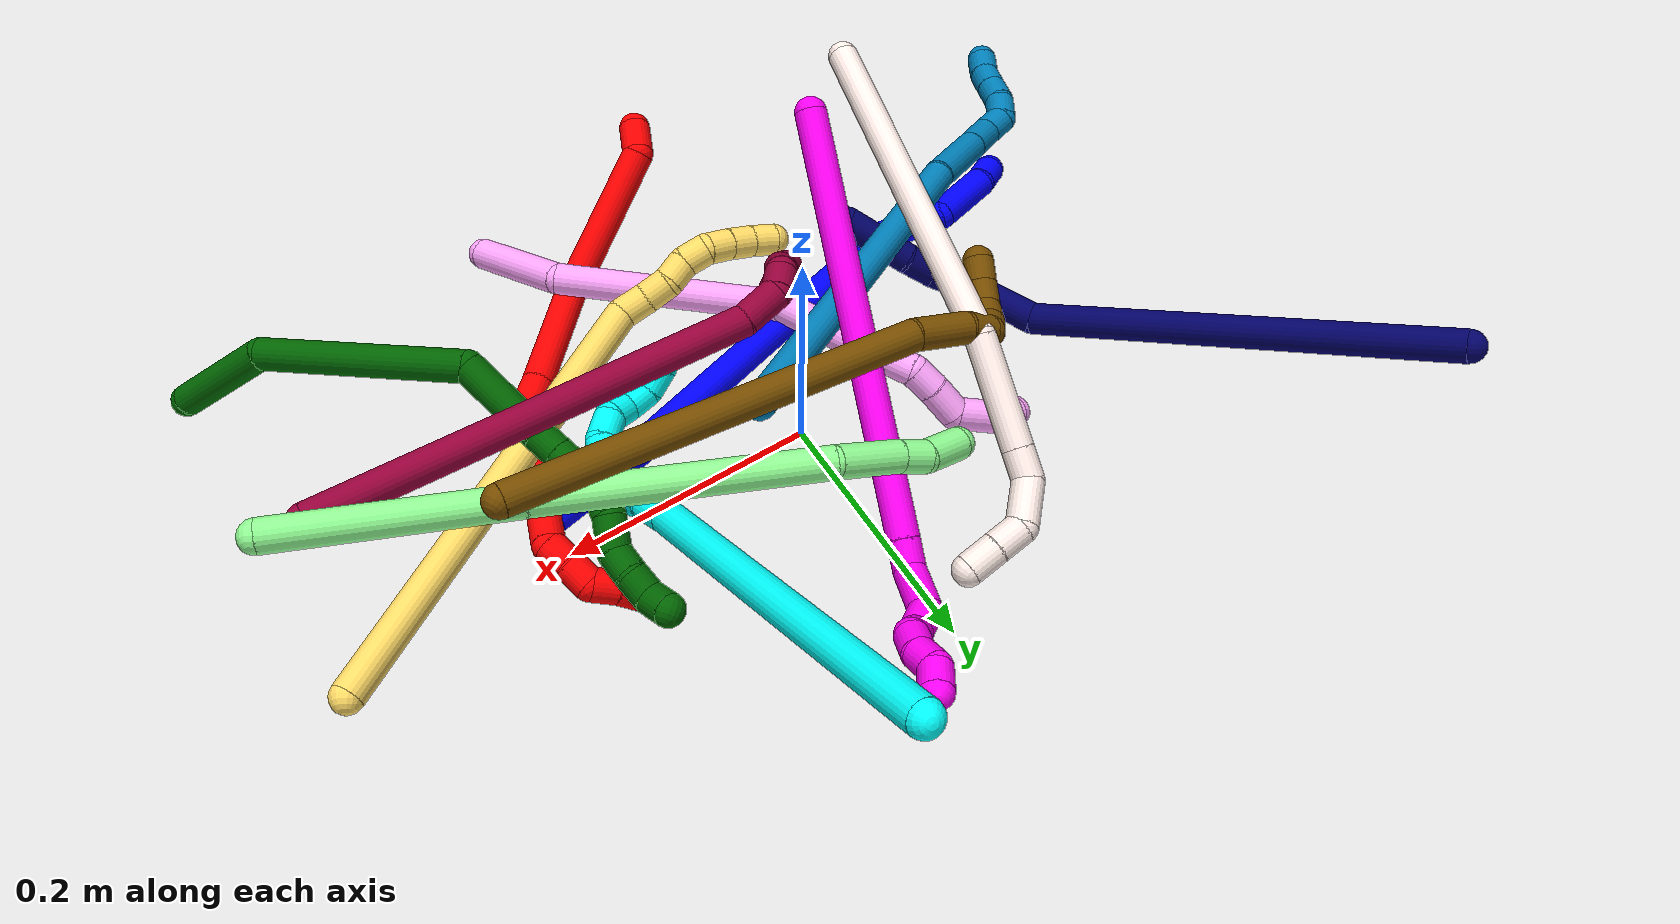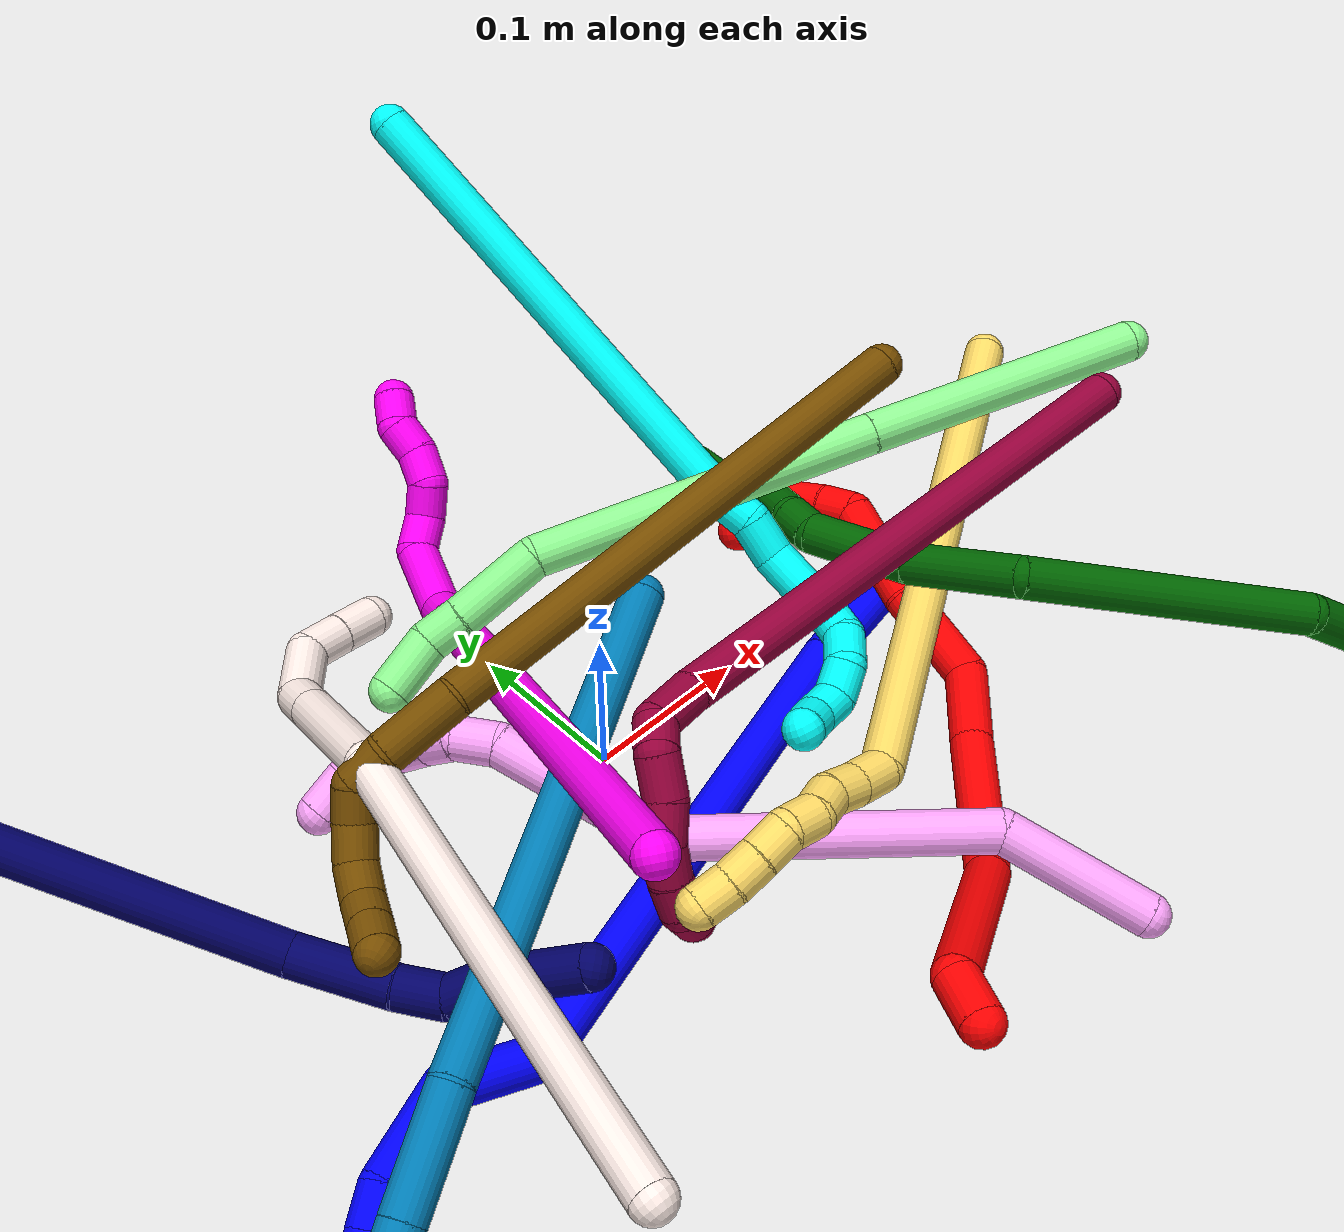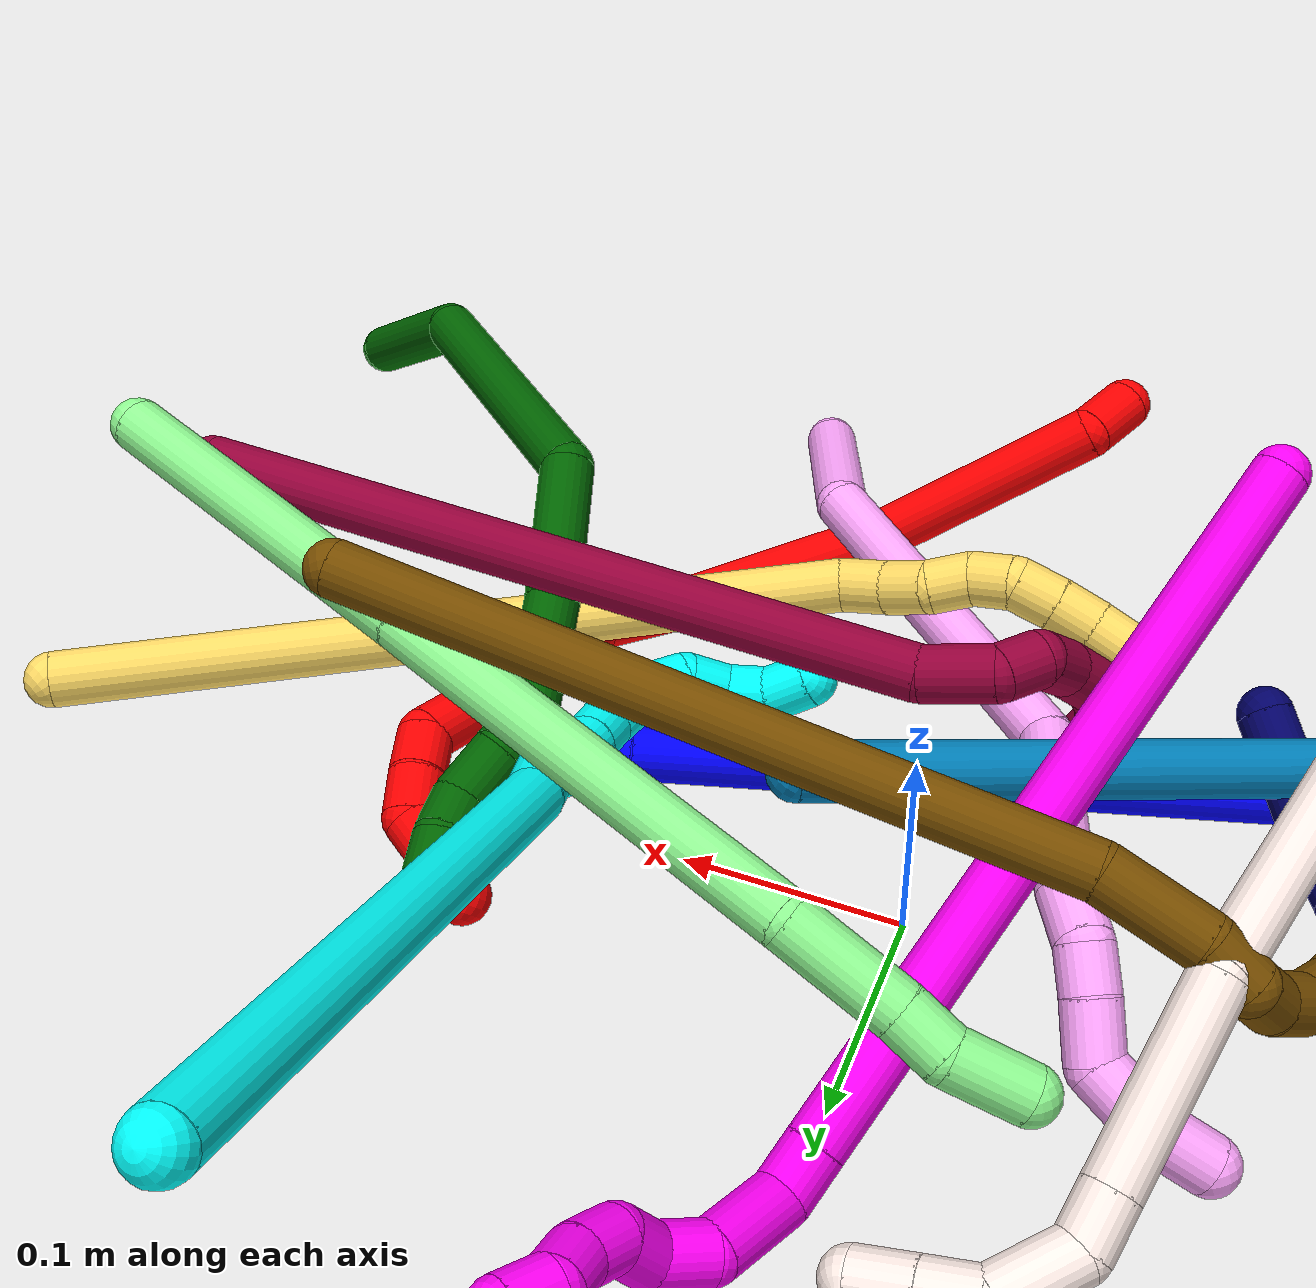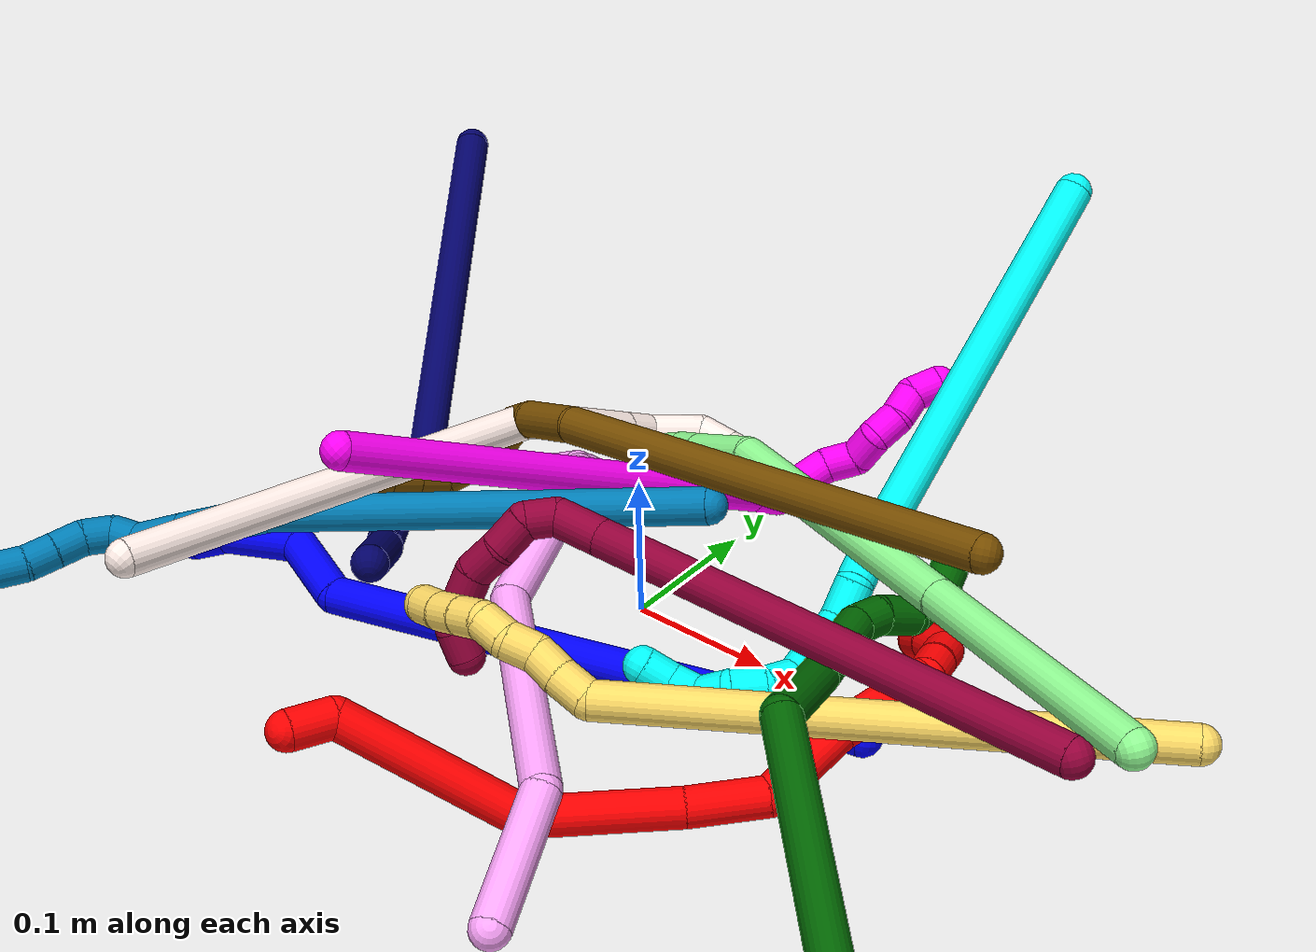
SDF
<sdf version="1.7">
 <world name="default">
  <plugin name="TubeGeneratorPlugin" filename="libtube_generator_plugin.so"/>
  <model name="photoneo_s_sensor">
   <static>1</static>
   <pose>0 0 2 1.57079 1.57079 3.14159</pose>
   <link name="link">
    <inertial><mass>0.1</mass></inertial>
    <sensor name="sensor" type="depth">
     <update_rate>30</update_rate>
     <camera>
      <horizontal_fov>1.22</horizontal_fov>
      <image><width>1920</width><height>1200</height><format>B8G8R8</format></image>
      <clip><near>0.1</near><far>4</far></clip>
      <depth_camera><output>points</output></depth_camera>
     </camera>
     <plugin name="camera_plugin" filename="libgazebo_ros_depth_camera.so">
      <baseline>0.2</baseline>
      <alwaysOn>1</alwaysOn>
      <updateRate>0.0</updateRate>
      <cameraName>camera_ir</cameraName>
      <imageTopicName>/camera/color/image_raw</imageTopicName>
      <cameraInfoTopicName>/camera/color/camera_info</cameraInfoTopicName>
      <depthImageTopicName>/camera/depth/image_raw</depthImageTopicName>
      <depthImageCameraInfoTopicName>/camera/depth/camera_info</depthImageCameraInfoTopicName>
      <pointCloudTopicName>/camera/depth/points</pointCloudTopicName>
      <frameName>fr_optical</frameName>
      <pointCloudCutoff>0.1</pointCloudCutoff>
      <pointCloudCutoffMax>2.0</pointCloudCutoffMax>
      <distortionK1>0</distortionK1>
      <distortionK2>0</distortionK2>
      <distortionK3>0</distortionK3>
      <distortionT1>0</distortionT1>
      <distortionT2>0</distortionT2>
      <CxPrime>0</CxPrime>
      <Cx>0</Cx>
      <Cy>0</Cy>
      <focalLength>0</focalLength>
      <hackBaseline>0</hackBaseline>
     </plugin>
    </sensor>
   </link>
  </model>
  <gravity>0 0 -9.8</gravity>
  <magnetic_field>6e-06 2.3e-05 -4.2e-05</magnetic_field>
  <atmosphere type="adiabatic"/>
  <physics name="default_physics" default="0" type="ode">
   <max_step_size>0.003</max_step_size>
   <real_time_factor>1</real_time_factor>
   <real_time_update_rate>1000</real_time_update_rate>
   <max_contacts>10000</max_contacts>
   <ode>
    <solver>
     <type>quick</type>
     <iters>100</iters>
     <sor>1.3</sor>
     <use_dynamic_moi_rescaling>0</use_dynamic_moi_rescaling>
    </solver>
    <constraints>
     <contact_max_correcting_vel>0</contact_max_correcting_vel>
     <contact_surface_layer>0.001</contact_surface_layer>
     <cfm>0</cfm>
     <erp>0.2</erp>
    </constraints>
   </ode>
  </physics>
  <scene><ambient>0.4 0.4 0.4 1</ambient><background>0.7 0.7 0.7 1</background><shadows>0</shadows></scene>
  <audio><device>default</device></audio>
  <spherical_coordinates>
   <surface_model>EARTH_WGS84</surface_model>
   <latitude_deg>0</latitude_deg>
   <longitude_deg>0</longitude_deg>
   <elevation>0</elevation>
   <heading_deg>0</heading_deg>
  </spherical_coordinates>
  <model name="bin">
   <static>1</static>
   <link name="bottom">
    <collision name="collision-bottom">
     <pose>0 0 -0.01 0 -0 0</pose>
     <geometry><box><size>0.8 0.6 0.02</size></box></geometry>
     <surface>
      <friction><ode><mu>100</mu><mu2>100</mu2></ode></friction>
      <contact><collide_bitmask>65535</collide_bitmask></contact>
     </surface>
    </collision>
   </link>
   <link name="west_wall">
    <collision name="collision-west_wall">
     <pose>-0.41 0 0.1 0 -0 0</pose>
     <geometry><box><size>0.02 0.6 0.2</size></box></geometry>
     <surface>
      <friction><ode><mu>100</mu><mu2>100</mu2></ode></friction>
      <contact><collide_bitmask>65535</collide_bitmask></contact>
     </surface>
    </collision>
   </link>
   <link name="east_wall">
    <collision name="collision-east_wall">
     <pose>0.41 0 0.1 0 -0 0</pose>
     <geometry><box><size>0.02 0.6 0.2</size></box></geometry>
     <surface>
      <friction><ode><mu>100</mu><mu2>100</mu2></ode></friction>
      <contact><collide_bitmask>65535</collide_bitmask></contact>
     </surface>
    </collision>
   </link>
   <link name="south_wall">
    <collision name="collision-south_wall">
     <pose>0 -0.31 0.1 0 -0 0</pose>
     <geometry><box><size>0.8 0.02 0.2</size></box></geometry>
     <surface>
      <friction><ode><mu>100</mu><mu2>100</mu2></ode></friction>
      <contact><collide_bitmask>65535</collide_bitmask></contact>
     </surface>
    </collision>
   </link>
   <link name="north_wall">
    <collision name="collision-north_wall">
     <pose>0 0.31 0.1 0 -0 0</pose>
     <geometry><box><size>0.8 0.02 0.2</size></box></geometry>
     <surface>
      <friction><ode><mu>100</mu><mu2>100</mu2></ode></friction>
      <contact><collide_bitmask>65535</collide_bitmask></contact>
     </surface>
    </collision>
   </link>
  </model>
  <model name="1">
   <static>0</static>
   <link name="1">
    <collision name="collision-cylinder-e_1_1_4">
     <pose>-0.028838 -0.005024 -0.002422 2.01999 -1.37977 -1.84038</pose>
     <geometry><cylinder><radius>0.0125</radius><length>0.058745</length></cylinder></geometry>
     <surface>
      <friction><ode><mu>1.16</mu><mu2>1.16</mu2><slip1>0</slip1><slip2>0</slip2></ode></friction>
      <contact><ode><kp>1e+06</kp><kd>1</kd><max_vel>0</max_vel><min_depth>0.001</min_depth></ode></contact>
     </surface>
    </collision>
    <visual name="visual-cylinder-e_1_1_4">
     <pose>-0.028838 -0.005024 -0.002422 2.01999 -1.37977 -1.84038</pose>
     <geometry><cylinder><radius>0.0125</radius><length>0.058745</length></cylinder></geometry>
     <material><ambient>0 0 1 1</ambient></material>
    </visual>
    <collision name="collision-cylinder-e_2_4_5">
     <pose>-0.206886 -0.047289 -0.023859 2.04288 -1.29756 -1.78314</pose>
     <geometry><cylinder><radius>0.0125</radius><length>0.309917</length></cylinder></geometry>
     <surface>
      <friction><ode><mu>1.16</mu><mu2>1.16</mu2><slip1>0</slip1><slip2>0</slip2></ode></friction>
      <contact><ode><kp>1e+06</kp><kd>1</kd><max_vel>0</max_vel><min_depth>0.001</min_depth></ode></contact>
     </surface>
    </collision>
    <visual name="visual-cylinder-e_2_4_5">
     <pose>-0.206886 -0.047289 -0.023859 2.04288 -1.29756 -1.78314</pose>
     <geometry><cylinder><radius>0.0125</radius><length>0.309917</length></cylinder></geometry>
     <material><ambient>0 0 1 1</ambient></material>
    </visual>
    <collision name="collision-cylinder-e_3_5_6">
     <pose>-0.380728 -0.078286 -0.036719 -0.792684 -1.22877 0.574147</pose>
     <geometry><cylinder><radius>0.0125</radius><length>0.052293</length></cylinder></geometry>
     <surface>
      <friction><ode><mu>1.16</mu><mu2>1.16</mu2><slip1>0</slip1><slip2>0</slip2></ode></friction>
      <contact><ode><kp>1e+06</kp><kd>1</kd><max_vel>0</max_vel><min_depth>0.001</min_depth></ode></contact>
     </surface>
    </collision>
    <visual name="visual-cylinder-e_3_5_6">
     <pose>-0.380728 -0.078286 -0.036719 -0.792684 -1.22877 0.574147</pose>
     <geometry><cylinder><radius>0.0125</radius><length>0.052293</length></cylinder></geometry>
     <material><ambient>0 0 1 1</ambient></material>
    </visual>
    <collision name="collision-cylinder-e_4_6_7">
     <pose>-0.431732 -0.078714 -0.037089 2.34496 -1.23061 -2.06762</pose>
     <geometry><cylinder><radius>0.0125</radius><length>0.055951</length></cylinder></geometry>
     <surface>
      <friction><ode><mu>1.16</mu><mu2>1.16</mu2><slip1>0</slip1><slip2>0</slip2></ode></friction>
      <contact><ode><kp>1e+06</kp><kd>1</kd><max_vel>0</max_vel><min_depth>0.001</min_depth></ode></contact>
     </surface>
    </collision>
    <visual name="visual-cylinder-e_4_6_7">
     <pose>-0.431732 -0.078714 -0.037089 2.34496 -1.23061 -2.06762</pose>
     <geometry><cylinder><radius>0.0125</radius><length>0.055951</length></cylinder></geometry>
     <material><ambient>0 0 1 1</ambient></material>
    </visual>
    <collision name="collision-cylinder-e_5_7_2">
     <pose>-0.46726 -0.090133 -0.04881 2.40143 -0.915582 -1.80755</pose>
     <geometry><cylinder><radius>0.0125</radius><length>0.023094</length></cylinder></geometry>
     <surface>
      <friction><ode><mu>1.16</mu><mu2>1.16</mu2><slip1>0</slip1><slip2>0</slip2></ode></friction>
      <contact><ode><kp>1e+06</kp><kd>1</kd><max_vel>0</max_vel><min_depth>0.001</min_depth></ode></contact>
     </surface>
    </collision>
    <visual name="visual-cylinder-e_5_7_2">
     <pose>-0.46726 -0.090133 -0.04881 2.40143 -0.915582 -1.80755</pose>
     <geometry><cylinder><radius>0.0125</radius><length>0.023094</length></cylinder></geometry>
     <material><ambient>0 0 1 1</ambient></material>
    </visual>
    <collision name="collision-sphere-2">
     <pose>-0.476416 -0.094878 -0.054005 0 -0 0</pose>
     <geometry><sphere><radius>0.0125</radius></sphere></geometry>
     <surface>
      <friction><ode><mu>1.16</mu><mu2>1.16</mu2><slip1>0</slip1><slip2>0</slip2></ode></friction>
      <contact><ode><kp>1e+06</kp><kd>1</kd><max_vel>0</max_vel><min_depth>0.001</min_depth></ode></contact>
     </surface>
    </collision>
    <visual name="visual-sphere-2">
     <pose>-0.476416 -0.094878 -0.054005 0 -0 0</pose>
     <geometry><sphere><radius>0.0125</radius></sphere></geometry>
     <material><ambient>0 0 1 1</ambient></material>
    </visual>
    <collision name="collision-sphere-7">
     <pose>-0.458105 -0.085388 -0.043615 0 -0 0</pose>
     <geometry><sphere><radius>0.0125</radius></sphere></geometry>
     <surface>
      <friction><ode><mu>1.16</mu><mu2>1.16</mu2><slip1>0</slip1><slip2>0</slip2></ode></friction>
      <contact><ode><kp>1e+06</kp><kd>1</kd><max_vel>0</max_vel><min_depth>0.001</min_depth></ode></contact>
     </surface>
    </collision>
    <visual name="visual-sphere-7">
     <pose>-0.458105 -0.085388 -0.043615 0 -0 0</pose>
     <geometry><sphere><radius>0.0125</radius></sphere></geometry>
     <material><ambient>0 0 1 1</ambient></material>
    </visual>
    <collision name="collision-sphere-6">
     <pose>-0.40536 -0.072039 -0.030563 0 -0 0</pose>
     <geometry><sphere><radius>0.0125</radius></sphere></geometry>
     <surface>
      <friction><ode><mu>1.16</mu><mu2>1.16</mu2><slip1>0</slip1><slip2>0</slip2></ode></friction>
      <contact><ode><kp>1e+06</kp><kd>1</kd><max_vel>0</max_vel><min_depth>0.001</min_depth></ode></contact>
     </surface>
    </collision>
    <visual name="visual-sphere-6">
     <pose>-0.40536 -0.072039 -0.030563 0 -0 0</pose>
     <geometry><sphere><radius>0.0125</radius></sphere></geometry>
     <material><ambient>0 0 1 1</ambient></material>
    </visual>
    <collision name="collision-sphere-5">
     <pose>-0.356096 -0.084532 -0.042875 0 -0 0</pose>
     <geometry><sphere><radius>0.0125</radius></sphere></geometry>
     <surface>
      <friction><ode><mu>1.16</mu><mu2>1.16</mu2><slip1>0</slip1><slip2>0</slip2></ode></friction>
      <contact><ode><kp>1e+06</kp><kd>1</kd><max_vel>0</max_vel><min_depth>0.001</min_depth></ode></contact>
     </surface>
    </collision>
    <visual name="visual-sphere-5">
     <pose>-0.356096 -0.084532 -0.042875 0 -0 0</pose>
     <geometry><sphere><radius>0.0125</radius></sphere></geometry>
     <material><ambient>0 0 1 1</ambient></material>
    </visual>
    <collision name="collision-sphere-1">
     <geometry><sphere><radius>0.0125</radius></sphere></geometry>
     <surface>
      <friction><ode><mu>1.16</mu><mu2>1.16</mu2><slip1>0</slip1><slip2>0</slip2></ode></friction>
      <contact><ode><kp>1e+06</kp><kd>1</kd><max_vel>0</max_vel><min_depth>0.001</min_depth></ode></contact>
     </surface>
    </collision>
    <visual name="visual-sphere-1">
     <geometry><sphere><radius>0.0125</radius></sphere></geometry>
     <material><ambient>0 0 1 1</ambient></material>
    </visual>
    <collision name="collision-sphere-4">
     <pose>-0.057677 -0.010047 -0.004843 0 -0 0</pose>
     <geometry><sphere><radius>0.0125</radius></sphere></geometry>
     <surface>
      <friction><ode><mu>1.16</mu><mu2>1.16</mu2><slip1>0</slip1><slip2>0</slip2></ode></friction>
      <contact><ode><kp>1e+06</kp><kd>1</kd><max_vel>0</max_vel><min_depth>0.001</min_depth></ode></contact>
     </surface>
    </collision>
    <visual name="visual-sphere-4">
     <pose>-0.057677 -0.010047 -0.004843 0 -0 0</pose>
     <geometry><sphere><radius>0.0125</radius></sphere></geometry>
     <material><ambient>0 0 1 1</ambient></material>
    </visual>
    <inertial>
     <pose>-0.241336 -0.051061 -0.025318 0 -0 0</pose>
     <mass>0.5</mass>
     <inertia>
      <ixx>-0.000844</ixx>
      <ixy>0</ixy>
      <ixz>0</ixz>
      <iyy>0.001705</iyy>
      <iyz>0</iyz>
      <izz>0.003049</izz>
     </inertia>
    </inertial>
   </link>
   <pose>0.197249 -0.028696 0.011488 -0.254847 0.059435 0.009468</pose>
  </model>
  <model name="2">
   <static>0</static>
   <link name="2">
    <collision name="collision-cylinder-e_1_1_4">
     <pose>0.004115 0.007778 -0.011113 -2.53095 0.294532 -0.8798</pose>
     <geometry><cylinder><radius>0.0125</radius><length>0.02835</length></cylinder></geometry>
     <surface>
      <friction><ode><mu>1.16</mu><mu2>1.16</mu2><slip1>0</slip1><slip2>0</slip2></ode></friction>
      <contact><ode><kp>1e+06</kp><kd>1</kd><max_vel>0</max_vel><min_depth>0.001</min_depth></ode></contact>
     </surface>
    </collision>
    <visual name="visual-cylinder-e_1_1_4">
     <pose>0.004115 0.007778 -0.011113 -2.53095 0.294532 -0.8798</pose>
     <geometry><cylinder><radius>0.0125</radius><length>0.02835</length></cylinder></geometry>
     <material><ambient>1 0 0 1</ambient></material>
    </visual>
    <collision name="collision-cylinder-e_2_4_5">
     <pose>0.058407 0.018451 -0.057583 -3.05987 0.955396 -2.98398</pose>
     <geometry><cylinder><radius>0.0125</radius><length>0.122901</length></cylinder></geometry>
     <surface>
      <friction><ode><mu>1.16</mu><mu2>1.16</mu2><slip1>0</slip1><slip2>0</slip2></ode></friction>
      <contact><ode><kp>1e+06</kp><kd>1</kd><max_vel>0</max_vel><min_depth>0.001</min_depth></ode></contact>
     </surface>
    </collision>
    <visual name="visual-cylinder-e_2_4_5">
     <pose>0.058407 0.018451 -0.057583 -3.05987 0.955396 -2.98398</pose>
     <geometry><cylinder><radius>0.0125</radius><length>0.122901</length></cylinder></geometry>
     <material><ambient>1 0 0 1</ambient></material>
    </visual>
    <collision name="collision-cylinder-e_3_5_6">
     <pose>0.13639 0.046377 -0.120265 -2.40003 0.643735 -1.41796</pose>
     <geometry><cylinder><radius>0.0125</radius><length>0.092657</length></cylinder></geometry>
     <surface>
      <friction><ode><mu>1.16</mu><mu2>1.16</mu2><slip1>0</slip1><slip2>0</slip2></ode></friction>
      <contact><ode><kp>1e+06</kp><kd>1</kd><max_vel>0</max_vel><min_depth>0.001</min_depth></ode></contact>
     </surface>
    </collision>
    <visual name="visual-cylinder-e_3_5_6">
     <pose>0.13639 0.046377 -0.120265 -2.40003 0.643735 -1.41796</pose>
     <geometry><cylinder><radius>0.0125</radius><length>0.092657</length></cylinder></geometry>
     <material><ambient>1 0 0 1</ambient></material>
    </visual>
    <collision name="collision-cylinder-e_4_6_7">
     <pose>0.178701 0.08689 -0.160652 -2.27151 0.621421 -1.20925</pose>
     <geometry><cylinder><radius>0.0125</radius><length>0.049831</length></cylinder></geometry>
     <surface>
      <friction><ode><mu>1.16</mu><mu2>1.16</mu2><slip1>0</slip1><slip2>0</slip2></ode></friction>
      <contact><ode><kp>1e+06</kp><kd>1</kd><max_vel>0</max_vel><min_depth>0.001</min_depth></ode></contact>
     </surface>
    </collision>
    <visual name="visual-cylinder-e_4_6_7">
     <pose>0.178701 0.08689 -0.160652 -2.27151 0.621421 -1.20925</pose>
     <geometry><cylinder><radius>0.0125</radius><length>0.049831</length></cylinder></geometry>
     <material><ambient>1 0 0 1</ambient></material>
    </visual>
    <collision name="collision-cylinder-e_5_7_8">
     <pose>0.191855 0.124588 -0.1935 -2.2985 -0.045409 0.101194</pose>
     <geometry><cylinder><radius>0.0125</radius><length>0.059558</length></cylinder></geometry>
     <surface>
      <friction><ode><mu>1.16</mu><mu2>1.16</mu2><slip1>0</slip1><slip2>0</slip2></ode></friction>
      <contact><ode><kp>1e+06</kp><kd>1</kd><max_vel>0</max_vel><min_depth>0.001</min_depth></ode></contact>
     </surface>
    </collision>
    <visual name="visual-cylinder-e_5_7_8">
     <pose>0.191855 0.124588 -0.1935 -2.2985 -0.045409 0.101194</pose>
     <geometry><cylinder><radius>0.0125</radius><length>0.059558</length></cylinder></geometry>
     <material><ambient>1 0 0 1</ambient></material>
    </visual>
    <collision name="collision-cylinder-e_6_8_9">
     <pose>0.195022 0.171053 -0.235181 -2.30511 0.137453 -0.307302</pose>
     <geometry><cylinder><radius>0.0125</radius><length>0.065967</length></cylinder></geometry>
     <surface>
      <friction><ode><mu>1.16</mu><mu2>1.16</mu2><slip1>0</slip1><slip2>0</slip2></ode></friction>
      <contact><ode><kp>1e+06</kp><kd>1</kd><max_vel>0</max_vel><min_depth>0.001</min_depth></ode></contact>
     </surface>
    </collision>
    <visual name="visual-cylinder-e_6_8_9">
     <pose>0.195022 0.171053 -0.235181 -2.30511 0.137453 -0.307302</pose>
     <geometry><cylinder><radius>0.0125</radius><length>0.065967</length></cylinder></geometry>
     <material><ambient>1 0 0 1</ambient></material>
    </visual>
    <collision name="collision-cylinder-e_7_9_10">
     <pose>0.196266 0.198191 -0.266238 -2.83657 -0.328529 1.64623</pose>
     <geometry><cylinder><radius>0.0125</radius><length>0.020302</length></cylinder></geometry>
     <surface>
      <friction><ode><mu>1.16</mu><mu2>1.16</mu2><slip1>0</slip1><slip2>0</slip2></ode></friction>
      <contact><ode><kp>1e+06</kp><kd>1</kd><max_vel>0</max_vel><min_depth>0.001</min_depth></ode></contact>
     </surface>
    </collision>
    <visual name="visual-cylinder-e_7_9_10">
     <pose>0.196266 0.198191 -0.266238 -2.83657 -0.328529 1.64623</pose>
     <geometry><cylinder><radius>0.0125</radius><length>0.020302</length></cylinder></geometry>
     <material><ambient>1 0 0 1</ambient></material>
    </visual>
    <collision name="collision-cylinder-e_8_10_11">
     <pose>0.189831 0.202783 -0.284919 -2.96419 -0.315936 2.12319</pose>
     <geometry><cylinder><radius>0.0125</radius><length>0.020341</length></cylinder></geometry>
     <surface>
      <friction><ode><mu>1.16</mu><mu2>1.16</mu2><slip1>0</slip1><slip2>0</slip2></ode></friction>
      <contact><ode><kp>1e+06</kp><kd>1</kd><max_vel>0</max_vel><min_depth>0.001</min_depth></ode></contact>
     </surface>
    </collision>
    <visual name="visual-cylinder-e_8_10_11">
     <pose>0.189831 0.202783 -0.284919 -2.96419 -0.315936 2.12319</pose>
     <geometry><cylinder><radius>0.0125</radius><length>0.020341</length></cylinder></geometry>
     <material><ambient>1 0 0 1</ambient></material>
    </visual>
    <collision name="collision-cylinder-e_9_11_12">
     <pose>0.179145 0.201733 -0.300418 2.71004 -0.851742 -2.24139</pose>
     <geometry><cylinder><radius>0.0125</radius><length>0.020004</length></cylinder></geometry>
     <surface>
      <friction><ode><mu>1.16</mu><mu2>1.16</mu2><slip1>0</slip1><slip2>0</slip2></ode></friction>
      <contact><ode><kp>1e+06</kp><kd>1</kd><max_vel>0</max_vel><min_depth>0.001</min_depth></ode></contact>
     </surface>
    </collision>
    <visual name="visual-cylinder-e_9_11_12">
     <pose>0.179145 0.201733 -0.300418 2.71004 -0.851742 -2.24139</pose>
     <geometry><cylinder><radius>0.0125</radius><length>0.020004</length></cylinder></geometry>
     <material><ambient>1 0 0 1</ambient></material>
    </visual>
    <collision name="collision-cylinder-e_10_12_2">
     <pose>0.16541 0.195069 -0.313262 2.62372 -0.66642 -1.83516</pose>
     <geometry><cylinder><radius>0.0125</radius><length>0.020089</length></cylinder></geometry>
     <surface>
      <friction><ode><mu>1.16</mu><mu2>1.16</mu2><slip1>0</slip1><slip2>0</slip2></ode></friction>
      <contact><ode><kp>1e+06</kp><kd>1</kd><max_vel>0</max_vel><min_depth>0.001</min_depth></ode></contact>
     </surface>
    </collision>
    <visual name="visual-cylinder-e_10_12_2">
     <pose>0.16541 0.195069 -0.313262 2.62372 -0.66642 -1.83516</pose>
     <geometry><cylinder><radius>0.0125</radius><length>0.020089</length></cylinder></geometry>
     <material><ambient>1 0 0 1</ambient></material>
    </visual>
    <collision name="collision-sphere-2">
     <pose>0.159201 0.191161 -0.320122 0 -0 0</pose>
     <geometry><sphere><radius>0.0125</radius></sphere></geometry>
     <surface>
      <friction><ode><mu>1.16</mu><mu2>1.16</mu2><slip1>0</slip1><slip2>0</slip2></ode></friction>
      <contact><ode><kp>1e+06</kp><kd>1</kd><max_vel>0</max_vel><min_depth>0.001</min_depth></ode></contact>
     </surface>
    </collision>
    <visual name="visual-sphere-2">
     <pose>0.159201 0.191161 -0.320122 0 -0 0</pose>
     <geometry><sphere><radius>0.0125</radius></sphere></geometry>
     <material><ambient>1 0 0 1</ambient></material>
    </visual>
    <collision name="collision-sphere-12">
     <pose>0.171619 0.198977 -0.306402 0 -0 0</pose>
     <geometry><sphere><radius>0.0125</radius></sphere></geometry>
     <surface>
      <friction><ode><mu>1.16</mu><mu2>1.16</mu2><slip1>0</slip1><slip2>0</slip2></ode></friction>
      <contact><ode><kp>1e+06</kp><kd>1</kd><max_vel>0</max_vel><min_depth>0.001</min_depth></ode></contact>
     </surface>
    </collision>
    <visual name="visual-sphere-12">
     <pose>0.171619 0.198977 -0.306402 0 -0 0</pose>
     <geometry><sphere><radius>0.0125</radius></sphere></geometry>
     <material><ambient>1 0 0 1</ambient></material>
    </visual>
    <collision name="collision-sphere-11">
     <pose>0.186671 0.204489 -0.294434 0 -0 0</pose>
     <geometry><sphere><radius>0.0125</radius></sphere></geometry>
     <surface>
      <friction><ode><mu>1.16</mu><mu2>1.16</mu2><slip1>0</slip1><slip2>0</slip2></ode></friction>
      <contact><ode><kp>1e+06</kp><kd>1</kd><max_vel>0</max_vel><min_depth>0.001</min_depth></ode></contact>
     </surface>
    </collision>
    <visual name="visual-sphere-11">
     <pose>0.186671 0.204489 -0.294434 0 -0 0</pose>
     <geometry><sphere><radius>0.0125</radius></sphere></geometry>
     <material><ambient>1 0 0 1</ambient></material>
    </visual>
    <collision name="collision-sphere-10">
     <pose>0.192991 0.201077 -0.275403 0 -0 0</pose>
     <geometry><sphere><radius>0.0125</radius></sphere></geometry>
     <surface>
      <friction><ode><mu>1.16</mu><mu2>1.16</mu2><slip1>0</slip1><slip2>0</slip2></ode></friction>
      <contact><ode><kp>1e+06</kp><kd>1</kd><max_vel>0</max_vel><min_depth>0.001</min_depth></ode></contact>
     </surface>
    </collision>
    <visual name="visual-sphere-10">
     <pose>0.192991 0.201077 -0.275403 0 -0 0</pose>
     <geometry><sphere><radius>0.0125</radius></sphere></geometry>
     <material><ambient>1 0 0 1</ambient></material>
    </visual>
    <collision name="collision-sphere-9">
     <pose>0.199542 0.195306 -0.257074 0 -0 0</pose>
     <geometry><sphere><radius>0.0125</radius></sphere></geometry>
     <surface>
      <friction><ode><mu>1.16</mu><mu2>1.16</mu2><slip1>0</slip1><slip2>0</slip2></ode></friction>
      <contact><ode><kp>1e+06</kp><kd>1</kd><max_vel>0</max_vel><min_depth>0.001</min_depth></ode></contact>
     </surface>
    </collision>
    <visual name="visual-sphere-9">
     <pose>0.199542 0.195306 -0.257074 0 -0 0</pose>
     <geometry><sphere><radius>0.0125</radius></sphere></geometry>
     <material><ambient>1 0 0 1</ambient></material>
    </visual>
    <collision name="collision-sphere-4">
     <pose>0.00823 0.015556 -0.022226 0 -0 0</pose>
     <geometry><sphere><radius>0.0125</radius></sphere></geometry>
     <surface>
      <friction><ode><mu>1.16</mu><mu2>1.16</mu2><slip1>0</slip1><slip2>0</slip2></ode></friction>
      <contact><ode><kp>1e+06</kp><kd>1</kd><max_vel>0</max_vel><min_depth>0.001</min_depth></ode></contact>
     </surface>
    </collision>
    <visual name="visual-sphere-4">
     <pose>0.00823 0.015556 -0.022226 0 -0 0</pose>
     <geometry><sphere><radius>0.0125</radius></sphere></geometry>
     <material><ambient>1 0 0 1</ambient></material>
    </visual>
    <collision name="collision-sphere-1">
     <geometry><sphere><radius>0.0125</radius></sphere></geometry>
     <surface>
      <friction><ode><mu>1.16</mu><mu2>1.16</mu2><slip1>0</slip1><slip2>0</slip2></ode></friction>
      <contact><ode><kp>1e+06</kp><kd>1</kd><max_vel>0</max_vel><min_depth>0.001</min_depth></ode></contact>
     </surface>
    </collision>
    <visual name="visual-sphere-1">
     <geometry><sphere><radius>0.0125</radius></sphere></geometry>
     <material><ambient>1 0 0 1</ambient></material>
    </visual>
    <collision name="collision-sphere-8">
     <pose>0.190503 0.146801 -0.213288 0 -0 0</pose>
     <geometry><sphere><radius>0.0125</radius></sphere></geometry>
     <surface>
      <friction><ode><mu>1.16</mu><mu2>1.16</mu2><slip1>0</slip1><slip2>0</slip2></ode></friction>
      <contact><ode><kp>1e+06</kp><kd>1</kd><max_vel>0</max_vel><min_depth>0.001</min_depth></ode></contact>
     </surface>
    </collision>
    <visual name="visual-sphere-8">
     <pose>0.190503 0.146801 -0.213288 0 -0 0</pose>
     <geometry><sphere><radius>0.0125</radius></sphere></geometry>
     <material><ambient>1 0 0 1</ambient></material>
    </visual>
    <collision name="collision-sphere-5">
     <pose>0.108584 0.021347 -0.092939 0 -0 0</pose>
     <geometry><sphere><radius>0.0125</radius></sphere></geometry>
     <surface>
      <friction><ode><mu>1.16</mu><mu2>1.16</mu2><slip1>0</slip1><slip2>0</slip2></ode></friction>
      <contact><ode><kp>1e+06</kp><kd>1</kd><max_vel>0</max_vel><min_depth>0.001</min_depth></ode></contact>
     </surface>
    </collision>
    <visual name="visual-sphere-5">
     <pose>0.108584 0.021347 -0.092939 0 -0 0</pose>
     <geometry><sphere><radius>0.0125</radius></sphere></geometry>
     <material><ambient>1 0 0 1</ambient></material>
    </visual>
    <collision name="collision-sphere-6">
     <pose>0.164195 0.071406 -0.147591 0 -0 0</pose>
     <geometry><sphere><radius>0.0125</radius></sphere></geometry>
     <surface>
      <friction><ode><mu>1.16</mu><mu2>1.16</mu2><slip1>0</slip1><slip2>0</slip2></ode></friction>
      <contact><ode><kp>1e+06</kp><kd>1</kd><max_vel>0</max_vel><min_depth>0.001</min_depth></ode></contact>
     </surface>
    </collision>
    <visual name="visual-sphere-6">
     <pose>0.164195 0.071406 -0.147591 0 -0 0</pose>
     <geometry><sphere><radius>0.0125</radius></sphere></geometry>
     <material><ambient>1 0 0 1</ambient></material>
    </visual>
    <collision name="collision-sphere-7">
     <pose>0.193206 0.102375 -0.173713 0 -0 0</pose>
     <geometry><sphere><radius>0.0125</radius></sphere></geometry>
     <surface>
      <friction><ode><mu>1.16</mu><mu2>1.16</mu2><slip1>0</slip1><slip2>0</slip2></ode></friction>
      <contact><ode><kp>1e+06</kp><kd>1</kd><max_vel>0</max_vel><min_depth>0.001</min_depth></ode></contact>
     </surface>
    </collision>
    <visual name="visual-sphere-7">
     <pose>0.193206 0.102375 -0.173713 0 -0 0</pose>
     <geometry><sphere><radius>0.0125</radius></sphere></geometry>
     <material><ambient>1 0 0 1</ambient></material>
    </visual>
    <inertial>
     <pose>0.135762 0.091844 -0.154166 0 -0 0</pose>
     <mass>0.5</mass>
     <inertia>
      <ixx>-0.000108</ixx>
      <ixy>0</ixy>
      <ixz>0</ixz>
      <iyy>8.2e-05</iyy>
      <iyz>0</iyz>
      <izz>-0.000294</izz>
     </inertia>
    </inertial>
   </link>
   <pose>-0.018665 -0.287213 0.075928 0.985399 0.264263 -0.119452</pose>
  </model>
  <model name="3">
   <static>0</static>
   <link name="3">
    <collision name="collision-cylinder-e_1_1_4">
     <pose>0.031342 -0.039373 -0.140825 2.86897 0.211148 1.31557</pose>
     <geometry><cylinder><radius>0.0125</radius><length>0.299094</length></cylinder></geometry>
     <surface>
      <friction><ode><mu>1.16</mu><mu2>1.16</mu2><slip1>0</slip1><slip2>0</slip2></ode></friction>
      <contact><ode><kp>1e+06</kp><kd>1</kd><max_vel>0</max_vel><min_depth>0.001</min_depth></ode></contact>
     </surface>
    </collision>
    <visual name="visual-cylinder-e_1_1_4">
     <pose>0.031342 -0.039373 -0.140825 2.86897 0.211148 1.31557</pose>
     <geometry><cylinder><radius>0.0125</radius><length>0.299094</length></cylinder></geometry>
     <material><ambient>0.003922 1 0.996078 1</ambient></material>
    </visual>
    <collision name="collision-cylinder-e_2_4_5">
     <pose>0.066972 -0.082646 -0.29184 2.77611 0.374441 1.59556</pose>
     <geometry><cylinder><radius>0.0125</radius><length>0.023444</length></cylinder></geometry>
     <surface>
      <friction><ode><mu>1.16</mu><mu2>1.16</mu2><slip1>0</slip1><slip2>0</slip2></ode></friction>
      <contact><ode><kp>1e+06</kp><kd>1</kd><max_vel>0</max_vel><min_depth>0.001</min_depth></ode></contact>
     </surface>
    </collision>
    <visual name="visual-cylinder-e_2_4_5">
     <pose>0.066972 -0.082646 -0.29184 2.77611 0.374441 1.59556</pose>
     <geometry><cylinder><radius>0.0125</radius><length>0.023444</length></cylinder></geometry>
     <material><ambient>0.003922 1 0.996078 1</ambient></material>
    </visual>
    <collision name="collision-cylinder-e_3_5_6">
     <pose>0.072907 -0.086809 -0.314679 3.12072 0.129448 2.82234</pose>
     <geometry><cylinder><radius>0.0125</radius><length>0.025519</length></cylinder></geometry>
     <surface>
      <friction><ode><mu>1.16</mu><mu2>1.16</mu2><slip1>0</slip1><slip2>0</slip2></ode></friction>
      <contact><ode><kp>1e+06</kp><kd>1</kd><max_vel>0</max_vel><min_depth>0.001</min_depth></ode></contact>
     </surface>
    </collision>
    <visual name="visual-cylinder-e_3_5_6">
     <pose>0.072907 -0.086809 -0.314679 3.12072 0.129448 2.82234</pose>
     <geometry><cylinder><radius>0.0125</radius><length>0.025519</length></cylinder></geometry>
     <material><ambient>0.003922 1 0.996078 1</ambient></material>
    </visual>
    <collision name="collision-cylinder-e_4_6_7">
     <pose>0.076964 -0.092614 -0.339115 2.70213 0.182992 0.779597</pose>
     <geometry><cylinder><radius>0.0125</radius><length>0.026489</length></cylinder></geometry>
     <surface>
      <friction><ode><mu>1.16</mu><mu2>1.16</mu2><slip1>0</slip1><slip2>0</slip2></ode></friction>
      <contact><ode><kp>1e+06</kp><kd>1</kd><max_vel>0</max_vel><min_depth>0.001</min_depth></ode></contact>
     </surface>
    </collision>
    <visual name="visual-cylinder-e_4_6_7">
     <pose>0.076964 -0.092614 -0.339115 2.70213 0.182992 0.779597</pose>
     <geometry><cylinder><radius>0.0125</radius><length>0.026489</length></cylinder></geometry>
     <material><ambient>0.003922 1 0.996078 1</ambient></material>
    </visual>
    <collision name="collision-cylinder-e_5_7_8">
     <pose>0.08133 -0.102539 -0.360239 2.7026 0.187367 0.79724</pose>
     <geometry><cylinder><radius>0.0125</radius><length>0.021</length></cylinder></geometry>
     <surface>
      <friction><ode><mu>1.16</mu><mu2>1.16</mu2><slip1>0</slip1><slip2>0</slip2></ode></friction>
      <contact><ode><kp>1e+06</kp><kd>1</kd><max_vel>0</max_vel><min_depth>0.001</min_depth></ode></contact>
     </surface>
    </collision>
    <visual name="visual-cylinder-e_5_7_8">
     <pose>0.08133 -0.102539 -0.360239 2.7026 0.187367 0.79724</pose>
     <geometry><cylinder><radius>0.0125</radius><length>0.021</length></cylinder></geometry>
     <material><ambient>0.003922 1 0.996078 1</ambient></material>
    </visual>
    <collision name="collision-cylinder-e_6_8_9">
     <pose>0.082173 -0.115529 -0.375821 2.19853 -0.104334 -0.204092</pose>
     <geometry><cylinder><radius>0.0125</radius><length>0.021379</length></cylinder></geometry>
     <surface>
      <friction><ode><mu>1.16</mu><mu2>1.16</mu2><slip1>0</slip1><slip2>0</slip2></ode></friction>
      <contact><ode><kp>1e+06</kp><kd>1</kd><max_vel>0</max_vel><min_depth>0.001</min_depth></ode></contact>
     </surface>
    </collision>
    <visual name="visual-cylinder-e_6_8_9">
     <pose>0.082173 -0.115529 -0.375821 2.19853 -0.104334 -0.204092</pose>
     <geometry><cylinder><radius>0.0125</radius><length>0.021379</length></cylinder></geometry>
     <material><ambient>0.003922 1 0.996078 1</ambient></material>
    </visual>
    <collision name="collision-cylinder-e_7_9_10">
     <pose>0.075359 -0.131398 -0.388075 2.26194 -0.543823 -1.06979</pose>
     <geometry><cylinder><radius>0.0125</radius><length>0.022036</length></cylinder></geometry>
     <surface>
      <friction><ode><mu>1.16</mu><mu2>1.16</mu2><slip1>0</slip1><slip2>0</slip2></ode></friction>
      <contact><ode><kp>1e+06</kp><kd>1</kd><max_vel>0</max_vel><min_depth>0.001</min_depth></ode></contact>
     </surface>
    </collision>
    <visual name="visual-cylinder-e_7_9_10">
     <pose>0.075359 -0.131398 -0.388075 2.26194 -0.543823 -1.06979</pose>
     <geometry><cylinder><radius>0.0125</radius><length>0.022036</length></cylinder></geometry>
     <material><ambient>0.003922 1 0.996078 1</ambient></material>
    </visual>
    <collision name="collision-cylinder-e_8_10_11">
     <pose>0.061802 -0.140509 -0.400567 2.86419 -0.861648 -2.55186</pose>
     <geometry><cylinder><radius>0.0125</radius><length>0.020703</length></cylinder></geometry>
     <surface>
      <friction><ode><mu>1.16</mu><mu2>1.16</mu2><slip1>0</slip1><slip2>0</slip2></ode></friction>
      <contact><ode><kp>1e+06</kp><kd>1</kd><max_vel>0</max_vel><min_depth>0.001</min_depth></ode></contact>
     </surface>
    </collision>
    <visual name="visual-cylinder-e_8_10_11">
     <pose>0.061802 -0.140509 -0.400567 2.86419 -0.861648 -2.55186</pose>
     <geometry><cylinder><radius>0.0125</radius><length>0.020703</length></cylinder></geometry>
     <material><ambient>0.003922 1 0.996078 1</ambient></material>
    </visual>
    <collision name="collision-cylinder-e_9_11_12">
     <pose>0.044919 -0.146901 -0.4077 1.71258 -1.10023 -1.23084</pose>
     <geometry><cylinder><radius>0.0125</radius><length>0.020256</length></cylinder></geometry>
     <surface>
      <friction><ode><mu>1.16</mu><mu2>1.16</mu2><slip1>0</slip1><slip2>0</slip2></ode></friction>
      <contact><ode><kp>1e+06</kp><kd>1</kd><max_vel>0</max_vel><min_depth>0.001</min_depth></ode></contact>
     </surface>
    </collision>
    <visual name="visual-cylinder-e_9_11_12">
     <pose>0.044919 -0.146901 -0.4077 1.71258 -1.10023 -1.23084</pose>
     <geometry><cylinder><radius>0.0125</radius><length>0.020256</length></cylinder></geometry>
     <material><ambient>0.003922 1 0.996078 1</ambient></material>
    </visual>
    <collision name="collision-cylinder-e_10_12_2">
     <pose>0.029352 -0.159052 -0.40792 1.5145 -0.709384 -0.673476</pose>
     <geometry><cylinder><radius>0.0125</radius><length>0.020079</length></cylinder></geometry>
     <surface>
      <friction><ode><mu>1.16</mu><mu2>1.16</mu2><slip1>0</slip1><slip2>0</slip2></ode></friction>
      <contact><ode><kp>1e+06</kp><kd>1</kd><max_vel>0</max_vel><min_depth>0.001</min_depth></ode></contact>
     </surface>
    </collision>
    <visual name="visual-cylinder-e_10_12_2">
     <pose>0.029352 -0.159052 -0.40792 1.5145 -0.709384 -0.673476</pose>
     <geometry><cylinder><radius>0.0125</radius><length>0.020079</length></cylinder></geometry>
     <material><ambient>0.003922 1 0.996078 1</ambient></material>
    </visual>
    <collision name="collision-sphere-2">
     <pose>0.022812 -0.166658 -0.407491 0 -0 0</pose>
     <geometry><sphere><radius>0.0125</radius></sphere></geometry>
     <surface>
      <friction><ode><mu>1.16</mu><mu2>1.16</mu2><slip1>0</slip1><slip2>0</slip2></ode></friction>
      <contact><ode><kp>1e+06</kp><kd>1</kd><max_vel>0</max_vel><min_depth>0.001</min_depth></ode></contact>
     </surface>
    </collision>
    <visual name="visual-sphere-2">
     <pose>0.022812 -0.166658 -0.407491 0 -0 0</pose>
     <geometry><sphere><radius>0.0125</radius></sphere></geometry>
     <material><ambient>0.003922 1 0.996078 1</ambient></material>
    </visual>
    <collision name="collision-sphere-12">
     <pose>0.035891 -0.151447 -0.408348 0 -0 0</pose>
     <geometry><sphere><radius>0.0125</radius></sphere></geometry>
     <surface>
      <friction><ode><mu>1.16</mu><mu2>1.16</mu2><slip1>0</slip1><slip2>0</slip2></ode></friction>
      <contact><ode><kp>1e+06</kp><kd>1</kd><max_vel>0</max_vel><min_depth>0.001</min_depth></ode></contact>
     </surface>
    </collision>
    <visual name="visual-sphere-12">
     <pose>0.035891 -0.151447 -0.408348 0 -0 0</pose>
     <geometry><sphere><radius>0.0125</radius></sphere></geometry>
     <material><ambient>0.003922 1 0.996078 1</ambient></material>
    </visual>
    <collision name="collision-sphere-11">
     <pose>0.053946 -0.142355 -0.407051 0 -0 0</pose>
     <geometry><sphere><radius>0.0125</radius></sphere></geometry>
     <surface>
      <friction><ode><mu>1.16</mu><mu2>1.16</mu2><slip1>0</slip1><slip2>0</slip2></ode></friction>
      <contact><ode><kp>1e+06</kp><kd>1</kd><max_vel>0</max_vel><min_depth>0.001</min_depth></ode></contact>
     </surface>
    </collision>
    <visual name="visual-sphere-11">
     <pose>0.053946 -0.142355 -0.407051 0 -0 0</pose>
     <geometry><sphere><radius>0.0125</radius></sphere></geometry>
     <material><ambient>0.003922 1 0.996078 1</ambient></material>
    </visual>
    <collision name="collision-sphere-10">
     <pose>0.069658 -0.138663 -0.394084 0 -0 0</pose>
     <geometry><sphere><radius>0.0125</radius></sphere></geometry>
     <surface>
      <friction><ode><mu>1.16</mu><mu2>1.16</mu2><slip1>0</slip1><slip2>0</slip2></ode></friction>
      <contact><ode><kp>1e+06</kp><kd>1</kd><max_vel>0</max_vel><min_depth>0.001</min_depth></ode></contact>
     </surface>
    </collision>
    <visual name="visual-sphere-10">
     <pose>0.069658 -0.138663 -0.394084 0 -0 0</pose>
     <geometry><sphere><radius>0.0125</radius></sphere></geometry>
     <material><ambient>0.003922 1 0.996078 1</ambient></material>
    </visual>
    <collision name="collision-sphere-9">
     <pose>0.081059 -0.124133 -0.382065 0 -0 0</pose>
     <geometry><sphere><radius>0.0125</radius></sphere></geometry>
     <surface>
      <friction><ode><mu>1.16</mu><mu2>1.16</mu2><slip1>0</slip1><slip2>0</slip2></ode></friction>
      <contact><ode><kp>1e+06</kp><kd>1</kd><max_vel>0</max_vel><min_depth>0.001</min_depth></ode></contact>
     </surface>
    </collision>
    <visual name="visual-sphere-9">
     <pose>0.081059 -0.124133 -0.382065 0 -0 0</pose>
     <geometry><sphere><radius>0.0125</radius></sphere></geometry>
     <material><ambient>0.003922 1 0.996078 1</ambient></material>
    </visual>
    <collision name="collision-sphere-4">
     <pose>0.062685 -0.078746 -0.28165 0 -0 0</pose>
     <geometry><sphere><radius>0.0125</radius></sphere></geometry>
     <surface>
      <friction><ode><mu>1.16</mu><mu2>1.16</mu2><slip1>0</slip1><slip2>0</slip2></ode></friction>
      <contact><ode><kp>1e+06</kp><kd>1</kd><max_vel>0</max_vel><min_depth>0.001</min_depth></ode></contact>
     </surface>
    </collision>
    <visual name="visual-sphere-4">
     <pose>0.062685 -0.078746 -0.28165 0 -0 0</pose>
     <geometry><sphere><radius>0.0125</radius></sphere></geometry>
     <material><ambient>0.003922 1 0.996078 1</ambient></material>
    </visual>
    <collision name="collision-sphere-1">
     <geometry><sphere><radius>0.0125</radius></sphere></geometry>
     <surface>
      <friction><ode><mu>1.16</mu><mu2>1.16</mu2><slip1>0</slip1><slip2>0</slip2></ode></friction>
      <contact><ode><kp>1e+06</kp><kd>1</kd><max_vel>0</max_vel><min_depth>0.001</min_depth></ode></contact>
     </surface>
    </collision>
    <visual name="visual-sphere-1">
     <geometry><sphere><radius>0.0125</radius></sphere></geometry>
     <material><ambient>0.003922 1 0.996078 1</ambient></material>
    </visual>
    <collision name="collision-sphere-8">
     <pose>0.083286 -0.106924 -0.369577 0 -0 0</pose>
     <geometry><sphere><radius>0.0125</radius></sphere></geometry>
     <surface>
      <friction><ode><mu>1.16</mu><mu2>1.16</mu2><slip1>0</slip1><slip2>0</slip2></ode></friction>
      <contact><ode><kp>1e+06</kp><kd>1</kd><max_vel>0</max_vel><min_depth>0.001</min_depth></ode></contact>
     </surface>
    </collision>
    <visual name="visual-sphere-8">
     <pose>0.083286 -0.106924 -0.369577 0 -0 0</pose>
     <geometry><sphere><radius>0.0125</radius></sphere></geometry>
     <material><ambient>0.003922 1 0.996078 1</ambient></material>
    </visual>
    <collision name="collision-sphere-5">
     <pose>0.07126 -0.086545 -0.302029 0 -0 0</pose>
     <geometry><sphere><radius>0.0125</radius></sphere></geometry>
     <surface>
      <friction><ode><mu>1.16</mu><mu2>1.16</mu2><slip1>0</slip1><slip2>0</slip2></ode></friction>
      <contact><ode><kp>1e+06</kp><kd>1</kd><max_vel>0</max_vel><min_depth>0.001</min_depth></ode></contact>
     </surface>
    </collision>
    <visual name="visual-sphere-5">
     <pose>0.07126 -0.086545 -0.302029 0 -0 0</pose>
     <geometry><sphere><radius>0.0125</radius></sphere></geometry>
     <material><ambient>0.003922 1 0.996078 1</ambient></material>
    </visual>
    <collision name="collision-sphere-6">
     <pose>0.074554 -0.087073 -0.327329 0 -0 0</pose>
     <geometry><sphere><radius>0.0125</radius></sphere></geometry>
     <surface>
      <friction><ode><mu>1.16</mu><mu2>1.16</mu2><slip1>0</slip1><slip2>0</slip2></ode></friction>
      <contact><ode><kp>1e+06</kp><kd>1</kd><max_vel>0</max_vel><min_depth>0.001</min_depth></ode></contact>
     </surface>
    </collision>
    <visual name="visual-sphere-6">
     <pose>0.074554 -0.087073 -0.327329 0 -0 0</pose>
     <geometry><sphere><radius>0.0125</radius></sphere></geometry>
     <material><ambient>0.003922 1 0.996078 1</ambient></material>
    </visual>
    <collision name="collision-sphere-7">
     <pose>0.079374 -0.098155 -0.350901 0 -0 0</pose>
     <geometry><sphere><radius>0.0125</radius></sphere></geometry>
     <surface>
      <friction><ode><mu>1.16</mu><mu2>1.16</mu2><slip1>0</slip1><slip2>0</slip2></ode></friction>
      <contact><ode><kp>1e+06</kp><kd>1</kd><max_vel>0</max_vel><min_depth>0.001</min_depth></ode></contact>
     </surface>
    </collision>
    <visual name="visual-sphere-7">
     <pose>0.079374 -0.098155 -0.350901 0 -0 0</pose>
     <geometry><sphere><radius>0.0125</radius></sphere></geometry>
     <material><ambient>0.003922 1 0.996078 1</ambient></material>
    </visual>
    <inertial>
     <pose>0.045495 -0.069959 -0.229737 0 -0 0</pose>
     <mass>0.5</mass>
     <inertia>
      <ixx>0.002681</ixx>
      <ixy>0</ixy>
      <ixz>0</ixz>
      <iyy>0.001689</iyy>
      <iyz>0</iyz>
      <izz>9.8e-05</izz>
     </inertia>
    </inertial>
   </link>
   <pose>0.122307 0.313865 0.220635 -0.751245 -0.130834 -0.238798</pose>
  </model>
  <model name="4">
   <static>0</static>
   <link name="4">
    <collision name="collision-cylinder-e_1_1_4">
     <pose>-0.019061 0.038512 -0.01114 -1.85237 -0.443818 0.583166</pose>
     <geometry><cylinder><radius>0.0125</radius><length>0.088783</length></cylinder></geometry>
     <surface>
      <friction><ode><mu>1.16</mu><mu2>1.16</mu2><slip1>0</slip1><slip2>0</slip2></ode></friction>
      <contact><ode><kp>1e+06</kp><kd>1</kd><max_vel>0</max_vel><min_depth>0.001</min_depth></ode></contact>
     </surface>
    </collision>
    <visual name="visual-cylinder-e_1_1_4">
     <pose>-0.019061 0.038512 -0.01114 -1.85237 -0.443818 0.583166</pose>
     <geometry><cylinder><radius>0.0125</radius><length>0.088783</length></cylinder></geometry>
     <material><ambient>1 0.65098 0.996078 1</ambient></material>
    </visual>
    <collision name="collision-cylinder-e_2_4_5">
     <pose>-0.097129 0.122 -0.073663 -2.42259 -0.712619 1.56107</pose>
     <geometry><cylinder><radius>0.0125</radius><length>0.180497</length></cylinder></geometry>
     <surface>
      <friction><ode><mu>1.16</mu><mu2>1.16</mu2><slip1>0</slip1><slip2>0</slip2></ode></friction>
      <contact><ode><kp>1e+06</kp><kd>1</kd><max_vel>0</max_vel><min_depth>0.001</min_depth></ode></contact>
     </surface>
    </collision>
    <visual name="visual-cylinder-e_2_4_5">
     <pose>-0.097129 0.122 -0.073663 -2.42259 -0.712619 1.56107</pose>
     <geometry><cylinder><radius>0.0125</radius><length>0.180497</length></cylinder></geometry>
     <material><ambient>1 0.65098 0.996078 1</ambient></material>
    </visual>
    <collision name="collision-cylinder-e_3_5_6">
     <pose>-0.173007 0.212215 -0.142862 -1.94596 -0.334021 0.485383</pose>
     <geometry><cylinder><radius>0.0125</radius><length>0.10293</length></cylinder></geometry>
     <surface>
      <friction><ode><mu>1.16</mu><mu2>1.16</mu2><slip1>0</slip1><slip2>0</slip2></ode></friction>
      <contact><ode><kp>1e+06</kp><kd>1</kd><max_vel>0</max_vel><min_depth>0.001</min_depth></ode></contact>
     </surface>
    </collision>
    <visual name="visual-cylinder-e_3_5_6">
     <pose>-0.173007 0.212215 -0.142862 -1.94596 -0.334021 0.485383</pose>
     <geometry><cylinder><radius>0.0125</radius><length>0.10293</length></cylinder></geometry>
     <material><ambient>1 0.65098 0.996078 1</ambient></material>
    </visual>
    <collision name="collision-cylinder-e_4_6_7">
     <pose>-0.194781 0.265745 -0.168516 -2.32812 -0.40571 0.89096</pose>
     <geometry><cylinder><radius>0.0125</radius><length>0.024835</length></cylinder></geometry>
     <surface>
      <friction><ode><mu>1.16</mu><mu2>1.16</mu2><slip1>0</slip1><slip2>0</slip2></ode></friction>
      <contact><ode><kp>1e+06</kp><kd>1</kd><max_vel>0</max_vel><min_depth>0.001</min_depth></ode></contact>
     </surface>
    </collision>
    <visual name="visual-cylinder-e_4_6_7">
     <pose>-0.194781 0.265745 -0.168516 -2.32812 -0.40571 0.89096</pose>
     <geometry><cylinder><radius>0.0125</radius><length>0.024835</length></cylinder></geometry>
     <material><ambient>1 0.65098 0.996078 1</ambient></material>
    </visual>
    <collision name="collision-cylinder-e_5_7_8">
     <pose>-0.200393 0.278351 -0.185566 -2.7035 -0.06987 0.311444</pose>
     <geometry><cylinder><radius>0.0125</radius><length>0.020396</length></cylinder></geometry>
     <surface>
      <friction><ode><mu>1.16</mu><mu2>1.16</mu2><slip1>0</slip1><slip2>0</slip2></ode></friction>
      <contact><ode><kp>1e+06</kp><kd>1</kd><max_vel>0</max_vel><min_depth>0.001</min_depth></ode></contact>
     </surface>
    </collision>
    <visual name="visual-cylinder-e_5_7_8">
     <pose>-0.200393 0.278351 -0.185566 -2.7035 -0.06987 0.311444</pose>
     <geometry><cylinder><radius>0.0125</radius><length>0.020396</length></cylinder></geometry>
     <material><ambient>1 0.65098 0.996078 1</ambient></material>
    </visual>
    <collision name="collision-cylinder-e_6_8_9">
     <pose>-0.200862 0.287317 -0.206812 -2.7728 0.018843 -0.100945</pose>
     <geometry><cylinder><radius>0.0125</radius><length>0.025805</length></cylinder></geometry>
     <surface>
      <friction><ode><mu>1.16</mu><mu2>1.16</mu2><slip1>0</slip1><slip2>0</slip2></ode></friction>
      <contact><ode><kp>1e+06</kp><kd>1</kd><max_vel>0</max_vel><min_depth>0.001</min_depth></ode></contact>
     </surface>
    </collision>
    <visual name="visual-cylinder-e_6_8_9">
     <pose>-0.200862 0.287317 -0.206812 -2.7728 0.018843 -0.100945</pose>
     <geometry><cylinder><radius>0.0125</radius><length>0.025805</length></cylinder></geometry>
     <material><ambient>1 0.65098 0.996078 1</ambient></material>
    </visual>
    <collision name="collision-cylinder-e_7_9_10">
     <pose>-0.210386 0.293411 -0.231656 -3.02943 -0.648347 2.81052</pose>
     <geometry><cylinder><radius>0.0125</radius><length>0.032348</length></cylinder></geometry>
     <surface>
      <friction><ode><mu>1.16</mu><mu2>1.16</mu2><slip1>0</slip1><slip2>0</slip2></ode></friction>
      <contact><ode><kp>1e+06</kp><kd>1</kd><max_vel>0</max_vel><min_depth>0.001</min_depth></ode></contact>
     </surface>
    </collision>
    <visual name="visual-cylinder-e_7_9_10">
     <pose>-0.210386 0.293411 -0.231656 -3.02943 -0.648347 2.81052</pose>
     <geometry><cylinder><radius>0.0125</radius><length>0.032348</length></cylinder></geometry>
     <material><ambient>1 0.65098 0.996078 1</ambient></material>
    </visual>
    <collision name="collision-cylinder-e_8_10_2">
     <pose>-0.227407 0.290795 -0.253401 2.71518 -0.636577 -1.97894</pose>
     <geometry><cylinder><radius>0.0125</radius><length>0.024405</length></cylinder></geometry>
     <surface>
      <friction><ode><mu>1.16</mu><mu2>1.16</mu2><slip1>0</slip1><slip2>0</slip2></ode></friction>
      <contact><ode><kp>1e+06</kp><kd>1</kd><max_vel>0</max_vel><min_depth>0.001</min_depth></ode></contact>
     </surface>
    </collision>
    <visual name="visual-cylinder-e_8_10_2">
     <pose>-0.227407 0.290795 -0.253401 2.71518 -0.636577 -1.97894</pose>
     <geometry><cylinder><radius>0.0125</radius><length>0.024405</length></cylinder></geometry>
     <material><ambient>1 0.65098 0.996078 1</ambient></material>
    </visual>
    <collision name="collision-sphere-2">
     <pose>-0.234661 0.286737 -0.262335 0 -0 0</pose>
     <geometry><sphere><radius>0.0125</radius></sphere></geometry>
     <surface>
      <friction><ode><mu>1.16</mu><mu2>1.16</mu2><slip1>0</slip1><slip2>0</slip2></ode></friction>
      <contact><ode><kp>1e+06</kp><kd>1</kd><max_vel>0</max_vel><min_depth>0.001</min_depth></ode></contact>
     </surface>
    </collision>
    <visual name="visual-sphere-2">
     <pose>-0.234661 0.286737 -0.262335 0 -0 0</pose>
     <geometry><sphere><radius>0.0125</radius></sphere></geometry>
     <material><ambient>1 0.65098 0.996078 1</ambient></material>
    </visual>
    <collision name="collision-sphere-10">
     <pose>-0.220153 0.294854 -0.244467 0 -0 0</pose>
     <geometry><sphere><radius>0.0125</radius></sphere></geometry>
     <surface>
      <friction><ode><mu>1.16</mu><mu2>1.16</mu2><slip1>0</slip1><slip2>0</slip2></ode></friction>
      <contact><ode><kp>1e+06</kp><kd>1</kd><max_vel>0</max_vel><min_depth>0.001</min_depth></ode></contact>
     </surface>
    </collision>
    <visual name="visual-sphere-10">
     <pose>-0.220153 0.294854 -0.244467 0 -0 0</pose>
     <geometry><sphere><radius>0.0125</radius></sphere></geometry>
     <material><ambient>1 0.65098 0.996078 1</ambient></material>
    </visual>
    <collision name="collision-sphere-9">
     <pose>-0.200619 0.291968 -0.218845 0 -0 0</pose>
     <geometry><sphere><radius>0.0125</radius></sphere></geometry>
     <surface>
      <friction><ode><mu>1.16</mu><mu2>1.16</mu2><slip1>0</slip1><slip2>0</slip2></ode></friction>
      <contact><ode><kp>1e+06</kp><kd>1</kd><max_vel>0</max_vel><min_depth>0.001</min_depth></ode></contact>
     </surface>
    </collision>
    <visual name="visual-sphere-9">
     <pose>-0.200619 0.291968 -0.218845 0 -0 0</pose>
     <geometry><sphere><radius>0.0125</radius></sphere></geometry>
     <material><ambient>1 0.65098 0.996078 1</ambient></material>
    </visual>
    <collision name="collision-sphere-4">
     <pose>-0.038123 0.077024 -0.02228 0 -0 0</pose>
     <geometry><sphere><radius>0.0125</radius></sphere></geometry>
     <surface>
      <friction><ode><mu>1.16</mu><mu2>1.16</mu2><slip1>0</slip1><slip2>0</slip2></ode></friction>
      <contact><ode><kp>1e+06</kp><kd>1</kd><max_vel>0</max_vel><min_depth>0.001</min_depth></ode></contact>
     </surface>
    </collision>
    <visual name="visual-sphere-4">
     <pose>-0.038123 0.077024 -0.02228 0 -0 0</pose>
     <geometry><sphere><radius>0.0125</radius></sphere></geometry>
     <material><ambient>1 0.65098 0.996078 1</ambient></material>
    </visual>
    <collision name="collision-sphere-1">
     <geometry><sphere><radius>0.0125</radius></sphere></geometry>
     <surface>
      <friction><ode><mu>1.16</mu><mu2>1.16</mu2><slip1>0</slip1><slip2>0</slip2></ode></friction>
      <contact><ode><kp>1e+06</kp><kd>1</kd><max_vel>0</max_vel><min_depth>0.001</min_depth></ode></contact>
     </surface>
    </collision>
    <visual name="visual-sphere-1">
     <geometry><sphere><radius>0.0125</radius></sphere></geometry>
     <material><ambient>1 0.65098 0.996078 1</ambient></material>
    </visual>
    <collision name="collision-sphere-8">
     <pose>-0.201105 0.282667 -0.194779 0 -0 0</pose>
     <geometry><sphere><radius>0.0125</radius></sphere></geometry>
     <surface>
      <friction><ode><mu>1.16</mu><mu2>1.16</mu2><slip1>0</slip1><slip2>0</slip2></ode></friction>
      <contact><ode><kp>1e+06</kp><kd>1</kd><max_vel>0</max_vel><min_depth>0.001</min_depth></ode></contact>
     </surface>
    </collision>
    <visual name="visual-sphere-8">
     <pose>-0.201105 0.282667 -0.194779 0 -0 0</pose>
     <geometry><sphere><radius>0.0125</radius></sphere></geometry>
     <material><ambient>1 0.65098 0.996078 1</ambient></material>
    </visual>
    <collision name="collision-sphere-5">
     <pose>-0.156135 0.166976 -0.125047 0 -0 0</pose>
     <geometry><sphere><radius>0.0125</radius></sphere></geometry>
     <surface>
      <friction><ode><mu>1.16</mu><mu2>1.16</mu2><slip1>0</slip1><slip2>0</slip2></ode></friction>
      <contact><ode><kp>1e+06</kp><kd>1</kd><max_vel>0</max_vel><min_depth>0.001</min_depth></ode></contact>
     </surface>
    </collision>
    <visual name="visual-sphere-5">
     <pose>-0.156135 0.166976 -0.125047 0 -0 0</pose>
     <geometry><sphere><radius>0.0125</radius></sphere></geometry>
     <material><ambient>1 0.65098 0.996078 1</ambient></material>
    </visual>
    <collision name="collision-sphere-6">
     <pose>-0.18988 0.257454 -0.160678 0 -0 0</pose>
     <geometry><sphere><radius>0.0125</radius></sphere></geometry>
     <surface>
      <friction><ode><mu>1.16</mu><mu2>1.16</mu2><slip1>0</slip1><slip2>0</slip2></ode></friction>
      <contact><ode><kp>1e+06</kp><kd>1</kd><max_vel>0</max_vel><min_depth>0.001</min_depth></ode></contact>
     </surface>
    </collision>
    <visual name="visual-sphere-6">
     <pose>-0.18988 0.257454 -0.160678 0 -0 0</pose>
     <geometry><sphere><radius>0.0125</radius></sphere></geometry>
     <material><ambient>1 0.65098 0.996078 1</ambient></material>
    </visual>
    <collision name="collision-sphere-7">
     <pose>-0.199681 0.274036 -0.176354 0 -0 0</pose>
     <geometry><sphere><radius>0.0125</radius></sphere></geometry>
     <surface>
      <friction><ode><mu>1.16</mu><mu2>1.16</mu2><slip1>0</slip1><slip2>0</slip2></ode></friction>
      <contact><ode><kp>1e+06</kp><kd>1</kd><max_vel>0</max_vel><min_depth>0.001</min_depth></ode></contact>
     </surface>
    </collision>
    <visual name="visual-sphere-7">
     <pose>-0.199681 0.274036 -0.176354 0 -0 0</pose>
     <geometry><sphere><radius>0.0125</radius></sphere></geometry>
     <material><ambient>1 0.65098 0.996078 1</ambient></material>
    </visual>
    <inertial>
     <pose>-0.12699 0.167125 -0.111949 0 -0 0</pose>
     <mass>0.5</mass>
     <inertia>
      <ixx>0.000563</ixx>
      <ixy>0</ixy>
      <ixz>0</ixz>
      <iyy>0.000666</iyy>
      <iyz>0</iyz>
      <izz>-2.1e-05</izz>
     </inertia>
    </inertial>
   </link>
   <pose>0.130208 -0.285234 0.011873 0.432468 0.464478 0.033016</pose>
  </model>
  <model name="5">
   <static>0</static>
   <link name="5">
    <collision name="collision-cylinder-e_1_1_4">
     <pose>-0.075916 -0.062741 0.14799 0.400985 -0.441233 -0.091089</pose>
     <geometry><cylinder><radius>0.0125</radius><length>0.355532</length></cylinder></geometry>
     <surface>
      <friction><ode><mu>1.16</mu><mu2>1.16</mu2><slip1>0</slip1><slip2>0</slip2></ode></friction>
      <contact><ode><kp>1e+06</kp><kd>1</kd><max_vel>0</max_vel><min_depth>0.001</min_depth></ode></contact>
     </surface>
    </collision>
    <visual name="visual-cylinder-e_1_1_4">
     <pose>-0.075916 -0.062741 0.14799 0.400985 -0.441233 -0.091089</pose>
     <geometry><cylinder><radius>0.0125</radius><length>0.355532</length></cylinder></geometry>
     <material><ambient>1 0.858824 0.4 1</ambient></material>
    </visual>
    <collision name="collision-cylinder-e_2_4_5">
     <pose>-0.162081 -0.127347 0.301387 0.33208 -1.06183 -0.19616</pose>
     <geometry><cylinder><radius>0.0125</radius><length>0.023475</length></cylinder></geometry>
     <surface>
      <friction><ode><mu>1.16</mu><mu2>1.16</mu2><slip1>0</slip1><slip2>0</slip2></ode></friction>
      <contact><ode><kp>1e+06</kp><kd>1</kd><max_vel>0</max_vel><min_depth>0.001</min_depth></ode></contact>
     </surface>
    </collision>
    <visual name="visual-cylinder-e_2_4_5">
     <pose>-0.162081 -0.127347 0.301387 0.33208 -1.06183 -0.19616</pose>
     <geometry><cylinder><radius>0.0125</radius><length>0.023475</length></cylinder></geometry>
     <material><ambient>1 0.858824 0.4 1</ambient></material>
    </visual>
    <collision name="collision-cylinder-e_3_5_6">
     <pose>-0.181593 -0.129681 0.311354 0.102504 -1.11117 -0.06367</pose>
     <geometry><cylinder><radius>0.0125</radius><length>0.020668</length></cylinder></geometry>
     <surface>
      <friction><ode><mu>1.16</mu><mu2>1.16</mu2><slip1>0</slip1><slip2>0</slip2></ode></friction>
      <contact><ode><kp>1e+06</kp><kd>1</kd><max_vel>0</max_vel><min_depth>0.001</min_depth></ode></contact>
     </surface>
    </collision>
    <visual name="visual-cylinder-e_3_5_6">
     <pose>-0.181593 -0.129681 0.311354 0.102504 -1.11117 -0.06367</pose>
     <geometry><cylinder><radius>0.0125</radius><length>0.020668</length></cylinder></geometry>
     <material><ambient>1 0.858824 0.4 1</ambient></material>
    </visual>
    <collision name="collision-cylinder-e_4_6_7">
     <pose>-0.197425 -0.131283 0.323372 0.150854 -0.716637 -0.056585</pose>
     <geometry><cylinder><radius>0.0125</radius><length>0.020007</length></cylinder></geometry>
     <surface>
      <friction><ode><mu>1.16</mu><mu2>1.16</mu2><slip1>0</slip1><slip2>0</slip2></ode></friction>
      <contact><ode><kp>1e+06</kp><kd>1</kd><max_vel>0</max_vel><min_depth>0.001</min_depth></ode></contact>
     </surface>
    </collision>
    <visual name="visual-cylinder-e_4_6_7">
     <pose>-0.197425 -0.131283 0.323372 0.150854 -0.716637 -0.056585</pose>
     <geometry><cylinder><radius>0.0125</radius><length>0.020007</length></cylinder></geometry>
     <material><ambient>1 0.858824 0.4 1</ambient></material>
    </visual>
    <collision name="collision-cylinder-e_5_7_8">
     <pose>-0.212958 -0.134367 0.335165 0.422698 -1.08302 -0.256683</pose>
     <geometry><cylinder><radius>0.0125</radius><length>0.02029</length></cylinder></geometry>
     <surface>
      <friction><ode><mu>1.16</mu><mu2>1.16</mu2><slip1>0</slip1><slip2>0</slip2></ode></friction>
      <contact><ode><kp>1e+06</kp><kd>1</kd><max_vel>0</max_vel><min_depth>0.001</min_depth></ode></contact>
     </surface>
    </collision>
    <visual name="visual-cylinder-e_5_7_8">
     <pose>-0.212958 -0.134367 0.335165 0.422698 -1.08302 -0.256683</pose>
     <geometry><cylinder><radius>0.0125</radius><length>0.02029</length></cylinder></geometry>
     <material><ambient>1 0.858824 0.4 1</ambient></material>
    </visual>
    <collision name="collision-cylinder-e_6_8_9">
     <pose>-0.228675 -0.142849 0.342963 1.08348 -0.740424 -0.458896</pose>
     <geometry><cylinder><radius>0.0125</radius><length>0.020027</length></cylinder></geometry>
     <surface>
      <friction><ode><mu>1.16</mu><mu2>1.16</mu2><slip1>0</slip1><slip2>0</slip2></ode></friction>
      <contact><ode><kp>1e+06</kp><kd>1</kd><max_vel>0</max_vel><min_depth>0.001</min_depth></ode></contact>
     </surface>
    </collision>
    <visual name="visual-cylinder-e_6_8_9">
     <pose>-0.228675 -0.142849 0.342963 1.08348 -0.740424 -0.458896</pose>
     <geometry><cylinder><radius>0.0125</radius><length>0.020027</length></cylinder></geometry>
     <material><ambient>1 0.858824 0.4 1</ambient></material>
    </visual>
    <collision name="collision-cylinder-e_7_9_10">
     <pose>-0.24223 -0.156147 0.349247 1.17555 -0.747785 -0.511425</pose>
     <geometry><cylinder><radius>0.0125</radius><length>0.02</length></cylinder></geometry>
     <surface>
      <friction><ode><mu>1.16</mu><mu2>1.16</mu2><slip1>0</slip1><slip2>0</slip2></ode></friction>
      <contact><ode><kp>1e+06</kp><kd>1</kd><max_vel>0</max_vel><min_depth>0.001</min_depth></ode></contact>
     </surface>
    </collision>
    <visual name="visual-cylinder-e_7_9_10">
     <pose>-0.24223 -0.156147 0.349247 1.17555 -0.747785 -0.511425</pose>
     <geometry><cylinder><radius>0.0125</radius><length>0.02</length></cylinder></geometry>
     <material><ambient>1 0.858824 0.4 1</ambient></material>
    </visual>
    <collision name="collision-cylinder-e_8_10_2">
     <pose>-0.256444 -0.169345 0.353987 1.28113 -0.835091 -0.638744</pose>
     <geometry><cylinder><radius>0.0125</radius><length>0.020001</length></cylinder></geometry>
     <surface>
      <friction><ode><mu>1.16</mu><mu2>1.16</mu2><slip1>0</slip1><slip2>0</slip2></ode></friction>
      <contact><ode><kp>1e+06</kp><kd>1</kd><max_vel>0</max_vel><min_depth>0.001</min_depth></ode></contact>
     </surface>
    </collision>
    <visual name="visual-cylinder-e_8_10_2">
     <pose>-0.256444 -0.169345 0.353987 1.28113 -0.835091 -0.638744</pose>
     <geometry><cylinder><radius>0.0125</radius><length>0.020001</length></cylinder></geometry>
     <material><ambient>1 0.858824 0.4 1</ambient></material>
    </visual>
    <collision name="collision-sphere-2">
     <pose>-0.263858 -0.175777 0.355904 0 -0 0</pose>
     <geometry><sphere><radius>0.0125</radius></sphere></geometry>
     <surface>
      <friction><ode><mu>1.16</mu><mu2>1.16</mu2><slip1>0</slip1><slip2>0</slip2></ode></friction>
      <contact><ode><kp>1e+06</kp><kd>1</kd><max_vel>0</max_vel><min_depth>0.001</min_depth></ode></contact>
     </surface>
    </collision>
    <visual name="visual-sphere-2">
     <pose>-0.263858 -0.175777 0.355904 0 -0 0</pose>
     <geometry><sphere><radius>0.0125</radius></sphere></geometry>
     <material><ambient>1 0.858824 0.4 1</ambient></material>
    </visual>
    <collision name="collision-sphere-10">
     <pose>-0.24903 -0.162914 0.35207 0 -0 0</pose>
     <geometry><sphere><radius>0.0125</radius></sphere></geometry>
     <surface>
      <friction><ode><mu>1.16</mu><mu2>1.16</mu2><slip1>0</slip1><slip2>0</slip2></ode></friction>
      <contact><ode><kp>1e+06</kp><kd>1</kd><max_vel>0</max_vel><min_depth>0.001</min_depth></ode></contact>
     </surface>
    </collision>
    <visual name="visual-sphere-10">
     <pose>-0.24903 -0.162914 0.35207 0 -0 0</pose>
     <geometry><sphere><radius>0.0125</radius></sphere></geometry>
     <material><ambient>1 0.858824 0.4 1</ambient></material>
    </visual>
    <collision name="collision-sphere-9">
     <pose>-0.23543 -0.14938 0.346424 0 -0 0</pose>
     <geometry><sphere><radius>0.0125</radius></sphere></geometry>
     <surface>
      <friction><ode><mu>1.16</mu><mu2>1.16</mu2><slip1>0</slip1><slip2>0</slip2></ode></friction>
      <contact><ode><kp>1e+06</kp><kd>1</kd><max_vel>0</max_vel><min_depth>0.001</min_depth></ode></contact>
     </surface>
    </collision>
    <visual name="visual-sphere-9">
     <pose>-0.23543 -0.14938 0.346424 0 -0 0</pose>
     <geometry><sphere><radius>0.0125</radius></sphere></geometry>
     <material><ambient>1 0.858824 0.4 1</ambient></material>
    </visual>
    <collision name="collision-sphere-4">
     <pose>-0.151832 -0.125482 0.295981 0 -0 0</pose>
     <geometry><sphere><radius>0.0125</radius></sphere></geometry>
     <surface>
      <friction><ode><mu>1.16</mu><mu2>1.16</mu2><slip1>0</slip1><slip2>0</slip2></ode></friction>
      <contact><ode><kp>1e+06</kp><kd>1</kd><max_vel>0</max_vel><min_depth>0.001</min_depth></ode></contact>
     </surface>
    </collision>
    <visual name="visual-sphere-4">
     <pose>-0.151832 -0.125482 0.295981 0 -0 0</pose>
     <geometry><sphere><radius>0.0125</radius></sphere></geometry>
     <material><ambient>1 0.858824 0.4 1</ambient></material>
    </visual>
    <collision name="collision-sphere-1">
     <geometry><sphere><radius>0.0125</radius></sphere></geometry>
     <surface>
      <friction><ode><mu>1.16</mu><mu2>1.16</mu2><slip1>0</slip1><slip2>0</slip2></ode></friction>
      <contact><ode><kp>1e+06</kp><kd>1</kd><max_vel>0</max_vel><min_depth>0.001</min_depth></ode></contact>
     </surface>
    </collision>
    <visual name="visual-sphere-1">
     <geometry><sphere><radius>0.0125</radius></sphere></geometry>
     <material><ambient>1 0.858824 0.4 1</ambient></material>
    </visual>
    <collision name="collision-sphere-8">
     <pose>-0.22192 -0.136318 0.339501 0 -0 0</pose>
     <geometry><sphere><radius>0.0125</radius></sphere></geometry>
     <surface>
      <friction><ode><mu>1.16</mu><mu2>1.16</mu2><slip1>0</slip1><slip2>0</slip2></ode></friction>
      <contact><ode><kp>1e+06</kp><kd>1</kd><max_vel>0</max_vel><min_depth>0.001</min_depth></ode></contact>
     </surface>
    </collision>
    <visual name="visual-sphere-8">
     <pose>-0.22192 -0.136318 0.339501 0 -0 0</pose>
     <geometry><sphere><radius>0.0125</radius></sphere></geometry>
     <material><ambient>1 0.858824 0.4 1</ambient></material>
    </visual>
    <collision name="collision-sphere-5">
     <pose>-0.172331 -0.129212 0.306794 0 -0 0</pose>
     <geometry><sphere><radius>0.0125</radius></sphere></geometry>
     <surface>
      <friction><ode><mu>1.16</mu><mu2>1.16</mu2><slip1>0</slip1><slip2>0</slip2></ode></friction>
      <contact><ode><kp>1e+06</kp><kd>1</kd><max_vel>0</max_vel><min_depth>0.001</min_depth></ode></contact>
     </surface>
    </collision>
    <visual name="visual-sphere-5">
     <pose>-0.172331 -0.129212 0.306794 0 -0 0</pose>
     <geometry><sphere><radius>0.0125</radius></sphere></geometry>
     <material><ambient>1 0.858824 0.4 1</ambient></material>
    </visual>
    <collision name="collision-sphere-6">
     <pose>-0.190854 -0.13015 0.315915 0 -0 0</pose>
     <geometry><sphere><radius>0.0125</radius></sphere></geometry>
     <surface>
      <friction><ode><mu>1.16</mu><mu2>1.16</mu2><slip1>0</slip1><slip2>0</slip2></ode></friction>
      <contact><ode><kp>1e+06</kp><kd>1</kd><max_vel>0</max_vel><min_depth>0.001</min_depth></ode></contact>
     </surface>
    </collision>
    <visual name="visual-sphere-6">
     <pose>-0.190854 -0.13015 0.315915 0 -0 0</pose>
     <geometry><sphere><radius>0.0125</radius></sphere></geometry>
     <material><ambient>1 0.858824 0.4 1</ambient></material>
    </visual>
    <collision name="collision-sphere-7">
     <pose>-0.203996 -0.132417 0.330829 0 -0 0</pose>
     <geometry><sphere><radius>0.0125</radius></sphere></geometry>
     <surface>
      <friction><ode><mu>1.16</mu><mu2>1.16</mu2><slip1>0</slip1><slip2>0</slip2></ode></friction>
      <contact><ode><kp>1e+06</kp><kd>1</kd><max_vel>0</max_vel><min_depth>0.001</min_depth></ode></contact>
     </surface>
    </collision>
    <visual name="visual-sphere-7">
     <pose>-0.203996 -0.132417 0.330829 0 -0 0</pose>
     <geometry><sphere><radius>0.0125</radius></sphere></geometry>
     <material><ambient>1 0.858824 0.4 1</ambient></material>
    </visual>
    <inertial>
     <pose>-0.114745 -0.0854 0.200658 0 -0 0</pose>
     <mass>0.5</mass>
     <inertia>
      <ixx>0.003059</ixx>
      <ixy>0</ixy>
      <ixz>0</ixz>
      <iyy>0.003188</iyy>
      <iyz>0</iyz>
      <izz>0.002972</izz>
     </inertia>
    </inertial>
   </link>
   <pose>0.380839 0.044287 0.051866 1.35492 0.366199 -0.550513</pose>
  </model>
  <model name="6">
   <static>0</static>
   <link name="6">
    <collision name="collision-cylinder-e_1_1_4">
     <pose>-0.029648 0.02331 -0.0219 -2.32501 -0.747516 1.47289</pose>
     <geometry><cylinder><radius>0.0125</radius><length>0.087223</length></cylinder></geometry>
     <surface>
      <friction><ode><mu>1.16</mu><mu2>1.16</mu2><slip1>0</slip1><slip2>0</slip2></ode></friction>
      <contact><ode><kp>1e+06</kp><kd>1</kd><max_vel>0</max_vel><min_depth>0.001</min_depth></ode></contact>
     </surface>
    </collision>
    <visual name="visual-cylinder-e_1_1_4">
     <pose>-0.029648 0.02331 -0.0219 -2.32501 -0.747516 1.47289</pose>
     <geometry><cylinder><radius>0.0125</radius><length>0.087223</length></cylinder></geometry>
     <material><ambient>0 0.392157 0.003922 1</ambient></material>
    </visual>
    <collision name="collision-cylinder-e_2_4_5">
     <pose>-0.097392 0.121327 -0.059219 -1.77434 -0.463176 0.563527</pose>
     <geometry><cylinder><radius>0.0125</radius><length>0.17053</length></cylinder></geometry>
     <surface>
      <friction><ode><mu>1.16</mu><mu2>1.16</mu2><slip1>0</slip1><slip2>0</slip2></ode></friction>
      <contact><ode><kp>1e+06</kp><kd>1</kd><max_vel>0</max_vel><min_depth>0.001</min_depth></ode></contact>
     </surface>
    </collision>
    <visual name="visual-cylinder-e_2_4_5">
     <pose>-0.097392 0.121327 -0.059219 -1.77434 -0.463176 0.563527</pose>
     <geometry><cylinder><radius>0.0125</radius><length>0.17053</length></cylinder></geometry>
     <material><ambient>0 0.392157 0.003922 1</ambient></material>
    </visual>
    <collision name="collision-cylinder-e_3_5_6">
     <pose>-0.139745 0.228141 -0.059609 -1.13298 -0.119514 0.076068</pose>
     <geometry><cylinder><radius>0.0125</radius><length>0.071412</length></cylinder></geometry>
     <surface>
      <friction><ode><mu>1.16</mu><mu2>1.16</mu2><slip1>0</slip1><slip2>0</slip2></ode></friction>
      <contact><ode><kp>1e+06</kp><kd>1</kd><max_vel>0</max_vel><min_depth>0.001</min_depth></ode></contact>
     </surface>
    </collision>
    <visual name="visual-cylinder-e_3_5_6">
     <pose>-0.139745 0.228141 -0.059609 -1.13298 -0.119514 0.076068</pose>
     <geometry><cylinder><radius>0.0125</radius><length>0.071412</length></cylinder></geometry>
     <material><ambient>0 0.392157 0.003922 1</ambient></material>
    </visual>
    <collision name="collision-cylinder-e_4_6_7">
     <pose>-0.147599 0.269627 -0.040154 -1.12991 -0.333873 0.212815</pose>
     <geometry><cylinder><radius>0.0125</radius><length>0.021953</length></cylinder></geometry>
     <surface>
      <friction><ode><mu>1.16</mu><mu2>1.16</mu2><slip1>0</slip1><slip2>0</slip2></ode></friction>
      <contact><ode><kp>1e+06</kp><kd>1</kd><max_vel>0</max_vel><min_depth>0.001</min_depth></ode></contact>
     </surface>
    </collision>
    <visual name="visual-cylinder-e_4_6_7">
     <pose>-0.147599 0.269627 -0.040154 -1.12991 -0.333873 0.212815</pose>
     <geometry><cylinder><radius>0.0125</radius><length>0.021953</length></cylinder></geometry>
     <material><ambient>0 0.392157 0.003922 1</ambient></material>
    </visual>
    <collision name="collision-cylinder-e_5_7_8">
     <pose>-0.157773 0.296727 -0.027278 -1.12583 -0.323257 0.205055</pose>
     <geometry><cylinder><radius>0.0125</radius><length>0.041412</length></cylinder></geometry>
     <surface>
      <friction><ode><mu>1.16</mu><mu2>1.16</mu2><slip1>0</slip1><slip2>0</slip2></ode></friction>
      <contact><ode><kp>1e+06</kp><kd>1</kd><max_vel>0</max_vel><min_depth>0.001</min_depth></ode></contact>
     </surface>
    </collision>
    <visual name="visual-cylinder-e_5_7_8">
     <pose>-0.157773 0.296727 -0.027278 -1.12583 -0.323257 0.205055</pose>
     <geometry><cylinder><radius>0.0125</radius><length>0.041412</length></cylinder></geometry>
     <material><ambient>0 0.392157 0.003922 1</ambient></material>
    </visual>
    <collision name="collision-cylinder-e_6_8_9">
     <pose>-0.167753 0.320523 -0.011045 -0.662774 -0.331863 0.115118</pose>
     <geometry><cylinder><radius>0.0125</radius><length>0.020884</length></cylinder></geometry>
     <surface>
      <friction><ode><mu>1.16</mu><mu2>1.16</mu2><slip1>0</slip1><slip2>0</slip2></ode></friction>
      <contact><ode><kp>1e+06</kp><kd>1</kd><max_vel>0</max_vel><min_depth>0.001</min_depth></ode></contact>
     </surface>
    </collision>
    <visual name="visual-cylinder-e_6_8_9">
     <pose>-0.167753 0.320523 -0.011045 -0.662774 -0.331863 0.115118</pose>
     <geometry><cylinder><radius>0.0125</radius><length>0.020884</length></cylinder></geometry>
     <material><ambient>0 0.392157 0.003922 1</ambient></material>
    </visual>
    <collision name="collision-cylinder-e_7_9_10">
     <pose>-0.171839 0.332825 0.008193 -0.497923 -0.052399 0.013325</pose>
     <geometry><cylinder><radius>0.0125</radius><length>0.026114</length></cylinder></geometry>
     <surface>
      <friction><ode><mu>1.16</mu><mu2>1.16</mu2><slip1>0</slip1><slip2>0</slip2></ode></friction>
      <contact><ode><kp>1e+06</kp><kd>1</kd><max_vel>0</max_vel><min_depth>0.001</min_depth></ode></contact>
     </surface>
    </collision>
    <visual name="visual-cylinder-e_7_9_10">
     <pose>-0.171839 0.332825 0.008193 -0.497923 -0.052399 0.013325</pose>
     <geometry><cylinder><radius>0.0125</radius><length>0.026114</length></cylinder></geometry>
     <material><ambient>0 0.392157 0.003922 1</ambient></material>
    </visual>
    <collision name="collision-cylinder-e_8_10_11">
     <pose>-0.176315 0.346512 0.02519 -0.931903 -0.387555 0.196735</pose>
     <geometry><cylinder><radius>0.0125</radius><length>0.020073</length></cylinder></geometry>
     <surface>
      <friction><ode><mu>1.16</mu><mu2>1.16</mu2><slip1>0</slip1><slip2>0</slip2></ode></friction>
      <contact><ode><kp>1e+06</kp><kd>1</kd><max_vel>0</max_vel><min_depth>0.001</min_depth></ode></contact>
     </surface>
    </collision>
    <visual name="visual-cylinder-e_8_10_11">
     <pose>-0.176315 0.346512 0.02519 -0.931903 -0.387555 0.196735</pose>
     <geometry><cylinder><radius>0.0125</radius><length>0.020073</length></cylinder></geometry>
     <material><ambient>0 0.392157 0.003922 1</ambient></material>
    </visual>
    <collision name="collision-cylinder-e_9_11_12">
     <pose>-0.181657 0.362511 0.035965 -1.02098 -0.153366 0.086001</pose>
     <geometry><cylinder><radius>0.0125</radius><length>0.02027</length></cylinder></geometry>
     <surface>
      <friction><ode><mu>1.16</mu><mu2>1.16</mu2><slip1>0</slip1><slip2>0</slip2></ode></friction>
      <contact><ode><kp>1e+06</kp><kd>1</kd><max_vel>0</max_vel><min_depth>0.001</min_depth></ode></contact>
     </surface>
    </collision>
    <visual name="visual-cylinder-e_9_11_12">
     <pose>-0.181657 0.362511 0.035965 -1.02098 -0.153366 0.086001</pose>
     <geometry><cylinder><radius>0.0125</radius><length>0.02027</length></cylinder></geometry>
     <material><ambient>0 0.392157 0.003922 1</ambient></material>
    </visual>
    <collision name="collision-cylinder-e_10_12_2">
     <pose>-0.19006 0.377936 0.043827 -1.20612 -0.749235 0.528842</pose>
     <geometry><cylinder><radius>0.0125</radius><length>0.02013</length></cylinder></geometry>
     <surface>
      <friction><ode><mu>1.16</mu><mu2>1.16</mu2><slip1>0</slip1><slip2>0</slip2></ode></friction>
      <contact><ode><kp>1e+06</kp><kd>1</kd><max_vel>0</max_vel><min_depth>0.001</min_depth></ode></contact>
     </surface>
    </collision>
    <visual name="visual-cylinder-e_10_12_2">
     <pose>-0.19006 0.377936 0.043827 -1.20612 -0.749235 0.528842</pose>
     <geometry><cylinder><radius>0.0125</radius><length>0.02013</length></cylinder></geometry>
     <material><ambient>0 0.392157 0.003922 1</ambient></material>
    </visual>
    <collision name="collision-sphere-2">
     <pose>-0.196915 0.384821 0.046455 0 -0 0</pose>
     <geometry><sphere><radius>0.0125</radius></sphere></geometry>
     <surface>
      <friction><ode><mu>1.16</mu><mu2>1.16</mu2><slip1>0</slip1><slip2>0</slip2></ode></friction>
      <contact><ode><kp>1e+06</kp><kd>1</kd><max_vel>0</max_vel><min_depth>0.001</min_depth></ode></contact>
     </surface>
    </collision>
    <visual name="visual-sphere-2">
     <pose>-0.196915 0.384821 0.046455 0 -0 0</pose>
     <geometry><sphere><radius>0.0125</radius></sphere></geometry>
     <material><ambient>0 0.392157 0.003922 1</ambient></material>
    </visual>
    <collision name="collision-sphere-12">
     <pose>-0.183205 0.371051 0.041199 0 -0 0</pose>
     <geometry><sphere><radius>0.0125</radius></sphere></geometry>
     <surface>
      <friction><ode><mu>1.16</mu><mu2>1.16</mu2><slip1>0</slip1><slip2>0</slip2></ode></friction>
      <contact><ode><kp>1e+06</kp><kd>1</kd><max_vel>0</max_vel><min_depth>0.001</min_depth></ode></contact>
     </surface>
    </collision>
    <visual name="visual-sphere-12">
     <pose>-0.183205 0.371051 0.041199 0 -0 0</pose>
     <geometry><sphere><radius>0.0125</radius></sphere></geometry>
     <material><ambient>0 0.392157 0.003922 1</ambient></material>
    </visual>
    <collision name="collision-sphere-11">
     <pose>-0.180109 0.353971 0.030731 0 -0 0</pose>
     <geometry><sphere><radius>0.0125</radius></sphere></geometry>
     <surface>
      <friction><ode><mu>1.16</mu><mu2>1.16</mu2><slip1>0</slip1><slip2>0</slip2></ode></friction>
      <contact><ode><kp>1e+06</kp><kd>1</kd><max_vel>0</max_vel><min_depth>0.001</min_depth></ode></contact>
     </surface>
    </collision>
    <visual name="visual-sphere-11">
     <pose>-0.180109 0.353971 0.030731 0 -0 0</pose>
     <geometry><sphere><radius>0.0125</radius></sphere></geometry>
     <material><ambient>0 0.392157 0.003922 1</ambient></material>
    </visual>
    <collision name="collision-sphere-10">
     <pose>-0.172522 0.339052 0.019649 0 -0 0</pose>
     <geometry><sphere><radius>0.0125</radius></sphere></geometry>
     <surface>
      <friction><ode><mu>1.16</mu><mu2>1.16</mu2><slip1>0</slip1><slip2>0</slip2></ode></friction>
      <contact><ode><kp>1e+06</kp><kd>1</kd><max_vel>0</max_vel><min_depth>0.001</min_depth></ode></contact>
     </surface>
    </collision>
    <visual name="visual-sphere-10">
     <pose>-0.172522 0.339052 0.019649 0 -0 0</pose>
     <geometry><sphere><radius>0.0125</radius></sphere></geometry>
     <material><ambient>0 0.392157 0.003922 1</ambient></material>
    </visual>
    <collision name="collision-sphere-9">
     <pose>-0.171155 0.326597 -0.003262 0 -0 0</pose>
     <geometry><sphere><radius>0.0125</radius></sphere></geometry>
     <surface>
      <friction><ode><mu>1.16</mu><mu2>1.16</mu2><slip1>0</slip1><slip2>0</slip2></ode></friction>
      <contact><ode><kp>1e+06</kp><kd>1</kd><max_vel>0</max_vel><min_depth>0.001</min_depth></ode></contact>
     </surface>
    </collision>
    <visual name="visual-sphere-9">
     <pose>-0.171155 0.326597 -0.003262 0 -0 0</pose>
     <geometry><sphere><radius>0.0125</radius></sphere></geometry>
     <material><ambient>0 0.392157 0.003922 1</ambient></material>
    </visual>
    <collision name="collision-sphere-4">
     <pose>-0.059296 0.04662 -0.043799 0 -0 0</pose>
     <geometry><sphere><radius>0.0125</radius></sphere></geometry>
     <surface>
      <friction><ode><mu>1.16</mu><mu2>1.16</mu2><slip1>0</slip1><slip2>0</slip2></ode></friction>
      <contact><ode><kp>1e+06</kp><kd>1</kd><max_vel>0</max_vel><min_depth>0.001</min_depth></ode></contact>
     </surface>
    </collision>
    <visual name="visual-sphere-4">
     <pose>-0.059296 0.04662 -0.043799 0 -0 0</pose>
     <geometry><sphere><radius>0.0125</radius></sphere></geometry>
     <material><ambient>0 0.392157 0.003922 1</ambient></material>
    </visual>
    <collision name="collision-sphere-1">
     <geometry><sphere><radius>0.0125</radius></sphere></geometry>
     <surface>
      <friction><ode><mu>1.16</mu><mu2>1.16</mu2><slip1>0</slip1><slip2>0</slip2></ode></friction>
      <contact><ode><kp>1e+06</kp><kd>1</kd><max_vel>0</max_vel><min_depth>0.001</min_depth></ode></contact>
     </surface>
    </collision>
    <visual name="visual-sphere-1">
     <geometry><sphere><radius>0.0125</radius></sphere></geometry>
     <material><ambient>0 0.392157 0.003922 1</ambient></material>
    </visual>
    <collision name="collision-sphere-8">
     <pose>-0.16435 0.314448 -0.018827 0 -0 0</pose>
     <geometry><sphere><radius>0.0125</radius></sphere></geometry>
     <surface>
      <friction><ode><mu>1.16</mu><mu2>1.16</mu2><slip1>0</slip1><slip2>0</slip2></ode></friction>
      <contact><ode><kp>1e+06</kp><kd>1</kd><max_vel>0</max_vel><min_depth>0.001</min_depth></ode></contact>
     </surface>
    </collision>
    <visual name="visual-sphere-8">
     <pose>-0.16435 0.314448 -0.018827 0 -0 0</pose>
     <geometry><sphere><radius>0.0125</radius></sphere></geometry>
     <material><ambient>0 0.392157 0.003922 1</ambient></material>
    </visual>
    <collision name="collision-sphere-5">
     <pose>-0.135487 0.196034 -0.074639 0 -0 0</pose>
     <geometry><sphere><radius>0.0125</radius></sphere></geometry>
     <surface>
      <friction><ode><mu>1.16</mu><mu2>1.16</mu2><slip1>0</slip1><slip2>0</slip2></ode></friction>
      <contact><ode><kp>1e+06</kp><kd>1</kd><max_vel>0</max_vel><min_depth>0.001</min_depth></ode></contact>
     </surface>
    </collision>
    <visual name="visual-sphere-5">
     <pose>-0.135487 0.196034 -0.074639 0 -0 0</pose>
     <geometry><sphere><radius>0.0125</radius></sphere></geometry>
     <material><ambient>0 0.392157 0.003922 1</ambient></material>
    </visual>
    <collision name="collision-sphere-6">
     <pose>-0.144002 0.260248 -0.044579 0 -0 0</pose>
     <geometry><sphere><radius>0.0125</radius></sphere></geometry>
     <surface>
      <friction><ode><mu>1.16</mu><mu2>1.16</mu2><slip1>0</slip1><slip2>0</slip2></ode></friction>
      <contact><ode><kp>1e+06</kp><kd>1</kd><max_vel>0</max_vel><min_depth>0.001</min_depth></ode></contact>
     </surface>
    </collision>
    <visual name="visual-sphere-6">
     <pose>-0.144002 0.260248 -0.044579 0 -0 0</pose>
     <geometry><sphere><radius>0.0125</radius></sphere></geometry>
     <material><ambient>0 0.392157 0.003922 1</ambient></material>
    </visual>
    <collision name="collision-sphere-7">
     <pose>-0.151196 0.279005 -0.035728 0 -0 0</pose>
     <geometry><sphere><radius>0.0125</radius></sphere></geometry>
     <surface>
      <friction><ode><mu>1.16</mu><mu2>1.16</mu2><slip1>0</slip1><slip2>0</slip2></ode></friction>
      <contact><ode><kp>1e+06</kp><kd>1</kd><max_vel>0</max_vel><min_depth>0.001</min_depth></ode></contact>
     </surface>
    </collision>
    <visual name="visual-sphere-7">
     <pose>-0.151196 0.279005 -0.035728 0 -0 0</pose>
     <geometry><sphere><radius>0.0125</radius></sphere></geometry>
     <material><ambient>0 0.392157 0.003922 1</ambient></material>
    </visual>
    <inertial>
     <pose>-0.115971 0.189037 -0.032353 0 -0 0</pose>
     <mass>0.5</mass>
     <inertia>
      <ixx>0.000604</ixx>
      <ixy>0</ixy>
      <ixz>0</ixz>
      <iyy>0.000355</iyy>
      <iyz>0</iyz>
      <izz>-0.000202</izz>
     </inertia>
    </inertial>
   </link>
   <pose>0.388379 -0.273746 0.011839 -2.3715 1.10052 -1.64546</pose>
  </model>
  <model name="7">
   <static>0</static>
   <link name="7">
    <collision name="collision-cylinder-e_1_1_4">
     <pose>-0.02844 0.000386 -0.160503 -3.13919 -0.175371 3.11425</pose>
     <geometry><cylinder><radius>0.0125</radius><length>0.326007</length></cylinder></geometry>
     <surface>
      <friction><ode><mu>1.16</mu><mu2>1.16</mu2><slip1>0</slip1><slip2>0</slip2></ode></friction>
      <contact><ode><kp>1e+06</kp><kd>1</kd><max_vel>0</max_vel><min_depth>0.001</min_depth></ode></contact>
     </surface>
    </collision>
    <visual name="visual-cylinder-e_1_1_4">
     <pose>-0.02844 0.000386 -0.160503 -3.13919 -0.175371 3.11425</pose>
     <geometry><cylinder><radius>0.0125</radius><length>0.326007</length></cylinder></geometry>
     <material><ambient>0.003922 0 0.403922 1</ambient></material>
    </visual>
    <collision name="collision-cylinder-e_2_4_5">
     <pose>-0.054409 -0.010188 -0.34971 2.77684 0.08025 0.428681</pose>
     <geometry><cylinder><radius>0.0125</radius><length>0.061648</length></cylinder></geometry>
     <surface>
      <friction><ode><mu>1.16</mu><mu2>1.16</mu2><slip1>0</slip1><slip2>0</slip2></ode></friction>
      <contact><ode><kp>1e+06</kp><kd>1</kd><max_vel>0</max_vel><min_depth>0.001</min_depth></ode></contact>
     </surface>
    </collision>
    <visual name="visual-cylinder-e_2_4_5">
     <pose>-0.054409 -0.010188 -0.34971 2.77684 0.08025 0.428681</pose>
     <geometry><cylinder><radius>0.0125</radius><length>0.061648</length></cylinder></geometry>
     <material><ambient>0.003922 0 0.403922 1</ambient></material>
    </visual>
    <collision name="collision-cylinder-e_3_5_6">
     <pose>-0.050256 -0.024451 -0.391997 2.90314 0.119717 0.927737</pose>
     <geometry><cylinder><radius>0.0125</radius><length>0.02816</length></cylinder></geometry>
     <surface>
      <friction><ode><mu>1.16</mu><mu2>1.16</mu2><slip1>0</slip1><slip2>0</slip2></ode></friction>
      <contact><ode><kp>1e+06</kp><kd>1</kd><max_vel>0</max_vel><min_depth>0.001</min_depth></ode></contact>
     </surface>
    </collision>
    <visual name="visual-cylinder-e_3_5_6">
     <pose>-0.050256 -0.024451 -0.391997 2.90314 0.119717 0.927737</pose>
     <geometry><cylinder><radius>0.0125</radius><length>0.02816</length></cylinder></geometry>
     <material><ambient>0.003922 0 0.403922 1</ambient></material>
    </visual>
    <collision name="collision-cylinder-e_4_6_7">
     <pose>-0.039865 -0.031051 -0.415023 2.80546 0.716419 2.29055</pose>
     <geometry><cylinder><radius>0.0125</radius><length>0.026524</length></cylinder></geometry>
     <surface>
      <friction><ode><mu>1.16</mu><mu2>1.16</mu2><slip1>0</slip1><slip2>0</slip2></ode></friction>
      <contact><ode><kp>1e+06</kp><kd>1</kd><max_vel>0</max_vel><min_depth>0.001</min_depth></ode></contact>
     </surface>
    </collision>
    <visual name="visual-cylinder-e_4_6_7">
     <pose>-0.039865 -0.031051 -0.415023 2.80546 0.716419 2.29055</pose>
     <geometry><cylinder><radius>0.0125</radius><length>0.026524</length></cylinder></geometry>
     <material><ambient>0.003922 0 0.403922 1</ambient></material>
    </visual>
    <collision name="collision-cylinder-e_5_7_2">
     <pose>-0.016909 -0.044526 -0.44737 2.72353 0.516892 1.78914</pose>
     <geometry><cylinder><radius>0.0125</radius><length>0.05766</length></cylinder></geometry>
     <surface>
      <friction><ode><mu>1.16</mu><mu2>1.16</mu2><slip1>0</slip1><slip2>0</slip2></ode></friction>
      <contact><ode><kp>1e+06</kp><kd>1</kd><max_vel>0</max_vel><min_depth>0.001</min_depth></ode></contact>
     </surface>
    </collision>
    <visual name="visual-cylinder-e_5_7_2">
     <pose>-0.016909 -0.044526 -0.44737 2.72353 0.516892 1.78914</pose>
     <geometry><cylinder><radius>0.0125</radius><length>0.05766</length></cylinder></geometry>
     <material><ambient>0.003922 0 0.403922 1</ambient></material>
    </visual>
    <collision name="collision-sphere-2">
     <pose>-0.002662 -0.054702 -0.470275 0 -0 0</pose>
     <geometry><sphere><radius>0.0125</radius></sphere></geometry>
     <surface>
      <friction><ode><mu>1.16</mu><mu2>1.16</mu2><slip1>0</slip1><slip2>0</slip2></ode></friction>
      <contact><ode><kp>1e+06</kp><kd>1</kd><max_vel>0</max_vel><min_depth>0.001</min_depth></ode></contact>
     </surface>
    </collision>
    <visual name="visual-sphere-2">
     <pose>-0.002662 -0.054702 -0.470275 0 -0 0</pose>
     <geometry><sphere><radius>0.0125</radius></sphere></geometry>
     <material><ambient>0.003922 0 0.403922 1</ambient></material>
    </visual>
    <collision name="collision-sphere-7">
     <pose>-0.031157 -0.03435 -0.424465 0 -0 0</pose>
     <geometry><sphere><radius>0.0125</radius></sphere></geometry>
     <surface>
      <friction><ode><mu>1.16</mu><mu2>1.16</mu2><slip1>0</slip1><slip2>0</slip2></ode></friction>
      <contact><ode><kp>1e+06</kp><kd>1</kd><max_vel>0</max_vel><min_depth>0.001</min_depth></ode></contact>
     </surface>
    </collision>
    <visual name="visual-sphere-7">
     <pose>-0.031157 -0.03435 -0.424465 0 -0 0</pose>
     <geometry><sphere><radius>0.0125</radius></sphere></geometry>
     <material><ambient>0.003922 0 0.403922 1</ambient></material>
    </visual>
    <collision name="collision-sphere-6">
     <pose>-0.048574 -0.027752 -0.405581 0 -0 0</pose>
     <geometry><sphere><radius>0.0125</radius></sphere></geometry>
     <surface>
      <friction><ode><mu>1.16</mu><mu2>1.16</mu2><slip1>0</slip1><slip2>0</slip2></ode></friction>
      <contact><ode><kp>1e+06</kp><kd>1</kd><max_vel>0</max_vel><min_depth>0.001</min_depth></ode></contact>
     </surface>
    </collision>
    <visual name="visual-sphere-6">
     <pose>-0.048574 -0.027752 -0.405581 0 -0 0</pose>
     <geometry><sphere><radius>0.0125</radius></sphere></geometry>
     <material><ambient>0.003922 0 0.403922 1</ambient></material>
    </visual>
    <collision name="collision-sphere-5">
     <pose>-0.051938 -0.021149 -0.378414 0 -0 0</pose>
     <geometry><sphere><radius>0.0125</radius></sphere></geometry>
     <surface>
      <friction><ode><mu>1.16</mu><mu2>1.16</mu2><slip1>0</slip1><slip2>0</slip2></ode></friction>
      <contact><ode><kp>1e+06</kp><kd>1</kd><max_vel>0</max_vel><min_depth>0.001</min_depth></ode></contact>
     </surface>
    </collision>
    <visual name="visual-sphere-5">
     <pose>-0.051938 -0.021149 -0.378414 0 -0 0</pose>
     <geometry><sphere><radius>0.0125</radius></sphere></geometry>
     <material><ambient>0.003922 0 0.403922 1</ambient></material>
    </visual>
    <collision name="collision-sphere-1">
     <geometry><sphere><radius>0.0125</radius></sphere></geometry>
     <surface>
      <friction><ode><mu>1.16</mu><mu2>1.16</mu2><slip1>0</slip1><slip2>0</slip2></ode></friction>
      <contact><ode><kp>1e+06</kp><kd>1</kd><max_vel>0</max_vel><min_depth>0.001</min_depth></ode></contact>
     </surface>
    </collision>
    <visual name="visual-sphere-1">
     <geometry><sphere><radius>0.0125</radius></sphere></geometry>
     <material><ambient>0.003922 0 0.403922 1</ambient></material>
    </visual>
    <collision name="collision-sphere-4">
     <pose>-0.05688 0.000772 -0.321006 0 -0 0</pose>
     <geometry><sphere><radius>0.0125</radius></sphere></geometry>
     <surface>
      <friction><ode><mu>1.16</mu><mu2>1.16</mu2><slip1>0</slip1><slip2>0</slip2></ode></friction>
      <contact><ode><kp>1e+06</kp><kd>1</kd><max_vel>0</max_vel><min_depth>0.001</min_depth></ode></contact>
     </surface>
    </collision>
    <visual name="visual-sphere-4">
     <pose>-0.05688 0.000772 -0.321006 0 -0 0</pose>
     <geometry><sphere><radius>0.0125</radius></sphere></geometry>
     <material><ambient>0.003922 0 0.403922 1</ambient></material>
    </visual>
    <inertial>
     <pose>-0.032147 -0.009164 -0.243453 0 -0 0</pose>
     <mass>0.5</mass>
     <inertia>
      <ixx>-0.002731</ixx>
      <ixy>0</ixy>
      <ixz>0</ixz>
      <iyy>0.00299</iyy>
      <iyz>0</iyz>
      <izz>0.000465</izz>
     </inertia>
    </inertial>
   </link>
   <pose>-0.388489 0.260116 0.128354 -1.16791 -1.0005 0.366794</pose>
  </model>
  <model name="8">
   <static>0</static>
   <link name="8">
    <collision name="collision-cylinder-e_1_1_4">
     <pose>-0.126125 -0.023449 0.111203 0.207823 -0.837385 -0.09275</pose>
     <geometry><cylinder><radius>0.0125</radius><length>0.33955</length></cylinder></geometry>
     <surface>
      <friction><ode><mu>1.16</mu><mu2>1.16</mu2><slip1>0</slip1><slip2>0</slip2></ode></friction>
      <contact><ode><kp>1e+06</kp><kd>1</kd><max_vel>0</max_vel><min_depth>0.001</min_depth></ode></contact>
     </surface>
    </collision>
    <visual name="visual-cylinder-e_1_1_4">
     <pose>-0.126125 -0.023449 0.111203 0.207823 -0.837385 -0.09275</pose>
     <geometry><cylinder><radius>0.0125</radius><length>0.33955</length></cylinder></geometry>
     <material><ambient>0.584314 0 0.227451 1</ambient></material>
    </visual>
    <collision name="collision-cylinder-e_2_4_5">
     <pose>-0.263171 -0.044846 0.234473 -0.168488 -0.728514 0.06437</pose>
     <geometry><cylinder><radius>0.0125</radius><length>0.032807</length></cylinder></geometry>
     <surface>
      <friction><ode><mu>1.16</mu><mu2>1.16</mu2><slip1>0</slip1><slip2>0</slip2></ode></friction>
      <contact><ode><kp>1e+06</kp><kd>1</kd><max_vel>0</max_vel><min_depth>0.001</min_depth></ode></contact>
     </surface>
    </collision>
    <visual name="visual-cylinder-e_2_4_5">
     <pose>-0.263171 -0.044846 0.234473 -0.168488 -0.728514 0.06437</pose>
     <geometry><cylinder><radius>0.0125</radius><length>0.032807</length></cylinder></geometry>
     <material><ambient>0.584314 0 0.227451 1</ambient></material>
    </visual>
    <collision name="collision-cylinder-e_3_5_6">
     <pose>-0.274474 -0.040885 0.256403 -0.191144 -0.03802 0.003645</pose>
     <geometry><cylinder><radius>0.0125</radius><length>0.020108</length></cylinder></geometry>
     <surface>
      <friction><ode><mu>1.16</mu><mu2>1.16</mu2><slip1>0</slip1><slip2>0</slip2></ode></friction>
      <contact><ode><kp>1e+06</kp><kd>1</kd><max_vel>0</max_vel><min_depth>0.001</min_depth></ode></contact>
     </surface>
    </collision>
    <visual name="visual-cylinder-e_3_5_6">
     <pose>-0.274474 -0.040885 0.256403 -0.191144 -0.03802 0.003645</pose>
     <geometry><cylinder><radius>0.0125</radius><length>0.020108</length></cylinder></geometry>
     <material><ambient>0.584314 0 0.227451 1</ambient></material>
    </visual>
    <collision name="collision-cylinder-e_4_6_7">
     <pose>-0.270666 -0.044086 0.276544 0.461391 0.350016 0.083013</pose>
     <geometry><cylinder><radius>0.0125</radius><length>0.024437</length></cylinder></geometry>
     <surface>
      <friction><ode><mu>1.16</mu><mu2>1.16</mu2><slip1>0</slip1><slip2>0</slip2></ode></friction>
      <contact><ode><kp>1e+06</kp><kd>1</kd><max_vel>0</max_vel><min_depth>0.001</min_depth></ode></contact>
     </surface>
    </collision>
    <visual name="visual-cylinder-e_4_6_7">
     <pose>-0.270666 -0.044086 0.276544 0.461391 0.350016 0.083013</pose>
     <geometry><cylinder><radius>0.0125</radius><length>0.024437</length></cylinder></geometry>
     <material><ambient>0.584314 0 0.227451 1</ambient></material>
    </visual>
    <collision name="collision-cylinder-e_5_7_8">
     <pose>-0.265105 -0.055202 0.296383 0.560864 0.120887 0.034857</pose>
     <geometry><cylinder><radius>0.0125</radius><length>0.022748</length></cylinder></geometry>
     <surface>
      <friction><ode><mu>1.16</mu><mu2>1.16</mu2><slip1>0</slip1><slip2>0</slip2></ode></friction>
      <contact><ode><kp>1e+06</kp><kd>1</kd><max_vel>0</max_vel><min_depth>0.001</min_depth></ode></contact>
     </surface>
    </collision>
    <visual name="visual-cylinder-e_5_7_8">
     <pose>-0.265105 -0.055202 0.296383 0.560864 0.120887 0.034857</pose>
     <geometry><cylinder><radius>0.0125</radius><length>0.022748</length></cylinder></geometry>
     <material><ambient>0.584314 0 0.227451 1</ambient></material>
    </visual>
    <collision name="collision-cylinder-e_6_8_9">
     <pose>-0.259591 -0.068185 0.312082 0.849364 0.419382 0.191883</pose>
     <geometry><cylinder><radius>0.0125</radius><length>0.020348</length></cylinder></geometry>
     <surface>
      <friction><ode><mu>1.16</mu><mu2>1.16</mu2><slip1>0</slip1><slip2>0</slip2></ode></friction>
      <contact><ode><kp>1e+06</kp><kd>1</kd><max_vel>0</max_vel><min_depth>0.001</min_depth></ode></contact>
     </surface>
    </collision>
    <visual name="visual-cylinder-e_6_8_9">
     <pose>-0.259591 -0.068185 0.312082 0.849364 0.419382 0.191883</pose>
     <geometry><cylinder><radius>0.0125</radius><length>0.020348</length></cylinder></geometry>
     <material><ambient>0.584314 0 0.227451 1</ambient></material>
    </visual>
    <collision name="collision-cylinder-e_7_9_10">
     <pose>-0.249884 -0.081661 0.323397 0.898034 0.589949 0.290739</pose>
     <geometry><cylinder><radius>0.0125</radius><length>0.020001</length></cylinder></geometry>
     <surface>
      <friction><ode><mu>1.16</mu><mu2>1.16</mu2><slip1>0</slip1><slip2>0</slip2></ode></friction>
      <contact><ode><kp>1e+06</kp><kd>1</kd><max_vel>0</max_vel><min_depth>0.001</min_depth></ode></contact>
     </surface>
    </collision>
    <visual name="visual-cylinder-e_7_9_10">
     <pose>-0.249884 -0.081661 0.323397 0.898034 0.589949 0.290739</pose>
     <geometry><cylinder><radius>0.0125</radius><length>0.020001</length></cylinder></geometry>
     <material><ambient>0.584314 0 0.227451 1</ambient></material>
    </visual>
    <collision name="collision-cylinder-e_8_10_2">
     <pose>-0.238023 -0.09587 0.327621 1.694 0.681258 0.76281</pose>
     <geometry><cylinder><radius>0.0125</radius><length>0.02</length></cylinder></geometry>
     <surface>
      <friction><ode><mu>1.16</mu><mu2>1.16</mu2><slip1>0</slip1><slip2>0</slip2></ode></friction>
      <contact><ode><kp>1e+06</kp><kd>1</kd><max_vel>0</max_vel><min_depth>0.001</min_depth></ode></contact>
     </surface>
    </collision>
    <visual name="visual-cylinder-e_8_10_2">
     <pose>-0.238023 -0.09587 0.327621 1.694 0.681258 0.76281</pose>
     <geometry><cylinder><radius>0.0125</radius><length>0.02</length></cylinder></geometry>
     <material><ambient>0.584314 0 0.227451 1</ambient></material>
    </visual>
    <collision name="collision-sphere-2">
     <pose>-0.231725 -0.103579 0.326667 0 -0 0</pose>
     <geometry><sphere><radius>0.0125</radius></sphere></geometry>
     <surface>
      <friction><ode><mu>1.16</mu><mu2>1.16</mu2><slip1>0</slip1><slip2>0</slip2></ode></friction>
      <contact><ode><kp>1e+06</kp><kd>1</kd><max_vel>0</max_vel><min_depth>0.001</min_depth></ode></contact>
     </surface>
    </collision>
    <visual name="visual-sphere-2">
     <pose>-0.231725 -0.103579 0.326667 0 -0 0</pose>
     <geometry><sphere><radius>0.0125</radius></sphere></geometry>
     <material><ambient>0.584314 0 0.227451 1</ambient></material>
    </visual>
    <collision name="collision-sphere-10">
     <pose>-0.244321 -0.088161 0.328576 0 -0 0</pose>
     <geometry><sphere><radius>0.0125</radius></sphere></geometry>
     <surface>
      <friction><ode><mu>1.16</mu><mu2>1.16</mu2><slip1>0</slip1><slip2>0</slip2></ode></friction>
      <contact><ode><kp>1e+06</kp><kd>1</kd><max_vel>0</max_vel><min_depth>0.001</min_depth></ode></contact>
     </surface>
    </collision>
    <visual name="visual-sphere-10">
     <pose>-0.244321 -0.088161 0.328576 0 -0 0</pose>
     <geometry><sphere><radius>0.0125</radius></sphere></geometry>
     <material><ambient>0.584314 0 0.227451 1</ambient></material>
    </visual>
    <collision name="collision-sphere-9">
     <pose>-0.255448 -0.075162 0.318219 0 -0 0</pose>
     <geometry><sphere><radius>0.0125</radius></sphere></geometry>
     <surface>
      <friction><ode><mu>1.16</mu><mu2>1.16</mu2><slip1>0</slip1><slip2>0</slip2></ode></friction>
      <contact><ode><kp>1e+06</kp><kd>1</kd><max_vel>0</max_vel><min_depth>0.001</min_depth></ode></contact>
     </surface>
    </collision>
    <visual name="visual-sphere-9">
     <pose>-0.255448 -0.075162 0.318219 0 -0 0</pose>
     <geometry><sphere><radius>0.0125</radius></sphere></geometry>
     <material><ambient>0.584314 0 0.227451 1</ambient></material>
    </visual>
    <collision name="collision-sphere-4">
     <pose>-0.25225 -0.046898 0.222407 0 -0 0</pose>
     <geometry><sphere><radius>0.0125</radius></sphere></geometry>
     <surface>
      <friction><ode><mu>1.16</mu><mu2>1.16</mu2><slip1>0</slip1><slip2>0</slip2></ode></friction>
      <contact><ode><kp>1e+06</kp><kd>1</kd><max_vel>0</max_vel><min_depth>0.001</min_depth></ode></contact>
     </surface>
    </collision>
    <visual name="visual-sphere-4">
     <pose>-0.25225 -0.046898 0.222407 0 -0 0</pose>
     <geometry><sphere><radius>0.0125</radius></sphere></geometry>
     <material><ambient>0.584314 0 0.227451 1</ambient></material>
    </visual>
    <collision name="collision-sphere-1">
     <geometry><sphere><radius>0.0125</radius></sphere></geometry>
     <surface>
      <friction><ode><mu>1.16</mu><mu2>1.16</mu2><slip1>0</slip1><slip2>0</slip2></ode></friction>
      <contact><ode><kp>1e+06</kp><kd>1</kd><max_vel>0</max_vel><min_depth>0.001</min_depth></ode></contact>
     </surface>
    </collision>
    <visual name="visual-sphere-1">
     <geometry><sphere><radius>0.0125</radius></sphere></geometry>
     <material><ambient>0.584314 0 0.227451 1</ambient></material>
    </visual>
    <collision name="collision-sphere-8">
     <pose>-0.263733 -0.061208 0.305944 0 -0 0</pose>
     <geometry><sphere><radius>0.0125</radius></sphere></geometry>
     <surface>
      <friction><ode><mu>1.16</mu><mu2>1.16</mu2><slip1>0</slip1><slip2>0</slip2></ode></friction>
      <contact><ode><kp>1e+06</kp><kd>1</kd><max_vel>0</max_vel><min_depth>0.001</min_depth></ode></contact>
     </surface>
    </collision>
    <visual name="visual-sphere-8">
     <pose>-0.263733 -0.061208 0.305944 0 -0 0</pose>
     <geometry><sphere><radius>0.0125</radius></sphere></geometry>
     <material><ambient>0.584314 0 0.227451 1</ambient></material>
    </visual>
    <collision name="collision-sphere-5">
     <pose>-0.274092 -0.042794 0.24654 0 -0 0</pose>
     <geometry><sphere><radius>0.0125</radius></sphere></geometry>
     <surface>
      <friction><ode><mu>1.16</mu><mu2>1.16</mu2><slip1>0</slip1><slip2>0</slip2></ode></friction>
      <contact><ode><kp>1e+06</kp><kd>1</kd><max_vel>0</max_vel><min_depth>0.001</min_depth></ode></contact>
     </surface>
    </collision>
    <visual name="visual-sphere-5">
     <pose>-0.274092 -0.042794 0.24654 0 -0 0</pose>
     <geometry><sphere><radius>0.0125</radius></sphere></geometry>
     <material><ambient>0.584314 0 0.227451 1</ambient></material>
    </visual>
    <collision name="collision-sphere-6">
     <pose>-0.274856 -0.038976 0.266267 0 -0 0</pose>
     <geometry><sphere><radius>0.0125</radius></sphere></geometry>
     <surface>
      <friction><ode><mu>1.16</mu><mu2>1.16</mu2><slip1>0</slip1><slip2>0</slip2></ode></friction>
      <contact><ode><kp>1e+06</kp><kd>1</kd><max_vel>0</max_vel><min_depth>0.001</min_depth></ode></contact>
     </surface>
    </collision>
    <visual name="visual-sphere-6">
     <pose>-0.274856 -0.038976 0.266267 0 -0 0</pose>
     <geometry><sphere><radius>0.0125</radius></sphere></geometry>
     <material><ambient>0.584314 0 0.227451 1</ambient></material>
    </visual>
    <collision name="collision-sphere-7">
     <pose>-0.266477 -0.049196 0.286822 0 -0 0</pose>
     <geometry><sphere><radius>0.0125</radius></sphere></geometry>
     <surface>
      <friction><ode><mu>1.16</mu><mu2>1.16</mu2><slip1>0</slip1><slip2>0</slip2></ode></friction>
      <contact><ode><kp>1e+06</kp><kd>1</kd><max_vel>0</max_vel><min_depth>0.001</min_depth></ode></contact>
     </surface>
    </collision>
    <visual name="visual-sphere-7">
     <pose>-0.266477 -0.049196 0.286822 0 -0 0</pose>
     <geometry><sphere><radius>0.0125</radius></sphere></geometry>
     <material><ambient>0.584314 0 0.227451 1</ambient></material>
    </visual>
    <inertial>
     <pose>-0.169329 -0.035054 0.166957 0 -0 0</pose>
     <mass>0.5</mass>
     <inertia>
      <ixx>0.001976</ixx>
      <ixy>0</ixy>
      <ixz>0</ixz>
      <iyy>0.00304</iyy>
      <iyz>0</iyz>
      <izz>0.002915</izz>
     </inertia>
    </inertial>
   </link>
   <pose>0.354986 -0.062696 0.100986 1.8037 0.341486 -0.674788</pose>
  </model>
  <model name="9">
   <static>0</static>
   <link name="9">
    <collision name="collision-cylinder-e_1_1_4">
     <pose>-0.066811 -0.050888 0.122477 0.393786 -0.466643 -0.094741</pose>
     <geometry><cylinder><radius>0.0125</radius><length>0.297011</length></cylinder></geometry>
     <surface>
      <friction><ode><mu>1.16</mu><mu2>1.16</mu2><slip1>0</slip1><slip2>0</slip2></ode></friction>
      <contact><ode><kp>1e+06</kp><kd>1</kd><max_vel>0</max_vel><min_depth>0.001</min_depth></ode></contact>
     </surface>
    </collision>
    <visual name="visual-cylinder-e_1_1_4">
     <pose>-0.066811 -0.050888 0.122477 0.393786 -0.466643 -0.094741</pose>
     <geometry><cylinder><radius>0.0125</radius><length>0.297011</length></cylinder></geometry>
     <material><ambient>0 0.490196 0.709804 1</ambient></material>
    </visual>
    <collision name="collision-cylinder-e_2_4_5">
     <pose>-0.148587 -0.106434 0.274191 0.158009 -0.467997 -0.037738</pose>
     <geometry><cylinder><radius>0.0125</radius><length>0.066348</length></cylinder></geometry>
     <surface>
      <friction><ode><mu>1.16</mu><mu2>1.16</mu2><slip1>0</slip1><slip2>0</slip2></ode></friction>
      <contact><ode><kp>1e+06</kp><kd>1</kd><max_vel>0</max_vel><min_depth>0.001</min_depth></ode></contact>
     </surface>
    </collision>
    <visual name="visual-cylinder-e_2_4_5">
     <pose>-0.148587 -0.106434 0.274191 0.158009 -0.467997 -0.037738</pose>
     <geometry><cylinder><radius>0.0125</radius><length>0.066348</length></cylinder></geometry>
     <material><ambient>0 0.490196 0.709804 1</ambient></material>
    </visual>
    <collision name="collision-cylinder-e_3_5_6">
     <pose>-0.171927 -0.113305 0.318741 0.143494 -0.496189 -0.036408</pose>
     <geometry><cylinder><radius>0.0125</radius><length>0.035185</length></cylinder></geometry>
     <surface>
      <friction><ode><mu>1.16</mu><mu2>1.16</mu2><slip1>0</slip1><slip2>0</slip2></ode></friction>
      <contact><ode><kp>1e+06</kp><kd>1</kd><max_vel>0</max_vel><min_depth>0.001</min_depth></ode></contact>
     </surface>
    </collision>
    <visual name="visual-cylinder-e_3_5_6">
     <pose>-0.171927 -0.113305 0.318741 0.143494 -0.496189 -0.036408</pose>
     <geometry><cylinder><radius>0.0125</radius><length>0.035185</length></cylinder></geometry>
     <material><ambient>0 0.490196 0.709804 1</ambient></material>
    </visual>
    <collision name="collision-cylinder-e_4_6_7">
     <pose>-0.18221 -0.120601 0.342766 0.528218 -0.186875 -0.050673</pose>
     <geometry><cylinder><radius>0.0125</radius><length>0.020531</length></cylinder></geometry>
     <surface>
      <friction><ode><mu>1.16</mu><mu2>1.16</mu2><slip1>0</slip1><slip2>0</slip2></ode></friction>
      <contact><ode><kp>1e+06</kp><kd>1</kd><max_vel>0</max_vel><min_depth>0.001</min_depth></ode></contact>
     </surface>
    </collision>
    <visual name="visual-cylinder-e_4_6_7">
     <pose>-0.18221 -0.120601 0.342766 0.528218 -0.186875 -0.050673</pose>
     <geometry><cylinder><radius>0.0125</radius><length>0.020531</length></cylinder></geometry>
     <material><ambient>0 0.490196 0.709804 1</ambient></material>
    </visual>
    <collision name="collision-cylinder-e_5_7_8">
     <pose>-0.192113 -0.130289 0.355551 0.846491 -0.915336 -0.436683</pose>
     <geometry><cylinder><radius>0.0125</radius><length>0.020172</length></cylinder></geometry>
     <surface>
      <friction><ode><mu>1.16</mu><mu2>1.16</mu2><slip1>0</slip1><slip2>0</slip2></ode></friction>
      <contact><ode><kp>1e+06</kp><kd>1</kd><max_vel>0</max_vel><min_depth>0.001</min_depth></ode></contact>
     </surface>
    </collision>
    <visual name="visual-cylinder-e_5_7_8">
     <pose>-0.192113 -0.130289 0.355551 0.846491 -0.915336 -0.436683</pose>
     <geometry><cylinder><radius>0.0125</radius><length>0.020172</length></cylinder></geometry>
     <material><ambient>0 0.490196 0.709804 1</ambient></material>
    </visual>
    <collision name="collision-cylinder-e_6_8_9">
     <pose>-0.209652 -0.137061 0.36237 0.668367 -1.21949 -0.475888</pose>
     <geometry><cylinder><radius>0.0125</radius><length>0.020328</length></cylinder></geometry>
     <surface>
      <friction><ode><mu>1.16</mu><mu2>1.16</mu2><slip1>0</slip1><slip2>0</slip2></ode></friction>
      <contact><ode><kp>1e+06</kp><kd>1</kd><max_vel>0</max_vel><min_depth>0.001</min_depth></ode></contact>
     </surface>
    </collision>
    <visual name="visual-cylinder-e_6_8_9">
     <pose>-0.209652 -0.137061 0.36237 0.668367 -1.21949 -0.475888</pose>
     <geometry><cylinder><radius>0.0125</radius><length>0.020328</length></cylinder></geometry>
     <material><ambient>0 0.490196 0.709804 1</ambient></material>
    </visual>
    <collision name="collision-cylinder-e_7_9_10">
     <pose>-0.228626 -0.141439 0.368123 0.633601 -1.19385 -0.438464</pose>
     <geometry><cylinder><radius>0.0125</radius><length>0.020287</length></cylinder></geometry>
     <surface>
      <friction><ode><mu>1.16</mu><mu2>1.16</mu2><slip1>0</slip1><slip2>0</slip2></ode></friction>
      <contact><ode><kp>1e+06</kp><kd>1</kd><max_vel>0</max_vel><min_depth>0.001</min_depth></ode></contact>
     </surface>
    </collision>
    <visual name="visual-cylinder-e_7_9_10">
     <pose>-0.228626 -0.141439 0.368123 0.633601 -1.19385 -0.438464</pose>
     <geometry><cylinder><radius>0.0125</radius><length>0.020287</length></cylinder></geometry>
     <material><ambient>0 0.490196 0.709804 1</ambient></material>
    </visual>
    <collision name="collision-cylinder-e_8_10_2">
     <pose>-0.246394 -0.147453 0.375306 0.739022 -0.975482 -0.405278</pose>
     <geometry><cylinder><radius>0.0125</radius><length>0.020139</length></cylinder></geometry>
     <surface>
      <friction><ode><mu>1.16</mu><mu2>1.16</mu2><slip1>0</slip1><slip2>0</slip2></ode></friction>
      <contact><ode><kp>1e+06</kp><kd>1</kd><max_vel>0</max_vel><min_depth>0.001</min_depth></ode></contact>
     </surface>
    </collision>
    <visual name="visual-cylinder-e_8_10_2">
     <pose>-0.246394 -0.147453 0.375306 0.739022 -0.975482 -0.405278</pose>
     <geometry><cylinder><radius>0.0125</radius><length>0.020139</length></cylinder></geometry>
     <material><ambient>0 0.490196 0.709804 1</ambient></material>
    </visual>
    <collision name="collision-sphere-2">
     <pose>-0.254732 -0.151256 0.37948 0 -0 0</pose>
     <geometry><sphere><radius>0.0125</radius></sphere></geometry>
     <surface>
      <friction><ode><mu>1.16</mu><mu2>1.16</mu2><slip1>0</slip1><slip2>0</slip2></ode></friction>
      <contact><ode><kp>1e+06</kp><kd>1</kd><max_vel>0</max_vel><min_depth>0.001</min_depth></ode></contact>
     </surface>
    </collision>
    <visual name="visual-sphere-2">
     <pose>-0.254732 -0.151256 0.37948 0 -0 0</pose>
     <geometry><sphere><radius>0.0125</radius></sphere></geometry>
     <material><ambient>0 0.490196 0.709804 1</ambient></material>
    </visual>
    <collision name="collision-sphere-10">
     <pose>-0.238057 -0.143649 0.371132 0 -0 0</pose>
     <geometry><sphere><radius>0.0125</radius></sphere></geometry>
     <surface>
      <friction><ode><mu>1.16</mu><mu2>1.16</mu2><slip1>0</slip1><slip2>0</slip2></ode></friction>
      <contact><ode><kp>1e+06</kp><kd>1</kd><max_vel>0</max_vel><min_depth>0.001</min_depth></ode></contact>
     </surface>
    </collision>
    <visual name="visual-sphere-10">
     <pose>-0.238057 -0.143649 0.371132 0 -0 0</pose>
     <geometry><sphere><radius>0.0125</radius></sphere></geometry>
     <material><ambient>0 0.490196 0.709804 1</ambient></material>
    </visual>
    <collision name="collision-sphere-9">
     <pose>-0.219195 -0.139228 0.365115 0 -0 0</pose>
     <geometry><sphere><radius>0.0125</radius></sphere></geometry>
     <surface>
      <friction><ode><mu>1.16</mu><mu2>1.16</mu2><slip1>0</slip1><slip2>0</slip2></ode></friction>
      <contact><ode><kp>1e+06</kp><kd>1</kd><max_vel>0</max_vel><min_depth>0.001</min_depth></ode></contact>
     </surface>
    </collision>
    <visual name="visual-sphere-9">
     <pose>-0.219195 -0.139228 0.365115 0 -0 0</pose>
     <geometry><sphere><radius>0.0125</radius></sphere></geometry>
     <material><ambient>0 0.490196 0.709804 1</ambient></material>
    </visual>
    <collision name="collision-sphere-4">
     <pose>-0.133622 -0.101775 0.244953 0 -0 0</pose>
     <geometry><sphere><radius>0.0125</radius></sphere></geometry>
     <surface>
      <friction><ode><mu>1.16</mu><mu2>1.16</mu2><slip1>0</slip1><slip2>0</slip2></ode></friction>
      <contact><ode><kp>1e+06</kp><kd>1</kd><max_vel>0</max_vel><min_depth>0.001</min_depth></ode></contact>
     </surface>
    </collision>
    <visual name="visual-sphere-4">
     <pose>-0.133622 -0.101775 0.244953 0 -0 0</pose>
     <geometry><sphere><radius>0.0125</radius></sphere></geometry>
     <material><ambient>0 0.490196 0.709804 1</ambient></material>
    </visual>
    <collision name="collision-sphere-1">
     <geometry><sphere><radius>0.0125</radius></sphere></geometry>
     <surface>
      <friction><ode><mu>1.16</mu><mu2>1.16</mu2><slip1>0</slip1><slip2>0</slip2></ode></friction>
      <contact><ode><kp>1e+06</kp><kd>1</kd><max_vel>0</max_vel><min_depth>0.001</min_depth></ode></contact>
     </surface>
    </collision>
    <visual name="visual-sphere-1">
     <geometry><sphere><radius>0.0125</radius></sphere></geometry>
     <material><ambient>0 0.490196 0.709804 1</ambient></material>
    </visual>
    <collision name="collision-sphere-8">
     <pose>-0.200109 -0.134893 0.359625 0 -0 0</pose>
     <geometry><sphere><radius>0.0125</radius></sphere></geometry>
     <surface>
      <friction><ode><mu>1.16</mu><mu2>1.16</mu2><slip1>0</slip1><slip2>0</slip2></ode></friction>
      <contact><ode><kp>1e+06</kp><kd>1</kd><max_vel>0</max_vel><min_depth>0.001</min_depth></ode></contact>
     </surface>
    </collision>
    <visual name="visual-sphere-8">
     <pose>-0.200109 -0.134893 0.359625 0 -0 0</pose>
     <geometry><sphere><radius>0.0125</radius></sphere></geometry>
     <material><ambient>0 0.490196 0.709804 1</ambient></material>
    </visual>
    <collision name="collision-sphere-5">
     <pose>-0.163552 -0.111093 0.303429 0 -0 0</pose>
     <geometry><sphere><radius>0.0125</radius></sphere></geometry>
     <surface>
      <friction><ode><mu>1.16</mu><mu2>1.16</mu2><slip1>0</slip1><slip2>0</slip2></ode></friction>
      <contact><ode><kp>1e+06</kp><kd>1</kd><max_vel>0</max_vel><min_depth>0.001</min_depth></ode></contact>
     </surface>
    </collision>
    <visual name="visual-sphere-5">
     <pose>-0.163552 -0.111093 0.303429 0 -0 0</pose>
     <geometry><sphere><radius>0.0125</radius></sphere></geometry>
     <material><ambient>0 0.490196 0.709804 1</ambient></material>
    </visual>
    <collision name="collision-sphere-6">
     <pose>-0.180303 -0.115517 0.334053 0 -0 0</pose>
     <geometry><sphere><radius>0.0125</radius></sphere></geometry>
     <surface>
      <friction><ode><mu>1.16</mu><mu2>1.16</mu2><slip1>0</slip1><slip2>0</slip2></ode></friction>
      <contact><ode><kp>1e+06</kp><kd>1</kd><max_vel>0</max_vel><min_depth>0.001</min_depth></ode></contact>
     </surface>
    </collision>
    <visual name="visual-sphere-6">
     <pose>-0.180303 -0.115517 0.334053 0 -0 0</pose>
     <geometry><sphere><radius>0.0125</radius></sphere></geometry>
     <material><ambient>0 0.490196 0.709804 1</ambient></material>
    </visual>
    <collision name="collision-sphere-7">
     <pose>-0.184117 -0.125685 0.351478 0 -0 0</pose>
     <geometry><sphere><radius>0.0125</radius></sphere></geometry>
     <surface>
      <friction><ode><mu>1.16</mu><mu2>1.16</mu2><slip1>0</slip1><slip2>0</slip2></ode></friction>
      <contact><ode><kp>1e+06</kp><kd>1</kd><max_vel>0</max_vel><min_depth>0.001</min_depth></ode></contact>
     </surface>
    </collision>
    <visual name="visual-sphere-7">
     <pose>-0.184117 -0.125685 0.351478 0 -0 0</pose>
     <geometry><sphere><radius>0.0125</radius></sphere></geometry>
     <material><ambient>0 0.490196 0.709804 1</ambient></material>
    </visual>
    <inertial>
     <pose>-0.114459 -0.079783 0.204772 0 -0 0</pose>
     <mass>0.5</mass>
     <inertia>
      <ixx>0.001776</ixx>
      <ixy>0</ixy>
      <ixz>0</ixz>
      <iyy>0.001893</iyy>
      <iyz>0</iyz>
      <izz>0.001796</izz>
     </inertia>
    </inertial>
   </link>
   <pose>0.044952 0.014629 0.093322 -2.00326 -0.217382 1.61759</pose>
  </model>
  <model name="10">
   <static>0</static>
   <link name="10">
    <collision name="collision-cylinder-e_1_1_4">
     <pose>0.0173 0.145289 0.07512 -1.09361 0.105379 -0.064184</pose>
     <geometry><cylinder><radius>0.0125</radius><length>0.328944</length></cylinder></geometry>
     <surface>
      <friction><ode><mu>1.16</mu><mu2>1.16</mu2><slip1>0</slip1><slip2>0</slip2></ode></friction>
      <contact><ode><kp>1e+06</kp><kd>1</kd><max_vel>0</max_vel><min_depth>0.001</min_depth></ode></contact>
     </surface>
    </collision>
    <visual name="visual-cylinder-e_1_1_4">
     <pose>0.0173 0.145289 0.07512 -1.09361 0.105379 -0.064184</pose>
     <geometry><cylinder><radius>0.0125</radius><length>0.328944</length></cylinder></geometry>
     <material><ambient>1 0 0.964706 1</ambient></material>
    </visual>
    <collision name="collision-cylinder-e_2_4_5">
     <pose>0.035945 0.300812 0.155158 -1.12289 0.117937 -0.07423</pose>
     <geometry><cylinder><radius>0.0125</radius><length>0.022869</length></cylinder></geometry>
     <surface>
      <friction><ode><mu>1.16</mu><mu2>1.16</mu2><slip1>0</slip1><slip2>0</slip2></ode></friction>
      <contact><ode><kp>1e+06</kp><kd>1</kd><max_vel>0</max_vel><min_depth>0.001</min_depth></ode></contact>
     </surface>
    </collision>
    <visual name="visual-cylinder-e_2_4_5">
     <pose>0.035945 0.300812 0.155158 -1.12289 0.117937 -0.07423</pose>
     <geometry><cylinder><radius>0.0125</radius><length>0.022869</length></cylinder></geometry>
     <material><ambient>1 0 0.964706 1</ambient></material>
    </visual>
    <collision name="collision-cylinder-e_3_5_6">
     <pose>0.035927 0.318516 0.179449 -0.367975 -0.065568 0.012206</pose>
     <geometry><cylinder><radius>0.0125</radius><length>0.041615</length></cylinder></geometry>
     <surface>
      <friction><ode><mu>1.16</mu><mu2>1.16</mu2><slip1>0</slip1><slip2>0</slip2></ode></friction>
      <contact><ode><kp>1e+06</kp><kd>1</kd><max_vel>0</max_vel><min_depth>0.001</min_depth></ode></contact>
     </surface>
    </collision>
    <visual name="visual-cylinder-e_3_5_6">
     <pose>0.035927 0.318516 0.179449 -0.367975 -0.065568 0.012206</pose>
     <geometry><cylinder><radius>0.0125</radius><length>0.041615</length></cylinder></geometry>
     <material><ambient>1 0 0.964706 1</ambient></material>
    </visual>
    <collision name="collision-cylinder-e_4_6_7">
     <pose>0.039871 0.32753 0.20912 -0.148846 0.471318 -0.035803</pose>
     <geometry><cylinder><radius>0.0125</radius><length>0.023377</length></cylinder></geometry>
     <surface>
      <friction><ode><mu>1.16</mu><mu2>1.16</mu2><slip1>0</slip1><slip2>0</slip2></ode></friction>
      <contact><ode><kp>1e+06</kp><kd>1</kd><max_vel>0</max_vel><min_depth>0.001</min_depth></ode></contact>
     </surface>
    </collision>
    <visual name="visual-cylinder-e_4_6_7">
     <pose>0.039871 0.32753 0.20912 -0.148846 0.471318 -0.035803</pose>
     <geometry><cylinder><radius>0.0125</radius><length>0.023377</length></cylinder></geometry>
     <material><ambient>1 0 0.964706 1</ambient></material>
    </visual>
    <collision name="collision-cylinder-e_5_7_8">
     <pose>0.04644 0.324747 0.229125 0.419338 0.118137 0.025167</pose>
     <geometry><cylinder><radius>0.0125</radius><length>0.021403</length></cylinder></geometry>
     <surface>
      <friction><ode><mu>1.16</mu><mu2>1.16</mu2><slip1>0</slip1><slip2>0</slip2></ode></friction>
      <contact><ode><kp>1e+06</kp><kd>1</kd><max_vel>0</max_vel><min_depth>0.001</min_depth></ode></contact>
     </surface>
    </collision>
    <visual name="visual-cylinder-e_5_7_8">
     <pose>0.04644 0.324747 0.229125 0.419338 0.118137 0.025167</pose>
     <geometry><cylinder><radius>0.0125</radius><length>0.021403</length></cylinder></geometry>
     <material><ambient>1 0 0.964706 1</ambient></material>
    </visual>
    <collision name="collision-cylinder-e_6_8_9">
     <pose>0.046834 0.322154 0.249061 -0.167897 -0.083355 0.007018</pose>
     <geometry><cylinder><radius>0.0125</radius><length>0.020822</length></cylinder></geometry>
     <surface>
      <friction><ode><mu>1.16</mu><mu2>1.16</mu2><slip1>0</slip1><slip2>0</slip2></ode></friction>
      <contact><ode><kp>1e+06</kp><kd>1</kd><max_vel>0</max_vel><min_depth>0.001</min_depth></ode></contact>
     </surface>
    </collision>
    <visual name="visual-cylinder-e_6_8_9">
     <pose>0.046834 0.322154 0.249061 -0.167897 -0.083355 0.007018</pose>
     <geometry><cylinder><radius>0.0125</radius><length>0.020822</length></cylinder></geometry>
     <material><ambient>1 0 0.964706 1</ambient></material>
    </visual>
    <collision name="collision-cylinder-e_7_9_10">
     <pose>0.041961 0.325901 0.268475 -0.215776 -0.402792 0.044218</pose>
     <geometry><cylinder><radius>0.0125</radius><length>0.020442</length></cylinder></geometry>
     <surface>
      <friction><ode><mu>1.16</mu><mu2>1.16</mu2><slip1>0</slip1><slip2>0</slip2></ode></friction>
      <contact><ode><kp>1e+06</kp><kd>1</kd><max_vel>0</max_vel><min_depth>0.001</min_depth></ode></contact>
     </surface>
    </collision>
    <visual name="visual-cylinder-e_7_9_10">
     <pose>0.041961 0.325901 0.268475 -0.215776 -0.402792 0.044218</pose>
     <geometry><cylinder><radius>0.0125</radius><length>0.020442</length></cylinder></geometry>
     <material><ambient>1 0 0.964706 1</ambient></material>
    </visual>
    <collision name="collision-cylinder-e_8_10_2">
     <pose>0.039769 0.33138 0.287149 -0.350202 0.177693 -0.031517</pose>
     <geometry><cylinder><radius>0.0125</radius><length>0.020527</length></cylinder></geometry>
     <surface>
      <friction><ode><mu>1.16</mu><mu2>1.16</mu2><slip1>0</slip1><slip2>0</slip2></ode></friction>
      <contact><ode><kp>1e+06</kp><kd>1</kd><max_vel>0</max_vel><min_depth>0.001</min_depth></ode></contact>
     </surface>
    </collision>
    <visual name="visual-cylinder-e_8_10_2">
     <pose>0.039769 0.33138 0.287149 -0.350202 0.177693 -0.031517</pose>
     <geometry><cylinder><radius>0.0125</radius><length>0.020527</length></cylinder></geometry>
     <material><ambient>1 0 0.964706 1</ambient></material>
    </visual>
    <collision name="collision-sphere-2">
     <pose>0.041583 0.334846 0.296637 0 -0 0</pose>
     <geometry><sphere><radius>0.0125</radius></sphere></geometry>
     <surface>
      <friction><ode><mu>1.16</mu><mu2>1.16</mu2><slip1>0</slip1><slip2>0</slip2></ode></friction>
      <contact><ode><kp>1e+06</kp><kd>1</kd><max_vel>0</max_vel><min_depth>0.001</min_depth></ode></contact>
     </surface>
    </collision>
    <visual name="visual-sphere-2">
     <pose>0.041583 0.334846 0.296637 0 -0 0</pose>
     <geometry><sphere><radius>0.0125</radius></sphere></geometry>
     <material><ambient>1 0 0.964706 1</ambient></material>
    </visual>
    <collision name="collision-sphere-10">
     <pose>0.037954 0.327914 0.27766 0 -0 0</pose>
     <geometry><sphere><radius>0.0125</radius></sphere></geometry>
     <surface>
      <friction><ode><mu>1.16</mu><mu2>1.16</mu2><slip1>0</slip1><slip2>0</slip2></ode></friction>
      <contact><ode><kp>1e+06</kp><kd>1</kd><max_vel>0</max_vel><min_depth>0.001</min_depth></ode></contact>
     </surface>
    </collision>
    <visual name="visual-sphere-10">
     <pose>0.037954 0.327914 0.27766 0 -0 0</pose>
     <geometry><sphere><radius>0.0125</radius></sphere></geometry>
     <material><ambient>1 0 0.964706 1</ambient></material>
    </visual>
    <collision name="collision-sphere-9">
     <pose>0.045967 0.323888 0.25929 0 -0 0</pose>
     <geometry><sphere><radius>0.0125</radius></sphere></geometry>
     <surface>
      <friction><ode><mu>1.16</mu><mu2>1.16</mu2><slip1>0</slip1><slip2>0</slip2></ode></friction>
      <contact><ode><kp>1e+06</kp><kd>1</kd><max_vel>0</max_vel><min_depth>0.001</min_depth></ode></contact>
     </surface>
    </collision>
    <visual name="visual-sphere-9">
     <pose>0.045967 0.323888 0.25929 0 -0 0</pose>
     <geometry><sphere><radius>0.0125</radius></sphere></geometry>
     <material><ambient>1 0 0.964706 1</ambient></material>
    </visual>
    <collision name="collision-sphere-4">
     <pose>0.0346 0.290577 0.15024 0 -0 0</pose>
     <geometry><sphere><radius>0.0125</radius></sphere></geometry>
     <surface>
      <friction><ode><mu>1.16</mu><mu2>1.16</mu2><slip1>0</slip1><slip2>0</slip2></ode></friction>
      <contact><ode><kp>1e+06</kp><kd>1</kd><max_vel>0</max_vel><min_depth>0.001</min_depth></ode></contact>
     </surface>
    </collision>
    <visual name="visual-sphere-4">
     <pose>0.0346 0.290577 0.15024 0 -0 0</pose>
     <geometry><sphere><radius>0.0125</radius></sphere></geometry>
     <material><ambient>1 0 0.964706 1</ambient></material>
    </visual>
    <collision name="collision-sphere-1">
     <geometry><sphere><radius>0.0125</radius></sphere></geometry>
     <surface>
      <friction><ode><mu>1.16</mu><mu2>1.16</mu2><slip1>0</slip1><slip2>0</slip2></ode></friction>
      <contact><ode><kp>1e+06</kp><kd>1</kd><max_vel>0</max_vel><min_depth>0.001</min_depth></ode></contact>
     </surface>
    </collision>
    <visual name="visual-sphere-1">
     <geometry><sphere><radius>0.0125</radius></sphere></geometry>
     <material><ambient>1 0 0.964706 1</ambient></material>
    </visual>
    <collision name="collision-sphere-8">
     <pose>0.047701 0.32042 0.238832 0 -0 0</pose>
     <geometry><sphere><radius>0.0125</radius></sphere></geometry>
     <surface>
      <friction><ode><mu>1.16</mu><mu2>1.16</mu2><slip1>0</slip1><slip2>0</slip2></ode></friction>
      <contact><ode><kp>1e+06</kp><kd>1</kd><max_vel>0</max_vel><min_depth>0.001</min_depth></ode></contact>
     </surface>
    </collision>
    <visual name="visual-sphere-8">
     <pose>0.047701 0.32042 0.238832 0 -0 0</pose>
     <geometry><sphere><radius>0.0125</radius></sphere></geometry>
     <material><ambient>1 0 0.964706 1</ambient></material>
    </visual>
    <collision name="collision-sphere-5">
     <pose>0.037291 0.311047 0.160076 0 -0 0</pose>
     <geometry><sphere><radius>0.0125</radius></sphere></geometry>
     <surface>
      <friction><ode><mu>1.16</mu><mu2>1.16</mu2><slip1>0</slip1><slip2>0</slip2></ode></friction>
      <contact><ode><kp>1e+06</kp><kd>1</kd><max_vel>0</max_vel><min_depth>0.001</min_depth></ode></contact>
     </surface>
    </collision>
    <visual name="visual-sphere-5">
     <pose>0.037291 0.311047 0.160076 0 -0 0</pose>
     <geometry><sphere><radius>0.0125</radius></sphere></geometry>
     <material><ambient>1 0 0.964706 1</ambient></material>
    </visual>
    <collision name="collision-sphere-6">
     <pose>0.034564 0.325985 0.198821 0 -0 0</pose>
     <geometry><sphere><radius>0.0125</radius></sphere></geometry>
     <surface>
      <friction><ode><mu>1.16</mu><mu2>1.16</mu2><slip1>0</slip1><slip2>0</slip2></ode></friction>
      <contact><ode><kp>1e+06</kp><kd>1</kd><max_vel>0</max_vel><min_depth>0.001</min_depth></ode></contact>
     </surface>
    </collision>
    <visual name="visual-sphere-6">
     <pose>0.034564 0.325985 0.198821 0 -0 0</pose>
     <geometry><sphere><radius>0.0125</radius></sphere></geometry>
     <material><ambient>1 0 0.964706 1</ambient></material>
    </visual>
    <collision name="collision-sphere-7">
     <pose>0.045178 0.329074 0.219419 0 -0 0</pose>
     <geometry><sphere><radius>0.0125</radius></sphere></geometry>
     <surface>
      <friction><ode><mu>1.16</mu><mu2>1.16</mu2><slip1>0</slip1><slip2>0</slip2></ode></friction>
      <contact><ode><kp>1e+06</kp><kd>1</kd><max_vel>0</max_vel><min_depth>0.001</min_depth></ode></contact>
     </surface>
    </collision>
    <visual name="visual-sphere-7">
     <pose>0.045178 0.329074 0.219419 0 -0 0</pose>
     <geometry><sphere><radius>0.0125</radius></sphere></geometry>
     <material><ambient>1 0 0.964706 1</ambient></material>
    </visual>
    <inertial>
     <pose>0.025166 0.205412 0.124175 0 -0 0</pose>
     <mass>0.5</mass>
     <inertia>
      <ixx>0.002787</ixx>
      <ixy>0</ixy>
      <ixz>0</ixz>
      <iyy>0.001235</iyy>
      <iyz>0</iyz>
      <izz>-0.002927</izz>
     </inertia>
    </inertial>
   </link>
   <pose>-0.104561 -0.152882 0.160783 -0.901337 0.238226 -0.334362</pose>
  </model>
  <model name="11">
   <static>0</static>
   <link name="11">
    <collision name="collision-cylinder-e_1_1_4">
     <pose>-0.01864 0.064637 0.133386 -0.451242 -0.125102 0.02875</pose>
     <geometry><cylinder><radius>0.0125</radius><length>0.298779</length></cylinder></geometry>
     <surface>
      <friction><ode><mu>1.16</mu><mu2>1.16</mu2><slip1>0</slip1><slip2>0</slip2></ode></friction>
      <contact><ode><kp>1e+06</kp><kd>1</kd><max_vel>0</max_vel><min_depth>0.001</min_depth></ode></contact>
     </surface>
    </collision>
    <visual name="visual-cylinder-e_1_1_4">
     <pose>-0.01864 0.064637 0.133386 -0.451242 -0.125102 0.02875</pose>
     <geometry><cylinder><radius>0.0125</radius><length>0.298779</length></cylinder></geometry>
     <material><ambient>1 0.933333 0.909804 1</ambient></material>
    </visual>
    <collision name="collision-cylinder-e_2_4_5">
     <pose>-0.051937 0.159149 0.295875 -0.798485 -0.337944 0.143704</pose>
     <geometry><cylinder><radius>0.0125</radius><length>0.088416</length></cylinder></geometry>
     <surface>
      <friction><ode><mu>1.16</mu><mu2>1.16</mu2><slip1>0</slip1><slip2>0</slip2></ode></friction>
      <contact><ode><kp>1e+06</kp><kd>1</kd><max_vel>0</max_vel><min_depth>0.001</min_depth></ode></contact>
     </surface>
    </collision>
    <visual name="visual-cylinder-e_2_4_5">
     <pose>-0.051937 0.159149 0.295875 -0.798485 -0.337944 0.143704</pose>
     <geometry><cylinder><radius>0.0125</radius><length>0.088416</length></cylinder></geometry>
     <material><ambient>1 0.933333 0.909804 1</ambient></material>
    </visual>
    <collision name="collision-cylinder-e_3_5_6">
     <pose>-0.070636 0.19719 0.332937 -0.798199 -0.340614 0.144799</pose>
     <geometry><cylinder><radius>0.0125</radius><length>0.024195</length></cylinder></geometry>
     <surface>
      <friction><ode><mu>1.16</mu><mu2>1.16</mu2><slip1>0</slip1><slip2>0</slip2></ode></friction>
      <contact><ode><kp>1e+06</kp><kd>1</kd><max_vel>0</max_vel><min_depth>0.001</min_depth></ode></contact>
     </surface>
    </collision>
    <visual name="visual-cylinder-e_3_5_6">
     <pose>-0.070636 0.19719 0.332937 -0.798199 -0.340614 0.144799</pose>
     <geometry><cylinder><radius>0.0125</radius><length>0.024195</length></cylinder></geometry>
     <material><ambient>1 0.933333 0.909804 1</ambient></material>
    </visual>
    <collision name="collision-cylinder-e_4_6_7">
     <pose>-0.06939 0.218423 0.353828 -0.790599 0.280037 -0.117484</pose>
     <geometry><cylinder><radius>0.0125</radius><length>0.038261</length></cylinder></geometry>
     <surface>
      <friction><ode><mu>1.16</mu><mu2>1.16</mu2><slip1>0</slip1><slip2>0</slip2></ode></friction>
      <contact><ode><kp>1e+06</kp><kd>1</kd><max_vel>0</max_vel><min_depth>0.001</min_depth></ode></contact>
     </surface>
    </collision>
    <visual name="visual-cylinder-e_4_6_7">
     <pose>-0.06939 0.218423 0.353828 -0.790599 0.280037 -0.117484</pose>
     <geometry><cylinder><radius>0.0125</radius><length>0.038261</length></cylinder></geometry>
     <material><ambient>1 0.933333 0.909804 1</ambient></material>
    </visual>
    <collision name="collision-cylinder-e_5_7_8">
     <pose>-0.056254 0.240846 0.367543 -1.48735 0.696302 -0.644425</pose>
     <geometry><cylinder><radius>0.0125</radius><length>0.024473</length></cylinder></geometry>
     <surface>
      <friction><ode><mu>1.16</mu><mu2>1.16</mu2><slip1>0</slip1><slip2>0</slip2></ode></friction>
      <contact><ode><kp>1e+06</kp><kd>1</kd><max_vel>0</max_vel><min_depth>0.001</min_depth></ode></contact>
     </surface>
    </collision>
    <visual name="visual-cylinder-e_5_7_8">
     <pose>-0.056254 0.240846 0.367543 -1.48735 0.696302 -0.644425</pose>
     <geometry><cylinder><radius>0.0125</radius><length>0.024473</length></cylinder></geometry>
     <material><ambient>1 0.933333 0.909804 1</ambient></material>
    </visual>
    <collision name="collision-cylinder-e_6_8_2">
     <pose>-0.040251 0.260224 0.368998 -1.50387 0.681935 -0.640808</pose>
     <geometry><cylinder><radius>0.0125</radius><length>0.025876</length></cylinder></geometry>
     <surface>
      <friction><ode><mu>1.16</mu><mu2>1.16</mu2><slip1>0</slip1><slip2>0</slip2></ode></friction>
      <contact><ode><kp>1e+06</kp><kd>1</kd><max_vel>0</max_vel><min_depth>0.001</min_depth></ode></contact>
     </surface>
    </collision>
    <visual name="visual-cylinder-e_6_8_2">
     <pose>-0.040251 0.260224 0.368998 -1.50387 0.681935 -0.640808</pose>
     <geometry><cylinder><radius>0.0125</radius><length>0.025876</length></cylinder></geometry>
     <material><ambient>1 0.933333 0.909804 1</ambient></material>
    </visual>
    <collision name="collision-sphere-2">
     <pose>-0.032096 0.270246 0.369669 0 -0 0</pose>
     <geometry><sphere><radius>0.0125</radius></sphere></geometry>
     <surface>
      <friction><ode><mu>1.16</mu><mu2>1.16</mu2><slip1>0</slip1><slip2>0</slip2></ode></friction>
      <contact><ode><kp>1e+06</kp><kd>1</kd><max_vel>0</max_vel><min_depth>0.001</min_depth></ode></contact>
     </surface>
    </collision>
    <visual name="visual-sphere-2">
     <pose>-0.032096 0.270246 0.369669 0 -0 0</pose>
     <geometry><sphere><radius>0.0125</radius></sphere></geometry>
     <material><ambient>1 0.933333 0.909804 1</ambient></material>
    </visual>
    <collision name="collision-sphere-4">
     <pose>-0.03728 0.129274 0.266772 0 -0 0</pose>
     <geometry><sphere><radius>0.0125</radius></sphere></geometry>
     <surface>
      <friction><ode><mu>1.16</mu><mu2>1.16</mu2><slip1>0</slip1><slip2>0</slip2></ode></friction>
      <contact><ode><kp>1e+06</kp><kd>1</kd><max_vel>0</max_vel><min_depth>0.001</min_depth></ode></contact>
     </surface>
    </collision>
    <visual name="visual-sphere-4">
     <pose>-0.03728 0.129274 0.266772 0 -0 0</pose>
     <geometry><sphere><radius>0.0125</radius></sphere></geometry>
     <material><ambient>1 0.933333 0.909804 1</ambient></material>
    </visual>
    <collision name="collision-sphere-1">
     <geometry><sphere><radius>0.0125</radius></sphere></geometry>
     <surface>
      <friction><ode><mu>1.16</mu><mu2>1.16</mu2><slip1>0</slip1><slip2>0</slip2></ode></friction>
      <contact><ode><kp>1e+06</kp><kd>1</kd><max_vel>0</max_vel><min_depth>0.001</min_depth></ode></contact>
     </surface>
    </collision>
    <visual name="visual-sphere-1">
     <geometry><sphere><radius>0.0125</radius></sphere></geometry>
     <material><ambient>1 0.933333 0.909804 1</ambient></material>
    </visual>
    <collision name="collision-sphere-8">
     <pose>-0.048405 0.250202 0.368326 0 -0 0</pose>
     <geometry><sphere><radius>0.0125</radius></sphere></geometry>
     <surface>
      <friction><ode><mu>1.16</mu><mu2>1.16</mu2><slip1>0</slip1><slip2>0</slip2></ode></friction>
      <contact><ode><kp>1e+06</kp><kd>1</kd><max_vel>0</max_vel><min_depth>0.001</min_depth></ode></contact>
     </surface>
    </collision>
    <visual name="visual-sphere-8">
     <pose>-0.048405 0.250202 0.368326 0 -0 0</pose>
     <geometry><sphere><radius>0.0125</radius></sphere></geometry>
     <material><ambient>1 0.933333 0.909804 1</ambient></material>
    </visual>
    <collision name="collision-sphere-5">
     <pose>-0.066594 0.189024 0.324978 0 -0 0</pose>
     <geometry><sphere><radius>0.0125</radius></sphere></geometry>
     <surface>
      <friction><ode><mu>1.16</mu><mu2>1.16</mu2><slip1>0</slip1><slip2>0</slip2></ode></friction>
      <contact><ode><kp>1e+06</kp><kd>1</kd><max_vel>0</max_vel><min_depth>0.001</min_depth></ode></contact>
     </surface>
    </collision>
    <visual name="visual-sphere-5">
     <pose>-0.066594 0.189024 0.324978 0 -0 0</pose>
     <geometry><sphere><radius>0.0125</radius></sphere></geometry>
     <material><ambient>1 0.933333 0.909804 1</ambient></material>
    </visual>
    <collision name="collision-sphere-6">
     <pose>-0.074677 0.205355 0.340896 0 -0 0</pose>
     <geometry><sphere><radius>0.0125</radius></sphere></geometry>
     <surface>
      <friction><ode><mu>1.16</mu><mu2>1.16</mu2><slip1>0</slip1><slip2>0</slip2></ode></friction>
      <contact><ode><kp>1e+06</kp><kd>1</kd><max_vel>0</max_vel><min_depth>0.001</min_depth></ode></contact>
     </surface>
    </collision>
    <visual name="visual-sphere-6">
     <pose>-0.074677 0.205355 0.340896 0 -0 0</pose>
     <geometry><sphere><radius>0.0125</radius></sphere></geometry>
     <material><ambient>1 0.933333 0.909804 1</ambient></material>
    </visual>
    <collision name="collision-sphere-7">
     <pose>-0.064102 0.231491 0.366761 0 -0 0</pose>
     <geometry><sphere><radius>0.0125</radius></sphere></geometry>
     <surface>
      <friction><ode><mu>1.16</mu><mu2>1.16</mu2><slip1>0</slip1><slip2>0</slip2></ode></friction>
      <contact><ode><kp>1e+06</kp><kd>1</kd><max_vel>0</max_vel><min_depth>0.001</min_depth></ode></contact>
     </surface>
    </collision>
    <visual name="visual-sphere-7">
     <pose>-0.064102 0.231491 0.366761 0 -0 0</pose>
     <geometry><sphere><radius>0.0125</radius></sphere></geometry>
     <material><ambient>1 0.933333 0.909804 1</ambient></material>
    </visual>
    <inertial>
     <pose>-0.033887 0.118279 0.212299 0 -0 0</pose>
     <mass>0.5</mass>
     <inertia>
      <ixx>0.002351</ixx>
      <ixy>0</ixy>
      <ixz>0</ixz>
      <iyy>0.002156</iyy>
      <iyz>0</iyz>
      <izz>-0.000693</izz>
     </inertia>
    </inertial>
   </link>
   <pose>-0.199465 -0.249949 0.094904 -1.1074 -0.589741 -0.341834</pose>
  </model>
  <model name="12">
   <static>0</static>
   <link name="12">
    <collision name="collision-cylinder-e_1_1_4">
     <pose>-0.08391 -0.032443 -0.135793 2.90707 -0.541163 -2.33839</pose>
     <geometry><cylinder><radius>0.0125</radius><length>0.325779</length></cylinder></geometry>
     <surface>
      <friction><ode><mu>1.16</mu><mu2>1.16</mu2><slip1>0</slip1><slip2>0</slip2></ode></friction>
      <contact><ode><kp>1e+06</kp><kd>1</kd><max_vel>0</max_vel><min_depth>0.001</min_depth></ode></contact>
     </surface>
    </collision>
    <visual name="visual-cylinder-e_1_1_4">
     <pose>-0.08391 -0.032443 -0.135793 2.90707 -0.541163 -2.33839</pose>
     <geometry><cylinder><radius>0.0125</radius><length>0.325779</length></cylinder></geometry>
     <material><ambient>0.466667 0.301961 0 1</ambient></material>
    </visual>
    <collision name="collision-cylinder-e_2_4_5">
     <pose>-0.183941 -0.067783 -0.288118 2.96809 -0.765243 -2.71594</pose>
     <geometry><cylinder><radius>0.0125</radius><length>0.046545</length></cylinder></geometry>
     <surface>
      <friction><ode><mu>1.16</mu><mu2>1.16</mu2><slip1>0</slip1><slip2>0</slip2></ode></friction>
      <contact><ode><kp>1e+06</kp><kd>1</kd><max_vel>0</max_vel><min_depth>0.001</min_depth></ode></contact>
     </surface>
    </collision>
    <visual name="visual-cylinder-e_2_4_5">
     <pose>-0.183941 -0.067783 -0.288118 2.96809 -0.765243 -2.71594</pose>
     <geometry><cylinder><radius>0.0125</radius><length>0.046545</length></cylinder></geometry>
     <material><ambient>0.466667 0.301961 0 1</ambient></material>
    </visual>
    <collision name="collision-cylinder-e_3_5_6">
     <pose>-0.209697 -0.070149 -0.31111 -3.05942 -0.978633 2.9875</pose>
     <geometry><cylinder><radius>0.0125</radius><length>0.023225</length></cylinder></geometry>
     <surface>
      <friction><ode><mu>1.16</mu><mu2>1.16</mu2><slip1>0</slip1><slip2>0</slip2></ode></friction>
      <contact><ode><kp>1e+06</kp><kd>1</kd><max_vel>0</max_vel><min_depth>0.001</min_depth></ode></contact>
     </surface>
    </collision>
    <visual name="visual-cylinder-e_3_5_6">
     <pose>-0.209697 -0.070149 -0.31111 -3.05942 -0.978633 2.9875</pose>
     <geometry><cylinder><radius>0.0125</radius><length>0.023225</length></cylinder></geometry>
     <material><ambient>0.466667 0.301961 0 1</ambient></material>
    </visual>
    <collision name="collision-cylinder-e_4_6_7">
     <pose>-0.224909 -0.062421 -0.322167 -2.13939 -0.578478 0.99537</pose>
     <geometry><cylinder><radius>0.0125</radius><length>0.020399</length></cylinder></geometry>
     <surface>
      <friction><ode><mu>1.16</mu><mu2>1.16</mu2><slip1>0</slip1><slip2>0</slip2></ode></friction>
      <contact><ode><kp>1e+06</kp><kd>1</kd><max_vel>0</max_vel><min_depth>0.001</min_depth></ode></contact>
     </surface>
    </collision>
    <visual name="visual-cylinder-e_4_6_7">
     <pose>-0.224909 -0.062421 -0.322167 -2.13939 -0.578478 0.99537</pose>
     <geometry><cylinder><radius>0.0125</radius><length>0.020399</length></cylinder></geometry>
     <material><ambient>0.466667 0.301961 0 1</ambient></material>
    </visual>
    <collision name="collision-cylinder-e_5_7_8">
     <pose>-0.233697 -0.047716 -0.334379 -2.36315 -0.291783 0.688019</pose>
     <geometry><cylinder><radius>0.0125</radius><length>0.02233</length></cylinder></geometry>
     <surface>
      <friction><ode><mu>1.16</mu><mu2>1.16</mu2><slip1>0</slip1><slip2>0</slip2></ode></friction>
      <contact><ode><kp>1e+06</kp><kd>1</kd><max_vel>0</max_vel><min_depth>0.001</min_depth></ode></contact>
     </surface>
    </collision>
    <visual name="visual-cylinder-e_5_7_8">
     <pose>-0.233697 -0.047716 -0.334379 -2.36315 -0.291783 0.688019</pose>
     <geometry><cylinder><radius>0.0125</radius><length>0.02233</length></cylinder></geometry>
     <material><ambient>0.466667 0.301961 0 1</ambient></material>
    </visual>
    <collision name="collision-cylinder-e_6_8_9">
     <pose>-0.236286 -0.033318 -0.349862 -2.42238 0.059522 -0.158041</pose>
     <geometry><cylinder><radius>0.0125</radius><length>0.020955</length></cylinder></geometry>
     <surface>
      <friction><ode><mu>1.16</mu><mu2>1.16</mu2><slip1>0</slip1><slip2>0</slip2></ode></friction>
      <contact><ode><kp>1e+06</kp><kd>1</kd><max_vel>0</max_vel><min_depth>0.001</min_depth></ode></contact>
     </surface>
    </collision>
    <visual name="visual-cylinder-e_6_8_9">
     <pose>-0.236286 -0.033318 -0.349862 -2.42238 0.059522 -0.158041</pose>
     <geometry><cylinder><radius>0.0125</radius><length>0.020955</length></cylinder></geometry>
     <material><ambient>0.466667 0.301961 0 1</ambient></material>
    </visual>
    <collision name="collision-cylinder-e_7_9_10">
     <pose>-0.23075 -0.023235 -0.366167 -2.77982 0.49866 -1.89586</pose>
     <geometry><cylinder><radius>0.0125</radius><length>0.020542</length></cylinder></geometry>
     <surface>
      <friction><ode><mu>1.16</mu><mu2>1.16</mu2><slip1>0</slip1><slip2>0</slip2></ode></friction>
      <contact><ode><kp>1e+06</kp><kd>1</kd><max_vel>0</max_vel><min_depth>0.001</min_depth></ode></contact>
     </surface>
    </collision>
    <visual name="visual-cylinder-e_7_9_10">
     <pose>-0.23075 -0.023235 -0.366167 -2.77982 0.49866 -1.89586</pose>
     <geometry><cylinder><radius>0.0125</radius><length>0.020542</length></cylinder></geometry>
     <material><ambient>0.466667 0.301961 0 1</ambient></material>
    </visual>
    <collision name="collision-cylinder-e_8_10_2">
     <pose>-0.221055 -0.017001 -0.382978 -2.79331 0.49262 -1.9205</pose>
     <geometry><cylinder><radius>0.0125</radius><length>0.020225</length></cylinder></geometry>
     <surface>
      <friction><ode><mu>1.16</mu><mu2>1.16</mu2><slip1>0</slip1><slip2>0</slip2></ode></friction>
      <contact><ode><kp>1e+06</kp><kd>1</kd><max_vel>0</max_vel><min_depth>0.001</min_depth></ode></contact>
     </surface>
    </collision>
    <visual name="visual-cylinder-e_8_10_2">
     <pose>-0.221055 -0.017001 -0.382978 -2.79331 0.49262 -1.9205</pose>
     <geometry><cylinder><radius>0.0125</radius><length>0.020225</length></cylinder></geometry>
     <material><ambient>0.466667 0.301961 0 1</ambient></material>
    </visual>
    <collision name="collision-sphere-2">
     <pose>-0.216273 -0.01396 -0.391353 0 -0 0</pose>
     <geometry><sphere><radius>0.0125</radius></sphere></geometry>
     <surface>
      <friction><ode><mu>1.16</mu><mu2>1.16</mu2><slip1>0</slip1><slip2>0</slip2></ode></friction>
      <contact><ode><kp>1e+06</kp><kd>1</kd><max_vel>0</max_vel><min_depth>0.001</min_depth></ode></contact>
     </surface>
    </collision>
    <visual name="visual-sphere-2">
     <pose>-0.216273 -0.01396 -0.391353 0 -0 0</pose>
     <geometry><sphere><radius>0.0125</radius></sphere></geometry>
     <material><ambient>0.466667 0.301961 0 1</ambient></material>
    </visual>
    <collision name="collision-sphere-10">
     <pose>-0.225838 -0.020042 -0.374603 0 -0 0</pose>
     <geometry><sphere><radius>0.0125</radius></sphere></geometry>
     <surface>
      <friction><ode><mu>1.16</mu><mu2>1.16</mu2><slip1>0</slip1><slip2>0</slip2></ode></friction>
      <contact><ode><kp>1e+06</kp><kd>1</kd><max_vel>0</max_vel><min_depth>0.001</min_depth></ode></contact>
     </surface>
    </collision>
    <visual name="visual-sphere-10">
     <pose>-0.225838 -0.020042 -0.374603 0 -0 0</pose>
     <geometry><sphere><radius>0.0125</radius></sphere></geometry>
     <material><ambient>0.466667 0.301961 0 1</ambient></material>
    </visual>
    <collision name="collision-sphere-9">
     <pose>-0.235662 -0.026427 -0.35773 0 -0 0</pose>
     <geometry><sphere><radius>0.0125</radius></sphere></geometry>
     <surface>
      <friction><ode><mu>1.16</mu><mu2>1.16</mu2><slip1>0</slip1><slip2>0</slip2></ode></friction>
      <contact><ode><kp>1e+06</kp><kd>1</kd><max_vel>0</max_vel><min_depth>0.001</min_depth></ode></contact>
     </surface>
    </collision>
    <visual name="visual-sphere-9">
     <pose>-0.235662 -0.026427 -0.35773 0 -0 0</pose>
     <geometry><sphere><radius>0.0125</radius></sphere></geometry>
     <material><ambient>0.466667 0.301961 0 1</ambient></material>
    </visual>
    <collision name="collision-sphere-4">
     <pose>-0.16782 -0.064886 -0.271585 0 -0 0</pose>
     <geometry><sphere><radius>0.0125</radius></sphere></geometry>
     <surface>
      <friction><ode><mu>1.16</mu><mu2>1.16</mu2><slip1>0</slip1><slip2>0</slip2></ode></friction>
      <contact><ode><kp>1e+06</kp><kd>1</kd><max_vel>0</max_vel><min_depth>0.001</min_depth></ode></contact>
     </surface>
    </collision>
    <visual name="visual-sphere-4">
     <pose>-0.16782 -0.064886 -0.271585 0 -0 0</pose>
     <geometry><sphere><radius>0.0125</radius></sphere></geometry>
     <material><ambient>0.466667 0.301961 0 1</ambient></material>
    </visual>
    <collision name="collision-sphere-1">
     <geometry><sphere><radius>0.0125</radius></sphere></geometry>
     <surface>
      <friction><ode><mu>1.16</mu><mu2>1.16</mu2><slip1>0</slip1><slip2>0</slip2></ode></friction>
      <contact><ode><kp>1e+06</kp><kd>1</kd><max_vel>0</max_vel><min_depth>0.001</min_depth></ode></contact>
     </surface>
    </collision>
    <visual name="visual-sphere-1">
     <geometry><sphere><radius>0.0125</radius></sphere></geometry>
     <material><ambient>0.466667 0.301961 0 1</ambient></material>
    </visual>
    <collision name="collision-sphere-8">
     <pose>-0.236909 -0.040208 -0.341993 0 -0 0</pose>
     <geometry><sphere><radius>0.0125</radius></sphere></geometry>
     <surface>
      <friction><ode><mu>1.16</mu><mu2>1.16</mu2><slip1>0</slip1><slip2>0</slip2></ode></friction>
      <contact><ode><kp>1e+06</kp><kd>1</kd><max_vel>0</max_vel><min_depth>0.001</min_depth></ode></contact>
     </surface>
    </collision>
    <visual name="visual-sphere-8">
     <pose>-0.236909 -0.040208 -0.341993 0 -0 0</pose>
     <geometry><sphere><radius>0.0125</radius></sphere></geometry>
     <material><ambient>0.466667 0.301961 0 1</ambient></material>
    </visual>
    <collision name="collision-sphere-5">
     <pose>-0.200062 -0.070681 -0.30465 0 -0 0</pose>
     <geometry><sphere><radius>0.0125</radius></sphere></geometry>
     <surface>
      <friction><ode><mu>1.16</mu><mu2>1.16</mu2><slip1>0</slip1><slip2>0</slip2></ode></friction>
      <contact><ode><kp>1e+06</kp><kd>1</kd><max_vel>0</max_vel><min_depth>0.001</min_depth></ode></contact>
     </surface>
    </collision>
    <visual name="visual-sphere-5">
     <pose>-0.200062 -0.070681 -0.30465 0 -0 0</pose>
     <geometry><sphere><radius>0.0125</radius></sphere></geometry>
     <material><ambient>0.466667 0.301961 0 1</ambient></material>
    </visual>
    <collision name="collision-sphere-6">
     <pose>-0.219332 -0.069617 -0.317569 0 -0 0</pose>
     <geometry><sphere><radius>0.0125</radius></sphere></geometry>
     <surface>
      <friction><ode><mu>1.16</mu><mu2>1.16</mu2><slip1>0</slip1><slip2>0</slip2></ode></friction>
      <contact><ode><kp>1e+06</kp><kd>1</kd><max_vel>0</max_vel><min_depth>0.001</min_depth></ode></contact>
     </surface>
    </collision>
    <visual name="visual-sphere-6">
     <pose>-0.219332 -0.069617 -0.317569 0 -0 0</pose>
     <geometry><sphere><radius>0.0125</radius></sphere></geometry>
     <material><ambient>0.466667 0.301961 0 1</ambient></material>
    </visual>
    <collision name="collision-sphere-7">
     <pose>-0.230485 -0.055225 -0.326766 0 -0 0</pose>
     <geometry><sphere><radius>0.0125</radius></sphere></geometry>
     <surface>
      <friction><ode><mu>1.16</mu><mu2>1.16</mu2><slip1>0</slip1><slip2>0</slip2></ode></friction>
      <contact><ode><kp>1e+06</kp><kd>1</kd><max_vel>0</max_vel><min_depth>0.001</min_depth></ode></contact>
     </surface>
    </collision>
    <visual name="visual-sphere-7">
     <pose>-0.230485 -0.055225 -0.326766 0 -0 0</pose>
     <geometry><sphere><radius>0.0125</radius></sphere></geometry>
     <material><ambient>0.466667 0.301961 0 1</ambient></material>
    </visual>
    <inertial>
     <pose>-0.129473 -0.038423 -0.203024 0 -0 0</pose>
     <mass>0.5</mass>
     <inertia>
      <ixx>-0.003533</ixx>
      <ixy>0</ixy>
      <ixz>0</ixz>
      <iyy>0.000426</iyy>
      <iyz>0</iyz>
      <izz>0.002042</izz>
     </inertia>
    </inertial>
   </link>
   <pose>0.243112 0.018583 0.14058 -1.7759 -0.817468 -0.923171</pose>
  </model>
  <model name="13">
   <static>0</static>
   <link name="13">
    <collision name="collision-cylinder-e_1_1_4">
     <pose>-0.084567 -0.008042 0.021361 0.360044 -1.30717 -0.276985</pose>
     <geometry><cylinder><radius>0.0125</radius><length>0.175187</length></cylinder></geometry>
     <surface>
      <friction><ode><mu>1.16</mu><mu2>1.16</mu2><slip1>0</slip1><slip2>0</slip2></ode></friction>
      <contact><ode><kp>1e+06</kp><kd>1</kd><max_vel>0</max_vel><min_depth>0.001</min_depth></ode></contact>
     </surface>
    </collision>
    <visual name="visual-cylinder-e_1_1_4">
     <pose>-0.084567 -0.008042 0.021361 0.360044 -1.30717 -0.276985</pose>
     <geometry><cylinder><radius>0.0125</radius><length>0.175187</length></cylinder></geometry>
     <material><ambient>0.564706 0.984314 0.572549 1</ambient></material>
    </visual>
    <collision name="collision-cylinder-e_2_4_5">
     <pose>-0.271975 -0.02717 0.068515 0.405989 -1.3043 -0.311793</pose>
     <geometry><cylinder><radius>0.0125</radius><length>0.213207</length></cylinder></geometry>
     <surface>
      <friction><ode><mu>1.16</mu><mu2>1.16</mu2><slip1>0</slip1><slip2>0</slip2></ode></friction>
      <contact><ode><kp>1e+06</kp><kd>1</kd><max_vel>0</max_vel><min_depth>0.001</min_depth></ode></contact>
     </surface>
    </collision>
    <visual name="visual-cylinder-e_2_4_5">
     <pose>-0.271975 -0.02717 0.068515 0.405989 -1.3043 -0.311793</pose>
     <geometry><cylinder><radius>0.0125</radius><length>0.213207</length></cylinder></geometry>
     <material><ambient>0.564706 0.984314 0.572549 1</ambient></material>
    </visual>
    <collision name="collision-cylinder-e_3_5_6">
     <pose>-0.396804 -0.048573 0.105536 0.743003 -0.964481 -0.402355</pose>
     <geometry><cylinder><radius>0.0125</radius><length>0.053516</length></cylinder></geometry>
     <surface>
      <friction><ode><mu>1.16</mu><mu2>1.16</mu2><slip1>0</slip1><slip2>0</slip2></ode></friction>
      <contact><ode><kp>1e+06</kp><kd>1</kd><max_vel>0</max_vel><min_depth>0.001</min_depth></ode></contact>
     </surface>
    </collision>
    <visual name="visual-cylinder-e_3_5_6">
     <pose>-0.396804 -0.048573 0.105536 0.743003 -0.964481 -0.402355</pose>
     <geometry><cylinder><radius>0.0125</radius><length>0.053516</length></cylinder></geometry>
     <material><ambient>0.564706 0.984314 0.572549 1</ambient></material>
    </visual>
    <collision name="collision-cylinder-e_4_6_7">
     <pose>-0.428567 -0.063655 0.120656 0.886286 -1.00899 -0.512605</pose>
     <geometry><cylinder><radius>0.0125</radius><length>0.023099</length></cylinder></geometry>
     <surface>
      <friction><ode><mu>1.16</mu><mu2>1.16</mu2><slip1>0</slip1><slip2>0</slip2></ode></friction>
      <contact><ode><kp>1e+06</kp><kd>1</kd><max_vel>0</max_vel><min_depth>0.001</min_depth></ode></contact>
     </surface>
    </collision>
    <visual name="visual-cylinder-e_4_6_7">
     <pose>-0.428567 -0.063655 0.120656 0.886286 -1.00899 -0.512605</pose>
     <geometry><cylinder><radius>0.0125</radius><length>0.023099</length></cylinder></geometry>
     <material><ambient>0.564706 0.984314 0.572549 1</ambient></material>
    </visual>
    <collision name="collision-cylinder-e_5_7_2">
     <pose>-0.450219 -0.074516 0.135853 0.494388 -0.746303 -0.196951</pose>
     <geometry><cylinder><radius>0.0125</radius><length>0.034991</length></cylinder></geometry>
     <surface>
      <friction><ode><mu>1.16</mu><mu2>1.16</mu2><slip1>0</slip1><slip2>0</slip2></ode></friction>
      <contact><ode><kp>1e+06</kp><kd>1</kd><max_vel>0</max_vel><min_depth>0.001</min_depth></ode></contact>
     </surface>
    </collision>
    <visual name="visual-cylinder-e_5_7_2">
     <pose>-0.450219 -0.074516 0.135853 0.494388 -0.746303 -0.196951</pose>
     <geometry><cylinder><radius>0.0125</radius><length>0.034991</length></cylinder></geometry>
     <material><ambient>0.564706 0.984314 0.572549 1</ambient></material>
    </visual>
    <collision name="collision-sphere-2">
     <pose>-0.462097 -0.080611 0.14716 0 -0 0</pose>
     <geometry><sphere><radius>0.0125</radius></sphere></geometry>
     <surface>
      <friction><ode><mu>1.16</mu><mu2>1.16</mu2><slip1>0</slip1><slip2>0</slip2></ode></friction>
      <contact><ode><kp>1e+06</kp><kd>1</kd><max_vel>0</max_vel><min_depth>0.001</min_depth></ode></contact>
     </surface>
    </collision>
    <visual name="visual-sphere-2">
     <pose>-0.462097 -0.080611 0.14716 0 -0 0</pose>
     <geometry><sphere><radius>0.0125</radius></sphere></geometry>
     <material><ambient>0.564706 0.984314 0.572549 1</ambient></material>
    </visual>
    <collision name="collision-sphere-7">
     <pose>-0.438341 -0.068421 0.124546 0 -0 0</pose>
     <geometry><sphere><radius>0.0125</radius></sphere></geometry>
     <surface>
      <friction><ode><mu>1.16</mu><mu2>1.16</mu2><slip1>0</slip1><slip2>0</slip2></ode></friction>
      <contact><ode><kp>1e+06</kp><kd>1</kd><max_vel>0</max_vel><min_depth>0.001</min_depth></ode></contact>
     </surface>
    </collision>
    <visual name="visual-sphere-7">
     <pose>-0.438341 -0.068421 0.124546 0 -0 0</pose>
     <geometry><sphere><radius>0.0125</radius></sphere></geometry>
     <material><ambient>0.564706 0.984314 0.572549 1</ambient></material>
    </visual>
    <collision name="collision-sphere-6">
     <pose>-0.418793 -0.058888 0.116766 0 -0 0</pose>
     <geometry><sphere><radius>0.0125</radius></sphere></geometry>
     <surface>
      <friction><ode><mu>1.16</mu><mu2>1.16</mu2><slip1>0</slip1><slip2>0</slip2></ode></friction>
      <contact><ode><kp>1e+06</kp><kd>1</kd><max_vel>0</max_vel><min_depth>0.001</min_depth></ode></contact>
     </surface>
    </collision>
    <visual name="visual-sphere-6">
     <pose>-0.418793 -0.058888 0.116766 0 -0 0</pose>
     <geometry><sphere><radius>0.0125</radius></sphere></geometry>
     <material><ambient>0.564706 0.984314 0.572549 1</ambient></material>
    </visual>
    <collision name="collision-sphere-5">
     <pose>-0.374816 -0.038258 0.094307 0 -0 0</pose>
     <geometry><sphere><radius>0.0125</radius></sphere></geometry>
     <surface>
      <friction><ode><mu>1.16</mu><mu2>1.16</mu2><slip1>0</slip1><slip2>0</slip2></ode></friction>
      <contact><ode><kp>1e+06</kp><kd>1</kd><max_vel>0</max_vel><min_depth>0.001</min_depth></ode></contact>
     </surface>
    </collision>
    <visual name="visual-sphere-5">
     <pose>-0.374816 -0.038258 0.094307 0 -0 0</pose>
     <geometry><sphere><radius>0.0125</radius></sphere></geometry>
     <material><ambient>0.564706 0.984314 0.572549 1</ambient></material>
    </visual>
    <collision name="collision-sphere-1">
     <geometry><sphere><radius>0.0125</radius></sphere></geometry>
     <surface>
      <friction><ode><mu>1.16</mu><mu2>1.16</mu2><slip1>0</slip1><slip2>0</slip2></ode></friction>
      <contact><ode><kp>1e+06</kp><kd>1</kd><max_vel>0</max_vel><min_depth>0.001</min_depth></ode></contact>
     </surface>
    </collision>
    <visual name="visual-sphere-1">
     <geometry><sphere><radius>0.0125</radius></sphere></geometry>
     <material><ambient>0.564706 0.984314 0.572549 1</ambient></material>
    </visual>
    <collision name="collision-sphere-4">
     <pose>-0.169135 -0.016083 0.042723 0 -0 0</pose>
     <geometry><sphere><radius>0.0125</radius></sphere></geometry>
     <surface>
      <friction><ode><mu>1.16</mu><mu2>1.16</mu2><slip1>0</slip1><slip2>0</slip2></ode></friction>
      <contact><ode><kp>1e+06</kp><kd>1</kd><max_vel>0</max_vel><min_depth>0.001</min_depth></ode></contact>
     </surface>
    </collision>
    <visual name="visual-sphere-4">
     <pose>-0.169135 -0.016083 0.042723 0 -0 0</pose>
     <geometry><sphere><radius>0.0125</radius></sphere></geometry>
     <material><ambient>0.564706 0.984314 0.572549 1</ambient></material>
    </visual>
    <inertial>
     <pose>-0.239381 -0.027758 0.063077 0 -0 0</pose>
     <mass>0.5</mass>
     <inertia>
      <ixx>0.000192</ixx>
      <ixy>0</ixy>
      <ixz>0</ixz>
      <iyy>0.001171</iyy>
      <iyz>0</iyz>
      <izz>0.00139</izz>
     </inertia>
    </inertial>
   </link>
   <pose>0.386441 -0.055622 0.119068 1.68613 0.049191 -0.597273</pose>
  </model>
 </world>
</sdf>
